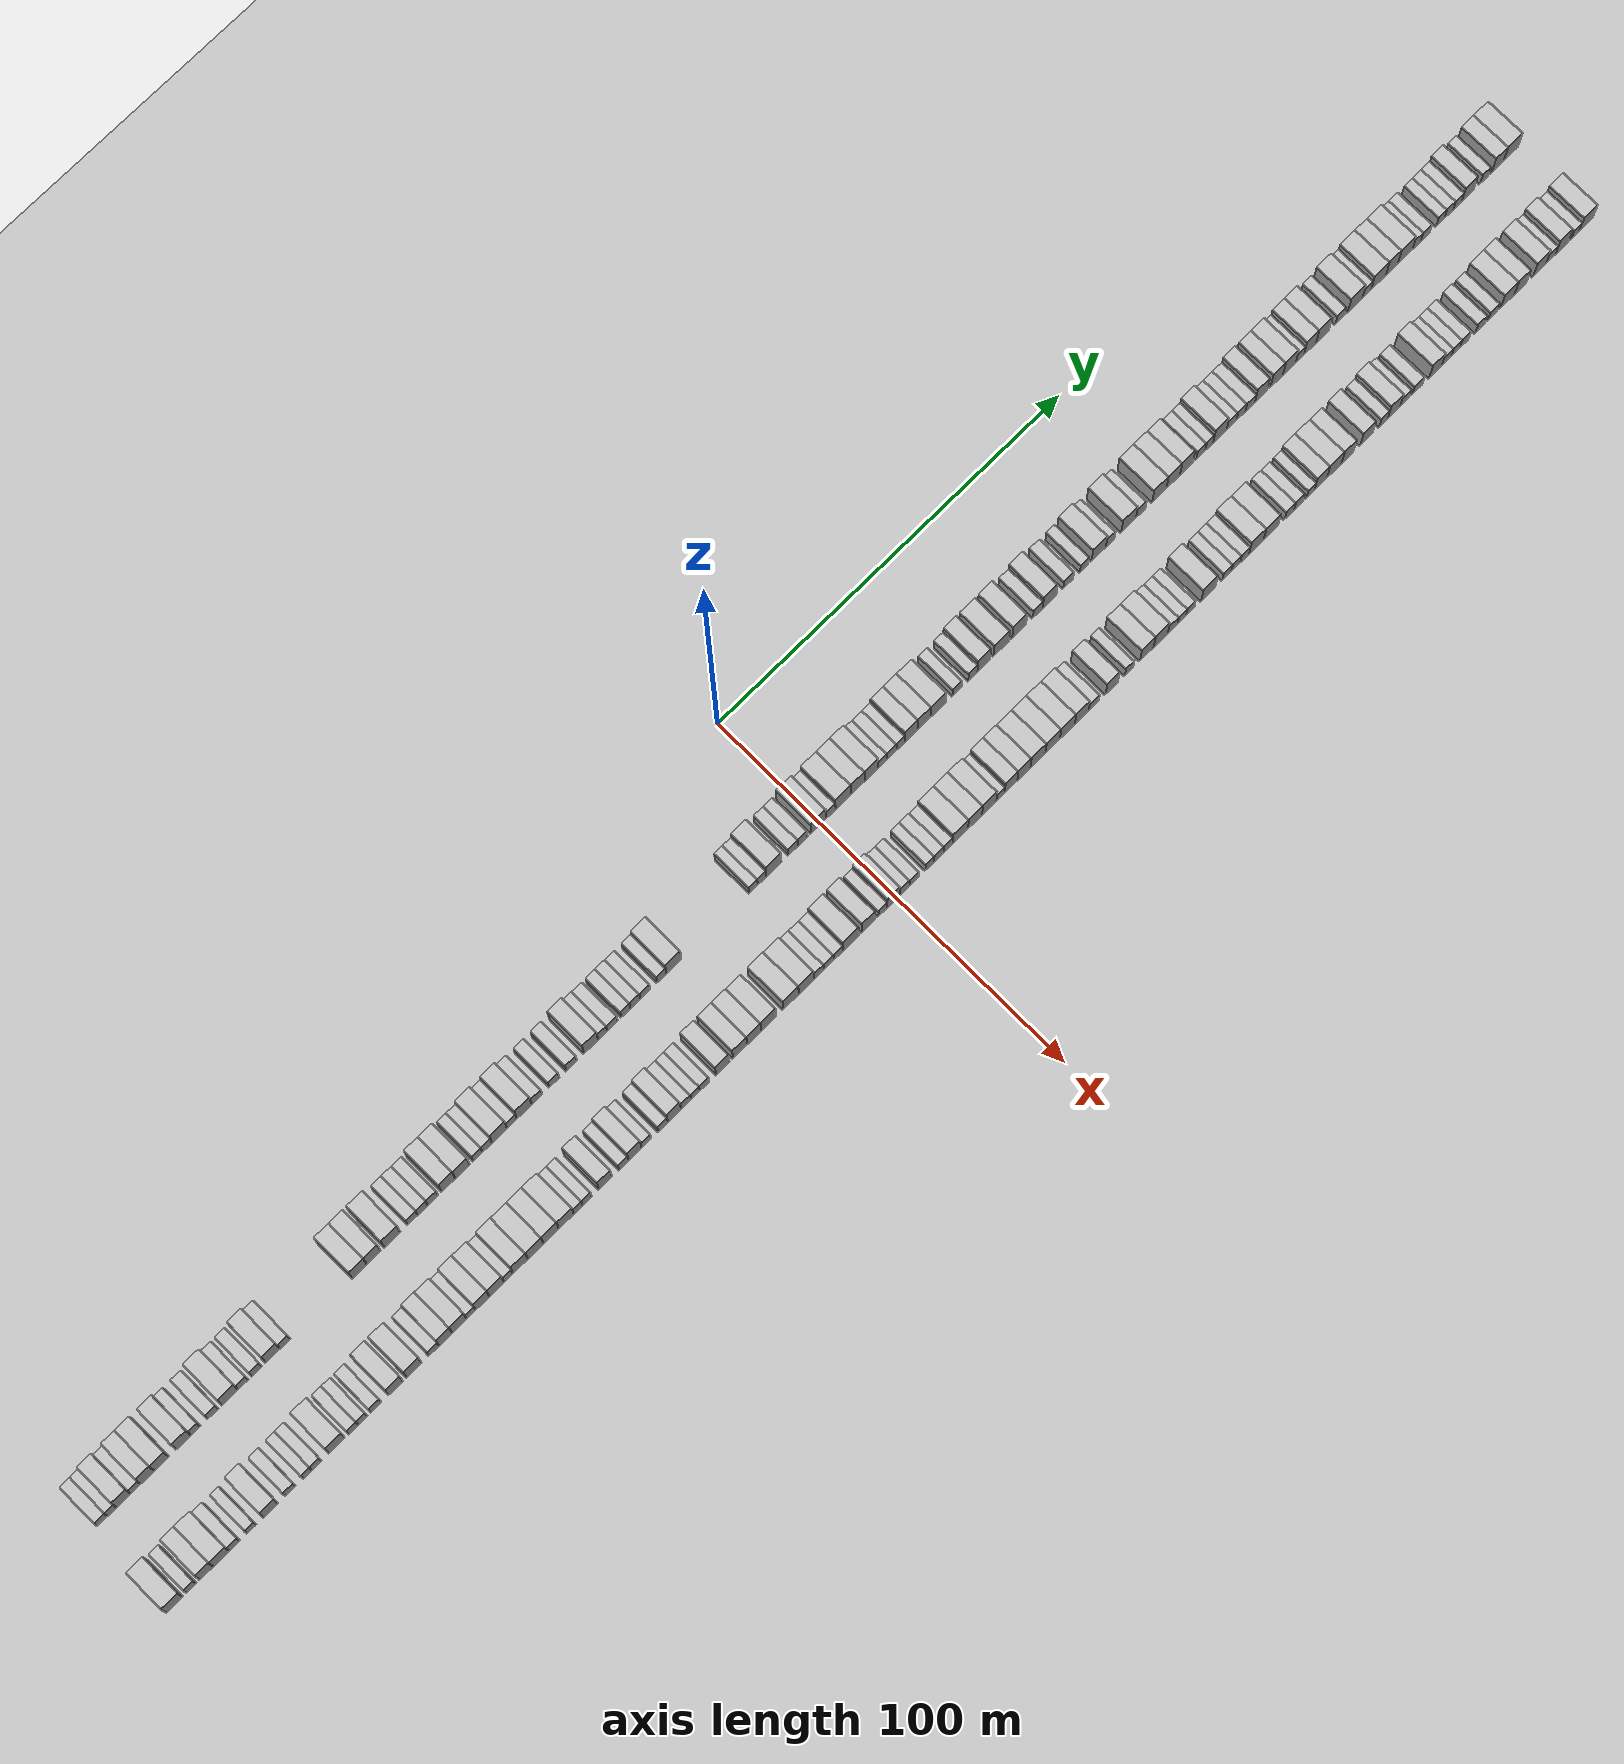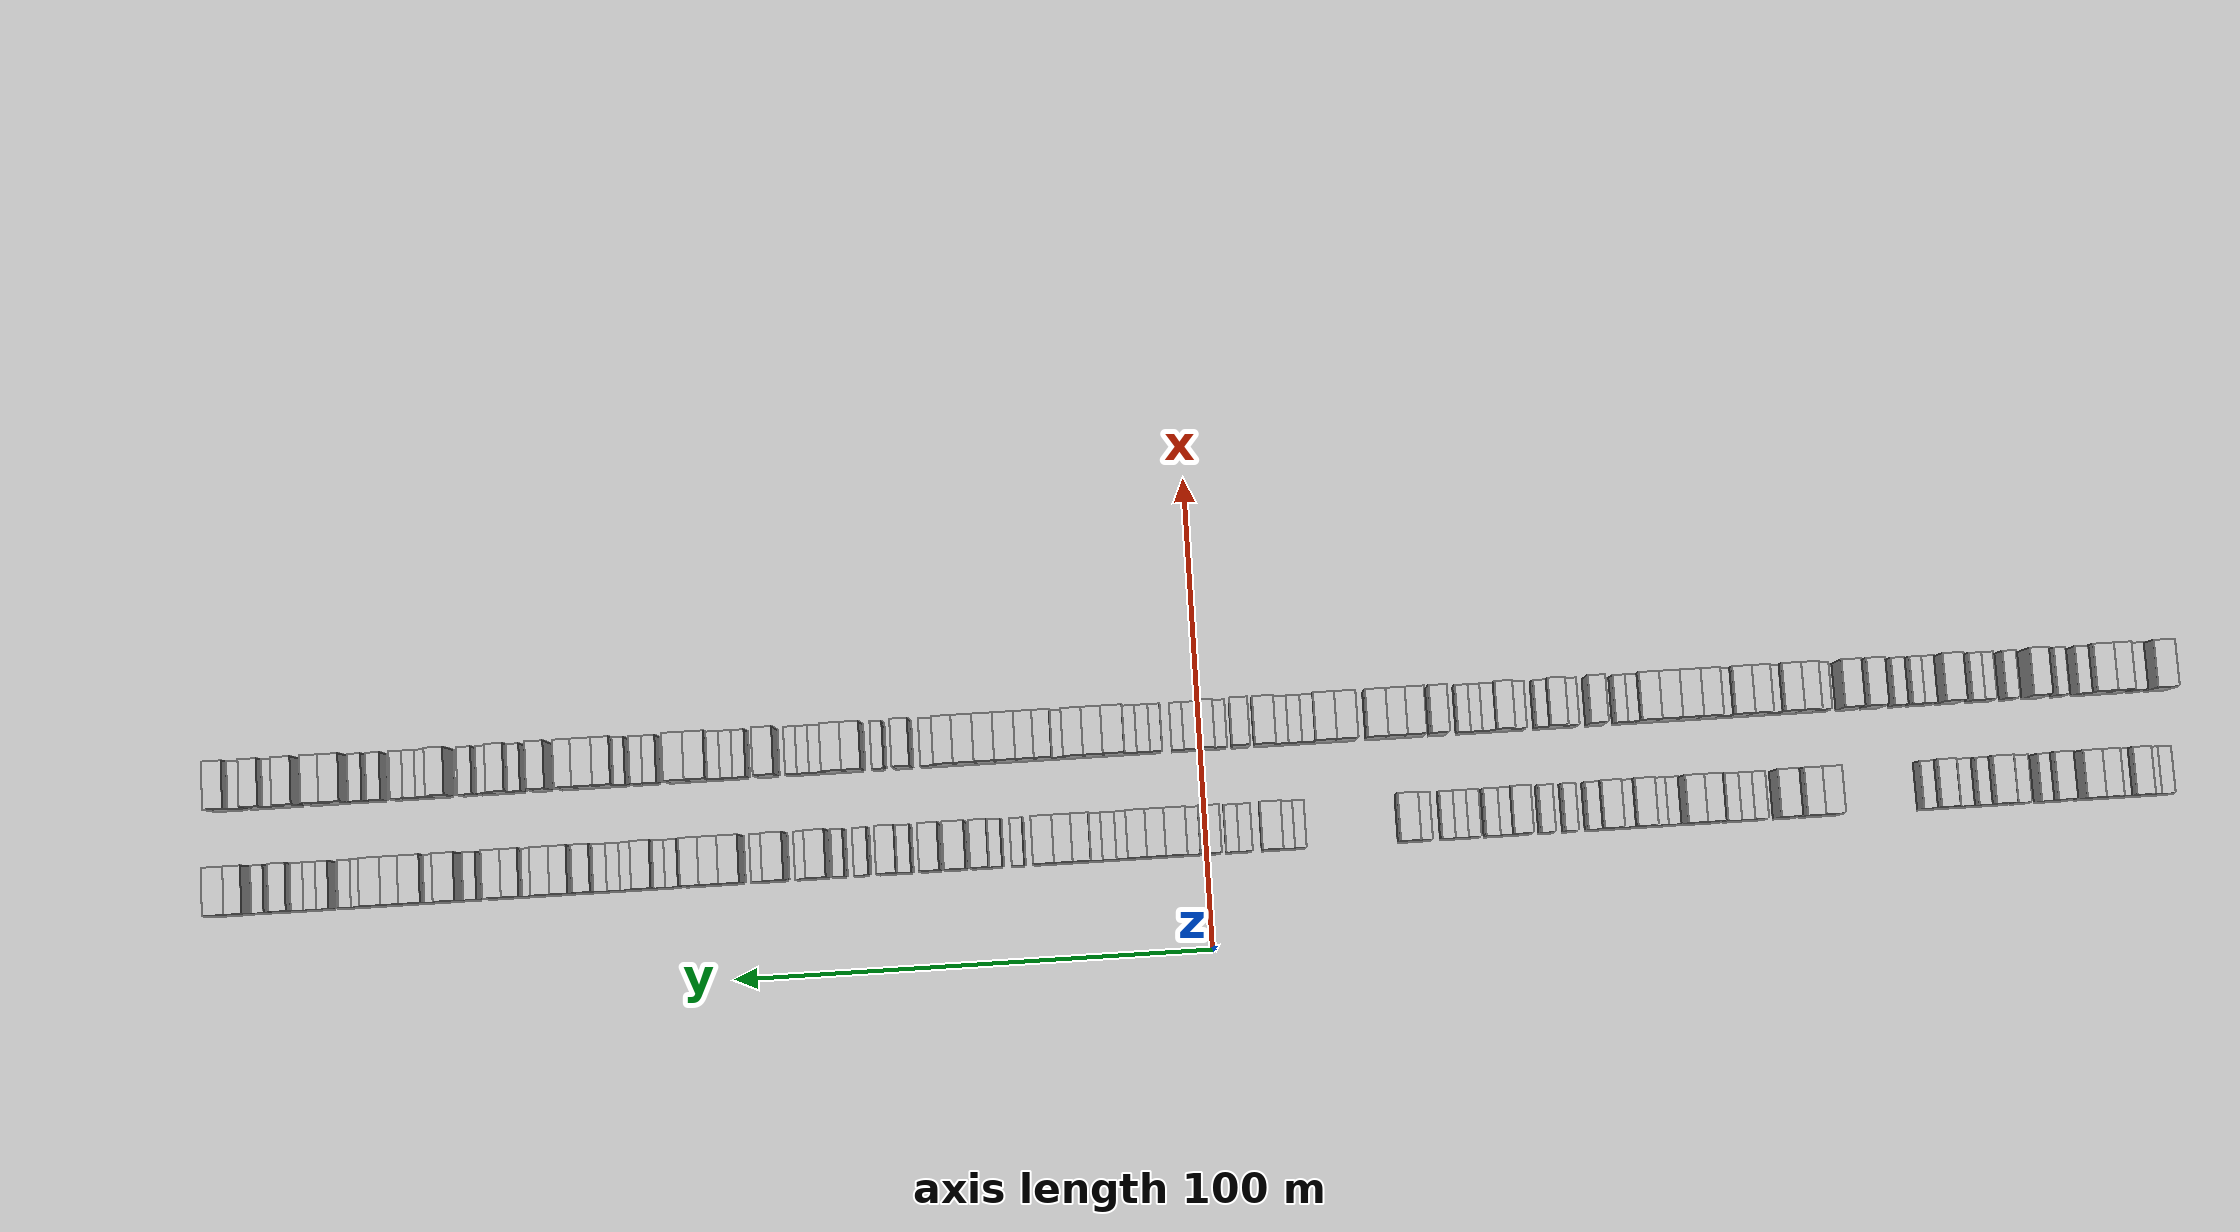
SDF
<?xml version="1.0" encoding="utf-8"?>

<sdf version="1.6">

   <world name="default">

      <gui fullscreen="0">

         <camera name="user_camera">

            <pose>-15 0 4.57585 0 0 0</pose>

            <view_controller>orbit</view_controller>

         </camera>

      </gui>

      <scene>

         <sky>

           <clouds>

             <speed>12</speed>

           </clouds>

         </sky>

         <ambient>0.4 0.4 0.4 1</ambient>

         <background>0.7 0.7 0.7 1</background>

         <shadows>1</shadows>

      </scene>

      <gravity>0 0 -9.8066</gravity>

      <magnetic_field>6e-06 2.3e-05 -4.2e-05</magnetic_field>

      <physics default="0" name="default_physics" type="ode">

         <ode>

            <solver>

               <type>quick</type>

               <iters>10</iters>

               <sor>1.0</sor>

               <use_dynamic_moi_rescaling>0</use_dynamic_moi_rescaling>

            </solver>

            <constraints>

               <cfm>0</cfm>

               <erp>0.2</erp>

               <contact_max_correcting_vel>100</contact_max_correcting_vel>

               <contact_surface_layer>0.001</contact_surface_layer>

            </constraints>

         </ode>

         <max_step_size>0.004</max_step_size>

         <real_time_factor>1</real_time_factor>

         <real_time_update_rate>250</real_time_update_rate>

      </physics>

      <light name="sun" type="directional">

         <cast_shadows>1</cast_shadows>

         <pose>0 0 10 0 0 0</pose>

         <diffuse>0.8 0.8 0.8 1</diffuse>

         <specular>0.2 0.2 0.2 1</specular>

         <attenuation>

            <range>1000</range>

            <constant>0.9</constant>

            <linear>0.01</linear>

            <quadratic>0.001</quadratic>

         </attenuation>

         <direction>-0.5 0.1 -0.9</direction>

      </light>

      <include>

         <name>ground_plane_1</name>

         <uri>model://HANNAS_ground_plane</uri>

         <pose>0 0 0  0 0 0</pose>

      </include>

      <include>

         <name>ground_plane_2</name>

         <uri>model://HANNAS_ground_plane</uri>

         <pose>100 0 0  0 0 0</pose>

      </include>

      <model name="building_1">

         <static>1</static>

         <pose frame="">25.0000 -200.5957 0 0.000000 0.000000 0.000000</pose>

         <link name="link">

            <pose frame="">0 0 3.00 0 0 0</pose>

            <collision name="collision">

               <geometry>

                  <box>

                     <size>10.0000 2.8085 6.0000</size>

                  </box>

               </geometry>

               <max_contacts>10</max_contacts>

               <surface>

                  <contact>

                     <ode/>

                  </contact>

                  <bounce/>

                  <friction>

                     <torsional>

                        <ode/>

                     </torsional>

                     <ode/>

                  </friction>

               </surface>

            </collision>

            <visual name="visual">

               <cast_shadows>0</cast_shadows>

               <geometry>

                  <box>

                     <size>10.0000 2.8085 6.0000</size>

                  </box>

               </geometry>

               <material>

                  <script>

                     <uri>model://HANNAS_wall/materials/scripts</uri>

                     <uri>model://HANNAS_wall/materials/textures</uri>

                     <name>vrc/HANNAS_wall</name>

                  </script>

               </material>

            </visual>

            <self_collide>0</self_collide>

            <enable_wind>0</enable_wind>

            <kinematic>0</kinematic>

         </link>

      </model>

      <model name="building_2">

         <static>1</static>

         <pose frame="">25.0000 -197.9848 0 0.000000 0.000000 0.000000</pose>

         <link name="link">

            <pose frame="">0 0 3.00 0 0 0</pose>

            <collision name="collision">

               <geometry>

                  <box>

                     <size>10.0000 2.4134 6.0000</size>

                  </box>

               </geometry>

               <max_contacts>10</max_contacts>

               <surface>

                  <contact>

                     <ode/>

                  </contact>

                  <bounce/>

                  <friction>

                     <torsional>

                        <ode/>

                     </torsional>

                     <ode/>

                  </friction>

               </surface>

            </collision>

            <visual name="visual">

               <cast_shadows>0</cast_shadows>

               <geometry>

                  <box>

                     <size>10.0000 2.4134 6.0000</size>

                  </box>

               </geometry>

               <material>

                  <script>

                     <uri>model://HANNAS_wall/materials/scripts</uri>

                     <uri>model://HANNAS_wall/materials/textures</uri>

                     <name>vrc/HANNAS_wall</name>

                  </script>

               </material>

            </visual>

            <self_collide>0</self_collide>

            <enable_wind>0</enable_wind>

            <kinematic>0</kinematic>

         </link>

      </model>

      <model name="building_3">

         <static>1</static>

         <pose frame="">25.0000 -194.8523 0 0.000000 0.000000 0.000000</pose>

         <link name="link">

            <pose frame="">0 0 4.50 0 0 0</pose>

            <collision name="collision">

               <geometry>

                  <box>

                     <size>10.0000 3.8517 9.0000</size>

                  </box>

               </geometry>

               <max_contacts>10</max_contacts>

               <surface>

                  <contact>

                     <ode/>

                  </contact>

                  <bounce/>

                  <friction>

                     <torsional>

                        <ode/>

                     </torsional>

                     <ode/>

                  </friction>

               </surface>

            </collision>

            <visual name="visual">

               <cast_shadows>0</cast_shadows>

               <geometry>

                  <box>

                     <size>10.0000 3.8517 9.0000</size>

                  </box>

               </geometry>

               <material>

                  <script>

                     <uri>model://HANNAS_wall/materials/scripts</uri>

                     <uri>model://HANNAS_wall/materials/textures</uri>

                     <name>vrc/HANNAS_wall</name>

                  </script>

               </material>

            </visual>

            <self_collide>0</self_collide>

            <enable_wind>0</enable_wind>

            <kinematic>0</kinematic>

         </link>

      </model>

      <model name="building_4">

         <static>1</static>

         <pose frame="">25.0000 -191.6137 0 0.000000 0.000000 0.000000</pose>

         <link name="link">

            <pose frame="">0 0 3.00 0 0 0</pose>

            <collision name="collision">

               <geometry>

                  <box>

                     <size>10.0000 2.6255 6.0000</size>

                  </box>

               </geometry>

               <max_contacts>10</max_contacts>

               <surface>

                  <contact>

                     <ode/>

                  </contact>

                  <bounce/>

                  <friction>

                     <torsional>

                        <ode/>

                     </torsional>

                     <ode/>

                  </friction>

               </surface>

            </collision>

            <visual name="visual">

               <cast_shadows>0</cast_shadows>

               <geometry>

                  <box>

                     <size>10.0000 2.6255 6.0000</size>

                  </box>

               </geometry>

               <material>

                  <script>

                     <uri>model://HANNAS_wall/materials/scripts</uri>

                     <uri>model://HANNAS_wall/materials/textures</uri>

                     <name>vrc/HANNAS_wall</name>

                  </script>

               </material>

            </visual>

            <self_collide>0</self_collide>

            <enable_wind>0</enable_wind>

            <kinematic>0</kinematic>

         </link>

      </model>

      <model name="building_5">

         <static>1</static>

         <pose frame="">25.0000 -188.4409 0 0.000000 0.000000 0.000000</pose>

         <link name="link">

            <pose frame="">0 0 4.50 0 0 0</pose>

            <collision name="collision">

               <geometry>

                  <box>

                     <size>10.0000 3.7200 9.0000</size>

                  </box>

               </geometry>

               <max_contacts>10</max_contacts>

               <surface>

                  <contact>

                     <ode/>

                  </contact>

                  <bounce/>

                  <friction>

                     <torsional>

                        <ode/>

                     </torsional>

                     <ode/>

                  </friction>

               </surface>

            </collision>

            <visual name="visual">

               <cast_shadows>0</cast_shadows>

               <geometry>

                  <box>

                     <size>10.0000 3.7200 9.0000</size>

                  </box>

               </geometry>

               <material>

                  <script>

                     <uri>model://HANNAS_wall/materials/scripts</uri>

                     <uri>model://HANNAS_wall/materials/textures</uri>

                     <name>vrc/HANNAS_wall</name>

                  </script>

               </material>

            </visual>

            <self_collide>0</self_collide>

            <enable_wind>0</enable_wind>

            <kinematic>0</kinematic>

         </link>

      </model>

      <model name="building_6">

         <static>1</static>

         <pose frame="">25.0000 -184.5921 0 0.000000 0.000000 0.000000</pose>

         <link name="link">

            <pose frame="">0 0 4.50 0 0 0</pose>

            <collision name="collision">

               <geometry>

                  <box>

                     <size>10.0000 3.9776 9.0000</size>

                  </box>

               </geometry>

               <max_contacts>10</max_contacts>

               <surface>

                  <contact>

                     <ode/>

                  </contact>

                  <bounce/>

                  <friction>

                     <torsional>

                        <ode/>

                     </torsional>

                     <ode/>

                  </friction>

               </surface>

            </collision>

            <visual name="visual">

               <cast_shadows>0</cast_shadows>

               <geometry>

                  <box>

                     <size>10.0000 3.9776 9.0000</size>

                  </box>

               </geometry>

               <material>

                  <script>

                     <uri>model://HANNAS_wall/materials/scripts</uri>

                     <uri>model://HANNAS_wall/materials/textures</uri>

                     <name>vrc/HANNAS_wall</name>

                  </script>

               </material>

            </visual>

            <self_collide>0</self_collide>

            <enable_wind>0</enable_wind>

            <kinematic>0</kinematic>

         </link>

      </model>

      <model name="building_7">

         <static>1</static>

         <pose frame="">25.0000 -178.6157 0 0.000000 0.000000 0.000000</pose>

         <link name="link">

            <pose frame="">0 0 4.50 0 0 0</pose>

            <collision name="collision">

               <geometry>

                  <box>

                     <size>10.0000 3.9752 9.0000</size>

                  </box>

               </geometry>

               <max_contacts>10</max_contacts>

               <surface>

                  <contact>

                     <ode/>

                  </contact>

                  <bounce/>

                  <friction>

                     <torsional>

                        <ode/>

                     </torsional>

                     <ode/>

                  </friction>

               </surface>

            </collision>

            <visual name="visual">

               <cast_shadows>0</cast_shadows>

               <geometry>

                  <box>

                     <size>10.0000 3.9752 9.0000</size>

                  </box>

               </geometry>

               <material>

                  <script>

                     <uri>model://HANNAS_wall/materials/scripts</uri>

                     <uri>model://HANNAS_wall/materials/textures</uri>

                     <name>vrc/HANNAS_wall</name>

                  </script>

               </material>

            </visual>

            <self_collide>0</self_collide>

            <enable_wind>0</enable_wind>

            <kinematic>0</kinematic>

         </link>

      </model>

      <model name="building_8">

         <static>1</static>

         <pose frame="">25.0000 -175.3538 0 0.000000 0.000000 0.000000</pose>

         <link name="link">

            <pose frame="">0 0 3.00 0 0 0</pose>

            <collision name="collision">

               <geometry>

                  <box>

                     <size>10.0000 2.5488 6.0000</size>

                  </box>

               </geometry>

               <max_contacts>10</max_contacts>

               <surface>

                  <contact>

                     <ode/>

                  </contact>

                  <bounce/>

                  <friction>

                     <torsional>

                        <ode/>

                     </torsional>

                     <ode/>

                  </friction>

               </surface>

            </collision>

            <visual name="visual">

               <cast_shadows>0</cast_shadows>

               <geometry>

                  <box>

                     <size>10.0000 2.5488 6.0000</size>

                  </box>

               </geometry>

               <material>

                  <script>

                     <uri>model://HANNAS_wall/materials/scripts</uri>

                     <uri>model://HANNAS_wall/materials/textures</uri>

                     <name>vrc/HANNAS_wall</name>

                  </script>

               </material>

            </visual>

            <self_collide>0</self_collide>

            <enable_wind>0</enable_wind>

            <kinematic>0</kinematic>

         </link>

      </model>

      <model name="building_9">

         <static>1</static>

         <pose frame="">25.0000 -170.6239 0 0.000000 0.000000 0.000000</pose>

         <link name="link">

            <pose frame="">0 0 3.00 0 0 0</pose>

            <collision name="collision">

               <geometry>

                  <box>

                     <size>10.0000 2.9109 6.0000</size>

                  </box>

               </geometry>

               <max_contacts>10</max_contacts>

               <surface>

                  <contact>

                     <ode/>

                  </contact>

                  <bounce/>

                  <friction>

                     <torsional>

                        <ode/>

                     </torsional>

                     <ode/>

                  </friction>

               </surface>

            </collision>

            <visual name="visual">

               <cast_shadows>0</cast_shadows>

               <geometry>

                  <box>

                     <size>10.0000 2.9109 6.0000</size>

                  </box>

               </geometry>

               <material>

                  <script>

                     <uri>model://HANNAS_wall/materials/scripts</uri>

                     <uri>model://HANNAS_wall/materials/textures</uri>

                     <name>vrc/HANNAS_wall</name>

                  </script>

               </material>

            </visual>

            <self_collide>0</self_collide>

            <enable_wind>0</enable_wind>

            <kinematic>0</kinematic>

         </link>

      </model>

      <model name="building_10">

         <static>1</static>

         <pose frame="">25.0000 -165.9567 0 0.000000 0.000000 0.000000</pose>

         <link name="link">

            <pose frame="">0 0 4.50 0 0 0</pose>

            <collision name="collision">

               <geometry>

                  <box>

                     <size>10.0000 4.4236 9.0000</size>

                  </box>

               </geometry>

               <max_contacts>10</max_contacts>

               <surface>

                  <contact>

                     <ode/>

                  </contact>

                  <bounce/>

                  <friction>

                     <torsional>

                        <ode/>

                     </torsional>

                     <ode/>

                  </friction>

               </surface>

            </collision>

            <visual name="visual">

               <cast_shadows>0</cast_shadows>

               <geometry>

                  <box>

                     <size>10.0000 4.4236 9.0000</size>

                  </box>

               </geometry>

               <material>

                  <script>

                     <uri>model://HANNAS_wall/materials/scripts</uri>

                     <uri>model://HANNAS_wall/materials/textures</uri>

                     <name>vrc/HANNAS_wall</name>

                  </script>

               </material>

            </visual>

            <self_collide>0</self_collide>

            <enable_wind>0</enable_wind>

            <kinematic>0</kinematic>

         </link>

      </model>

      <model name="building_11">

         <static>1</static>

         <pose frame="">25.0000 -162.3852 0 0.000000 0.000000 0.000000</pose>

         <link name="link">

            <pose frame="">0 0 3.00 0 0 0</pose>

            <collision name="collision">

               <geometry>

                  <box>

                     <size>10.0000 2.7193 6.0000</size>

                  </box>

               </geometry>

               <max_contacts>10</max_contacts>

               <surface>

                  <contact>

                     <ode/>

                  </contact>

                  <bounce/>

                  <friction>

                     <torsional>

                        <ode/>

                     </torsional>

                     <ode/>

                  </friction>

               </surface>

            </collision>

            <visual name="visual">

               <cast_shadows>0</cast_shadows>

               <geometry>

                  <box>

                     <size>10.0000 2.7193 6.0000</size>

                  </box>

               </geometry>

               <material>

                  <script>

                     <uri>model://HANNAS_wall/materials/scripts</uri>

                     <uri>model://HANNAS_wall/materials/textures</uri>

                     <name>vrc/HANNAS_wall</name>

                  </script>

               </material>

            </visual>

            <self_collide>0</self_collide>

            <enable_wind>0</enable_wind>

            <kinematic>0</kinematic>

         </link>

      </model>

      <model name="building_12">

         <static>1</static>

         <pose frame="">25.0000 -158.6169 0 0.000000 0.000000 0.000000</pose>

         <link name="link">

            <pose frame="">0 0 3.00 0 0 0</pose>

            <collision name="collision">

               <geometry>

                  <box>

                     <size>10.0000 2.8173 6.0000</size>

                  </box>

               </geometry>

               <max_contacts>10</max_contacts>

               <surface>

                  <contact>

                     <ode/>

                  </contact>

                  <bounce/>

                  <friction>

                     <torsional>

                        <ode/>

                     </torsional>

                     <ode/>

                  </friction>

               </surface>

            </collision>

            <visual name="visual">

               <cast_shadows>0</cast_shadows>

               <geometry>

                  <box>

                     <size>10.0000 2.8173 6.0000</size>

                  </box>

               </geometry>

               <material>

                  <script>

                     <uri>model://HANNAS_wall/materials/scripts</uri>

                     <uri>model://HANNAS_wall/materials/textures</uri>

                     <name>vrc/HANNAS_wall</name>

                  </script>

               </material>

            </visual>

            <self_collide>0</self_collide>

            <enable_wind>0</enable_wind>

            <kinematic>0</kinematic>

         </link>

      </model>

      <model name="building_13">

         <static>1</static>

         <pose frame="">25.0000 -154.2598 0 0.000000 0.000000 0.000000</pose>

         <link name="link">

            <pose frame="">0 0 4.50 0 0 0</pose>

            <collision name="collision">

               <geometry>

                  <box>

                     <size>10.0000 3.8968 9.0000</size>

                  </box>

               </geometry>

               <max_contacts>10</max_contacts>

               <surface>

                  <contact>

                     <ode/>

                  </contact>

                  <bounce/>

                  <friction>

                     <torsional>

                        <ode/>

                     </torsional>

                     <ode/>

                  </friction>

               </surface>

            </collision>

            <visual name="visual">

               <cast_shadows>0</cast_shadows>

               <geometry>

                  <box>

                     <size>10.0000 3.8968 9.0000</size>

                  </box>

               </geometry>

               <material>

                  <script>

                     <uri>model://HANNAS_wall/materials/scripts</uri>

                     <uri>model://HANNAS_wall/materials/textures</uri>

                     <name>vrc/HANNAS_wall</name>

                  </script>

               </material>

            </visual>

            <self_collide>0</self_collide>

            <enable_wind>0</enable_wind>

            <kinematic>0</kinematic>

         </link>

      </model>

      <model name="building_14">

         <static>1</static>

         <pose frame="">25.0000 -150.8935 0 0.000000 0.000000 0.000000</pose>

         <link name="link">

            <pose frame="">0 0 3.00 0 0 0</pose>

            <collision name="collision">

               <geometry>

                  <box>

                     <size>10.0000 2.8358 6.0000</size>

                  </box>

               </geometry>

               <max_contacts>10</max_contacts>

               <surface>

                  <contact>

                     <ode/>

                  </contact>

                  <bounce/>

                  <friction>

                     <torsional>

                        <ode/>

                     </torsional>

                     <ode/>

                  </friction>

               </surface>

            </collision>

            <visual name="visual">

               <cast_shadows>0</cast_shadows>

               <geometry>

                  <box>

                     <size>10.0000 2.8358 6.0000</size>

                  </box>

               </geometry>

               <material>

                  <script>

                     <uri>model://HANNAS_wall/materials/scripts</uri>

                     <uri>model://HANNAS_wall/materials/textures</uri>

                     <name>vrc/HANNAS_wall</name>

                  </script>

               </material>

            </visual>

            <self_collide>0</self_collide>

            <enable_wind>0</enable_wind>

            <kinematic>0</kinematic>

         </link>

      </model>

      <model name="building_15">

         <static>1</static>

         <pose frame="">25.0000 -130.3425 0 0.000000 0.000000 0.000000</pose>

         <link name="link">

            <pose frame="">0 0 4.50 0 0 0</pose>

            <collision name="collision">

               <geometry>

                  <box>

                     <size>10.0000 4.0888 9.0000</size>

                  </box>

               </geometry>

               <max_contacts>10</max_contacts>

               <surface>

                  <contact>

                     <ode/>

                  </contact>

                  <bounce/>

                  <friction>

                     <torsional>

                        <ode/>

                     </torsional>

                     <ode/>

                  </friction>

               </surface>

            </collision>

            <visual name="visual">

               <cast_shadows>0</cast_shadows>

               <geometry>

                  <box>

                     <size>10.0000 4.0888 9.0000</size>

                  </box>

               </geometry>

               <material>

                  <script>

                     <uri>model://HANNAS_wall/materials/scripts</uri>

                     <uri>model://HANNAS_wall/materials/textures</uri>

                     <name>vrc/HANNAS_wall</name>

                  </script>

               </material>

            </visual>

            <self_collide>0</self_collide>

            <enable_wind>0</enable_wind>

            <kinematic>0</kinematic>

         </link>

      </model>

      <model name="building_16">

         <static>1</static>

         <pose frame="">25.0000 -126.3942 0 0.000000 0.000000 0.000000</pose>

         <link name="link">

            <pose frame="">0 0 4.50 0 0 0</pose>

            <collision name="collision">

               <geometry>

                  <box>

                     <size>10.0000 3.8078 9.0000</size>

                  </box>

               </geometry>

               <max_contacts>10</max_contacts>

               <surface>

                  <contact>

                     <ode/>

                  </contact>

                  <bounce/>

                  <friction>

                     <torsional>

                        <ode/>

                     </torsional>

                     <ode/>

                  </friction>

               </surface>

            </collision>

            <visual name="visual">

               <cast_shadows>0</cast_shadows>

               <geometry>

                  <box>

                     <size>10.0000 3.8078 9.0000</size>

                  </box>

               </geometry>

               <material>

                  <script>

                     <uri>model://HANNAS_wall/materials/scripts</uri>

                     <uri>model://HANNAS_wall/materials/textures</uri>

                     <name>vrc/HANNAS_wall</name>

                  </script>

               </material>

            </visual>

            <self_collide>0</self_collide>

            <enable_wind>0</enable_wind>

            <kinematic>0</kinematic>

         </link>

      </model>

      <model name="building_17">

         <static>1</static>

         <pose frame="">25.0000 -121.2702 0 0.000000 0.000000 0.000000</pose>

         <link name="link">

            <pose frame="">0 0 4.50 0 0 0</pose>

            <collision name="collision">

               <geometry>

                  <box>

                     <size>10.0000 4.4401 9.0000</size>

                  </box>

               </geometry>

               <max_contacts>10</max_contacts>

               <surface>

                  <contact>

                     <ode/>

                  </contact>

                  <bounce/>

                  <friction>

                     <torsional>

                        <ode/>

                     </torsional>

                     <ode/>

                  </friction>

               </surface>

            </collision>

            <visual name="visual">

               <cast_shadows>0</cast_shadows>

               <geometry>

                  <box>

                     <size>10.0000 4.4401 9.0000</size>

                  </box>

               </geometry>

               <material>

                  <script>

                     <uri>model://HANNAS_wall/materials/scripts</uri>

                     <uri>model://HANNAS_wall/materials/textures</uri>

                     <name>vrc/HANNAS_wall</name>

                  </script>

               </material>

            </visual>

            <self_collide>0</self_collide>

            <enable_wind>0</enable_wind>

            <kinematic>0</kinematic>

         </link>

      </model>

      <model name="building_18">

         <static>1</static>

         <pose frame="">25.0000 -115.6292 0 0.000000 0.000000 0.000000</pose>

         <link name="link">

            <pose frame="">0 0 3.00 0 0 0</pose>

            <collision name="collision">

               <geometry>

                  <box>

                     <size>10.0000 2.8419 6.0000</size>

                  </box>

               </geometry>

               <max_contacts>10</max_contacts>

               <surface>

                  <contact>

                     <ode/>

                  </contact>

                  <bounce/>

                  <friction>

                     <torsional>

                        <ode/>

                     </torsional>

                     <ode/>

                  </friction>

               </surface>

            </collision>

            <visual name="visual">

               <cast_shadows>0</cast_shadows>

               <geometry>

                  <box>

                     <size>10.0000 2.8419 6.0000</size>

                  </box>

               </geometry>

               <material>

                  <script>

                     <uri>model://HANNAS_wall/materials/scripts</uri>

                     <uri>model://HANNAS_wall/materials/textures</uri>

                     <name>vrc/HANNAS_wall</name>

                  </script>

               </material>

            </visual>

            <self_collide>0</self_collide>

            <enable_wind>0</enable_wind>

            <kinematic>0</kinematic>

         </link>

      </model>

      <model name="building_19">

         <static>1</static>

         <pose frame="">25.0000 -112.8165 0 0.000000 0.000000 0.000000</pose>

         <link name="link">

            <pose frame="">0 0 3.00 0 0 0</pose>

            <collision name="collision">

               <geometry>

                  <box>

                     <size>10.0000 2.7835 6.0000</size>

                  </box>

               </geometry>

               <max_contacts>10</max_contacts>

               <surface>

                  <contact>

                     <ode/>

                  </contact>

                  <bounce/>

                  <friction>

                     <torsional>

                        <ode/>

                     </torsional>

                     <ode/>

                  </friction>

               </surface>

            </collision>

            <visual name="visual">

               <cast_shadows>0</cast_shadows>

               <geometry>

                  <box>

                     <size>10.0000 2.7835 6.0000</size>

                  </box>

               </geometry>

               <material>

                  <script>

                     <uri>model://HANNAS_wall/materials/scripts</uri>

                     <uri>model://HANNAS_wall/materials/textures</uri>

                     <name>vrc/HANNAS_wall</name>

                  </script>

               </material>

            </visual>

            <self_collide>0</self_collide>

            <enable_wind>0</enable_wind>

            <kinematic>0</kinematic>

         </link>

      </model>

      <model name="building_20">

         <static>1</static>

         <pose frame="">25.0000 -110.0008 0 0.000000 0.000000 0.000000</pose>

         <link name="link">

            <pose frame="">0 0 3.00 0 0 0</pose>

            <collision name="collision">

               <geometry>

                  <box>

                     <size>10.0000 2.8480 6.0000</size>

                  </box>

               </geometry>

               <max_contacts>10</max_contacts>

               <surface>

                  <contact>

                     <ode/>

                  </contact>

                  <bounce/>

                  <friction>

                     <torsional>

                        <ode/>

                     </torsional>

                     <ode/>

                  </friction>

               </surface>

            </collision>

            <visual name="visual">

               <cast_shadows>0</cast_shadows>

               <geometry>

                  <box>

                     <size>10.0000 2.8480 6.0000</size>

                  </box>

               </geometry>

               <material>

                  <script>

                     <uri>model://HANNAS_wall/materials/scripts</uri>

                     <uri>model://HANNAS_wall/materials/textures</uri>

                     <name>vrc/HANNAS_wall</name>

                  </script>

               </material>

            </visual>

            <self_collide>0</self_collide>

            <enable_wind>0</enable_wind>

            <kinematic>0</kinematic>

         </link>

      </model>

      <model name="building_21">

         <static>1</static>

         <pose frame="">25.0000 -105.6616 0 0.000000 0.000000 0.000000</pose>

         <link name="link">

            <pose frame="">0 0 4.50 0 0 0</pose>

            <collision name="collision">

               <geometry>

                  <box>

                     <size>10.0000 3.8304 9.0000</size>

                  </box>

               </geometry>

               <max_contacts>10</max_contacts>

               <surface>

                  <contact>

                     <ode/>

                  </contact>

                  <bounce/>

                  <friction>

                     <torsional>

                        <ode/>

                     </torsional>

                     <ode/>

                  </friction>

               </surface>

            </collision>

            <visual name="visual">

               <cast_shadows>0</cast_shadows>

               <geometry>

                  <box>

                     <size>10.0000 3.8304 9.0000</size>

                  </box>

               </geometry>

               <material>

                  <script>

                     <uri>model://HANNAS_wall/materials/scripts</uri>

                     <uri>model://HANNAS_wall/materials/textures</uri>

                     <name>vrc/HANNAS_wall</name>

                  </script>

               </material>

            </visual>

            <self_collide>0</self_collide>

            <enable_wind>0</enable_wind>

            <kinematic>0</kinematic>

         </link>

      </model>

      <model name="building_22">

         <static>1</static>

         <pose frame="">25.0000 -101.7530 0 0.000000 0.000000 0.000000</pose>

         <link name="link">

            <pose frame="">0 0 4.50 0 0 0</pose>

            <collision name="collision">

               <geometry>

                  <box>

                     <size>10.0000 3.9868 9.0000</size>

                  </box>

               </geometry>

               <max_contacts>10</max_contacts>

               <surface>

                  <contact>

                     <ode/>

                  </contact>

                  <bounce/>

                  <friction>

                     <torsional>

                        <ode/>

                     </torsional>

                     <ode/>

                  </friction>

               </surface>

            </collision>

            <visual name="visual">

               <cast_shadows>0</cast_shadows>

               <geometry>

                  <box>

                     <size>10.0000 3.9868 9.0000</size>

                  </box>

               </geometry>

               <material>

                  <script>

                     <uri>model://HANNAS_wall/materials/scripts</uri>

                     <uri>model://HANNAS_wall/materials/textures</uri>

                     <name>vrc/HANNAS_wall</name>

                  </script>

               </material>

            </visual>

            <self_collide>0</self_collide>

            <enable_wind>0</enable_wind>

            <kinematic>0</kinematic>

         </link>

      </model>

      <model name="building_23">

         <static>1</static>

         <pose frame="">25.0000 -97.4480 0 0.000000 0.000000 0.000000</pose>

         <link name="link">

            <pose frame="">0 0 3.00 0 0 0</pose>

            <collision name="collision">

               <geometry>

                  <box>

                     <size>10.0000 2.6234 6.0000</size>

                  </box>

               </geometry>

               <max_contacts>10</max_contacts>

               <surface>

                  <contact>

                     <ode/>

                  </contact>

                  <bounce/>

                  <friction>

                     <torsional>

                        <ode/>

                     </torsional>

                     <ode/>

                  </friction>

               </surface>

            </collision>

            <visual name="visual">

               <cast_shadows>0</cast_shadows>

               <geometry>

                  <box>

                     <size>10.0000 2.6234 6.0000</size>

                  </box>

               </geometry>

               <material>

                  <script>

                     <uri>model://HANNAS_wall/materials/scripts</uri>

                     <uri>model://HANNAS_wall/materials/textures</uri>

                     <name>vrc/HANNAS_wall</name>

                  </script>

               </material>

            </visual>

            <self_collide>0</self_collide>

            <enable_wind>0</enable_wind>

            <kinematic>0</kinematic>

         </link>

      </model>

      <model name="building_24">

         <static>1</static>

         <pose frame="">25.0000 -94.8192 0 0.000000 0.000000 0.000000</pose>

         <link name="link">

            <pose frame="">0 0 3.00 0 0 0</pose>

            <collision name="collision">

               <geometry>

                  <box>

                     <size>10.0000 2.6342 6.0000</size>

                  </box>

               </geometry>

               <max_contacts>10</max_contacts>

               <surface>

                  <contact>

                     <ode/>

                  </contact>

                  <bounce/>

                  <friction>

                     <torsional>

                        <ode/>

                     </torsional>

                     <ode/>

                  </friction>

               </surface>

            </collision>

            <visual name="visual">

               <cast_shadows>0</cast_shadows>

               <geometry>

                  <box>

                     <size>10.0000 2.6342 6.0000</size>

                  </box>

               </geometry>

               <material>

                  <script>

                     <uri>model://HANNAS_wall/materials/scripts</uri>

                     <uri>model://HANNAS_wall/materials/textures</uri>

                     <name>vrc/HANNAS_wall</name>

                  </script>

               </material>

            </visual>

            <self_collide>0</self_collide>

            <enable_wind>0</enable_wind>

            <kinematic>0</kinematic>

         </link>

      </model>

      <model name="building_25">

         <static>1</static>

         <pose frame="">25.0000 -91.3993 0 0.000000 0.000000 0.000000</pose>

         <link name="link">

            <pose frame="">0 0 4.50 0 0 0</pose>

            <collision name="collision">

               <geometry>

                  <box>

                     <size>10.0000 4.2055 9.0000</size>

                  </box>

               </geometry>

               <max_contacts>10</max_contacts>

               <surface>

                  <contact>

                     <ode/>

                  </contact>

                  <bounce/>

                  <friction>

                     <torsional>

                        <ode/>

                     </torsional>

                     <ode/>

                  </friction>

               </surface>

            </collision>

            <visual name="visual">

               <cast_shadows>0</cast_shadows>

               <geometry>

                  <box>

                     <size>10.0000 4.2055 9.0000</size>

                  </box>

               </geometry>

               <material>

                  <script>

                     <uri>model://HANNAS_wall/materials/scripts</uri>

                     <uri>model://HANNAS_wall/materials/textures</uri>

                     <name>vrc/HANNAS_wall</name>

                  </script>

               </material>

            </visual>

            <self_collide>0</self_collide>

            <enable_wind>0</enable_wind>

            <kinematic>0</kinematic>

         </link>

      </model>

      <model name="building_26">

         <static>1</static>

         <pose frame="">25.0000 -87.9068 0 0.000000 0.000000 0.000000</pose>

         <link name="link">

            <pose frame="">0 0 3.00 0 0 0</pose>

            <collision name="collision">

               <geometry>

                  <box>

                     <size>10.0000 2.7796 6.0000</size>

                  </box>

               </geometry>

               <max_contacts>10</max_contacts>

               <surface>

                  <contact>

                     <ode/>

                  </contact>

                  <bounce/>

                  <friction>

                     <torsional>

                        <ode/>

                     </torsional>

                     <ode/>

                  </friction>

               </surface>

            </collision>

            <visual name="visual">

               <cast_shadows>0</cast_shadows>

               <geometry>

                  <box>

                     <size>10.0000 2.7796 6.0000</size>

                  </box>

               </geometry>

               <material>

                  <script>

                     <uri>model://HANNAS_wall/materials/scripts</uri>

                     <uri>model://HANNAS_wall/materials/textures</uri>

                     <name>vrc/HANNAS_wall</name>

                  </script>

               </material>

            </visual>

            <self_collide>0</self_collide>

            <enable_wind>0</enable_wind>

            <kinematic>0</kinematic>

         </link>

      </model>

      <model name="building_27">

         <static>1</static>

         <pose frame="">25.0000 -84.4294 0 0.000000 0.000000 0.000000</pose>

         <link name="link">

            <pose frame="">0 0 4.50 0 0 0</pose>

            <collision name="collision">

               <geometry>

                  <box>

                     <size>10.0000 4.1752 9.0000</size>

                  </box>

               </geometry>

               <max_contacts>10</max_contacts>

               <surface>

                  <contact>

                     <ode/>

                  </contact>

                  <bounce/>

                  <friction>

                     <torsional>

                        <ode/>

                     </torsional>

                     <ode/>

                  </friction>

               </surface>

            </collision>

            <visual name="visual">

               <cast_shadows>0</cast_shadows>

               <geometry>

                  <box>

                     <size>10.0000 4.1752 9.0000</size>

                  </box>

               </geometry>

               <material>

                  <script>

                     <uri>model://HANNAS_wall/materials/scripts</uri>

                     <uri>model://HANNAS_wall/materials/textures</uri>

                     <name>vrc/HANNAS_wall</name>

                  </script>

               </material>

            </visual>

            <self_collide>0</self_collide>

            <enable_wind>0</enable_wind>

            <kinematic>0</kinematic>

         </link>

      </model>

      <model name="building_28">

         <static>1</static>

         <pose frame="">25.0000 -80.8772 0 0.000000 0.000000 0.000000</pose>

         <link name="link">

            <pose frame="">0 0 3.00 0 0 0</pose>

            <collision name="collision">

               <geometry>

                  <box>

                     <size>10.0000 2.9291 6.0000</size>

                  </box>

               </geometry>

               <max_contacts>10</max_contacts>

               <surface>

                  <contact>

                     <ode/>

                  </contact>

                  <bounce/>

                  <friction>

                     <torsional>

                        <ode/>

                     </torsional>

                     <ode/>

                  </friction>

               </surface>

            </collision>

            <visual name="visual">

               <cast_shadows>0</cast_shadows>

               <geometry>

                  <box>

                     <size>10.0000 2.9291 6.0000</size>

                  </box>

               </geometry>

               <material>

                  <script>

                     <uri>model://HANNAS_wall/materials/scripts</uri>

                     <uri>model://HANNAS_wall/materials/textures</uri>

                     <name>vrc/HANNAS_wall</name>

                  </script>

               </material>

            </visual>

            <self_collide>0</self_collide>

            <enable_wind>0</enable_wind>

            <kinematic>0</kinematic>

         </link>

      </model>

      <model name="building_29">

         <static>1</static>

         <pose frame="">25.0000 -76.0206 0 0.000000 0.000000 0.000000</pose>

         <link name="link">

            <pose frame="">0 0 3.00 0 0 0</pose>

            <collision name="collision">

               <geometry>

                  <box>

                     <size>10.0000 2.7842 6.0000</size>

                  </box>

               </geometry>

               <max_contacts>10</max_contacts>

               <surface>

                  <contact>

                     <ode/>

                  </contact>

                  <bounce/>

                  <friction>

                     <torsional>

                        <ode/>

                     </torsional>

                     <ode/>

                  </friction>

               </surface>

            </collision>

            <visual name="visual">

               <cast_shadows>0</cast_shadows>

               <geometry>

                  <box>

                     <size>10.0000 2.7842 6.0000</size>

                  </box>

               </geometry>

               <material>

                  <script>

                     <uri>model://HANNAS_wall/materials/scripts</uri>

                     <uri>model://HANNAS_wall/materials/textures</uri>

                     <name>vrc/HANNAS_wall</name>

                  </script>

               </material>

            </visual>

            <self_collide>0</self_collide>

            <enable_wind>0</enable_wind>

            <kinematic>0</kinematic>

         </link>

      </model>

      <model name="building_30">

         <static>1</static>

         <pose frame="">25.0000 -71.1401 0 0.000000 0.000000 0.000000</pose>

         <link name="link">

            <pose frame="">0 0 3.00 0 0 0</pose>

            <collision name="collision">

               <geometry>

                  <box>

                     <size>10.0000 2.9768 6.0000</size>

                  </box>

               </geometry>

               <max_contacts>10</max_contacts>

               <surface>

                  <contact>

                     <ode/>

                  </contact>

                  <bounce/>

                  <friction>

                     <torsional>

                        <ode/>

                     </torsional>

                     <ode/>

                  </friction>

               </surface>

            </collision>

            <visual name="visual">

               <cast_shadows>0</cast_shadows>

               <geometry>

                  <box>

                     <size>10.0000 2.9768 6.0000</size>

                  </box>

               </geometry>

               <material>

                  <script>

                     <uri>model://HANNAS_wall/materials/scripts</uri>

                     <uri>model://HANNAS_wall/materials/textures</uri>

                     <name>vrc/HANNAS_wall</name>

                  </script>

               </material>

            </visual>

            <self_collide>0</self_collide>

            <enable_wind>0</enable_wind>

            <kinematic>0</kinematic>

         </link>

      </model>

      <model name="building_31">

         <static>1</static>

         <pose frame="">25.0000 -65.6525 0 0.000000 0.000000 0.000000</pose>

         <link name="link">

            <pose frame="">0 0 4.50 0 0 0</pose>

            <collision name="collision">

               <geometry>

                  <box>

                     <size>10.0000 3.9983 9.0000</size>

                  </box>

               </geometry>

               <max_contacts>10</max_contacts>

               <surface>

                  <contact>

                     <ode/>

                  </contact>

                  <bounce/>

                  <friction>

                     <torsional>

                        <ode/>

                     </torsional>

                     <ode/>

                  </friction>

               </surface>

            </collision>

            <visual name="visual">

               <cast_shadows>0</cast_shadows>

               <geometry>

                  <box>

                     <size>10.0000 3.9983 9.0000</size>

                  </box>

               </geometry>

               <material>

                  <script>

                     <uri>model://HANNAS_wall/materials/scripts</uri>

                     <uri>model://HANNAS_wall/materials/textures</uri>

                     <name>vrc/HANNAS_wall</name>

                  </script>

               </material>

            </visual>

            <self_collide>0</self_collide>

            <enable_wind>0</enable_wind>

            <kinematic>0</kinematic>

         </link>

      </model>

      <model name="building_32">

         <static>1</static>

         <pose frame="">25.0000 -62.3743 0 0.000000 0.000000 0.000000</pose>

         <link name="link">

            <pose frame="">0 0 3.00 0 0 0</pose>

            <collision name="collision">

               <geometry>

                  <box>

                     <size>10.0000 2.5583 6.0000</size>

                  </box>

               </geometry>

               <max_contacts>10</max_contacts>

               <surface>

                  <contact>

                     <ode/>

                  </contact>

                  <bounce/>

                  <friction>

                     <torsional>

                        <ode/>

                     </torsional>

                     <ode/>

                  </friction>

               </surface>

            </collision>

            <visual name="visual">

               <cast_shadows>0</cast_shadows>

               <geometry>

                  <box>

                     <size>10.0000 2.5583 6.0000</size>

                  </box>

               </geometry>

               <material>

                  <script>

                     <uri>model://HANNAS_wall/materials/scripts</uri>

                     <uri>model://HANNAS_wall/materials/textures</uri>

                     <name>vrc/HANNAS_wall</name>

                  </script>

               </material>

            </visual>

            <self_collide>0</self_collide>

            <enable_wind>0</enable_wind>

            <kinematic>0</kinematic>

         </link>

      </model>

      <model name="building_33">

         <static>1</static>

         <pose frame="">25.0000 -59.6118 0 0.000000 0.000000 0.000000</pose>

         <link name="link">

            <pose frame="">0 0 3.00 0 0 0</pose>

            <collision name="collision">

               <geometry>

                  <box>

                     <size>10.0000 2.9667 6.0000</size>

                  </box>

               </geometry>

               <max_contacts>10</max_contacts>

               <surface>

                  <contact>

                     <ode/>

                  </contact>

                  <bounce/>

                  <friction>

                     <torsional>

                        <ode/>

                     </torsional>

                     <ode/>

                  </friction>

               </surface>

            </collision>

            <visual name="visual">

               <cast_shadows>0</cast_shadows>

               <geometry>

                  <box>

                     <size>10.0000 2.9667 6.0000</size>

                  </box>

               </geometry>

               <material>

                  <script>

                     <uri>model://HANNAS_wall/materials/scripts</uri>

                     <uri>model://HANNAS_wall/materials/textures</uri>

                     <name>vrc/HANNAS_wall</name>

                  </script>

               </material>

            </visual>

            <self_collide>0</self_collide>

            <enable_wind>0</enable_wind>

            <kinematic>0</kinematic>

         </link>

      </model>

      <model name="building_34">

         <static>1</static>

         <pose frame="">25.0000 -55.7953 0 0.000000 0.000000 0.000000</pose>

         <link name="link">

            <pose frame="">0 0 3.00 0 0 0</pose>

            <collision name="collision">

               <geometry>

                  <box>

                     <size>10.0000 2.6663 6.0000</size>

                  </box>

               </geometry>

               <max_contacts>10</max_contacts>

               <surface>

                  <contact>

                     <ode/>

                  </contact>

                  <bounce/>

                  <friction>

                     <torsional>

                        <ode/>

                     </torsional>

                     <ode/>

                  </friction>

               </surface>

            </collision>

            <visual name="visual">

               <cast_shadows>0</cast_shadows>

               <geometry>

                  <box>

                     <size>10.0000 2.6663 6.0000</size>

                  </box>

               </geometry>

               <material>

                  <script>

                     <uri>model://HANNAS_wall/materials/scripts</uri>

                     <uri>model://HANNAS_wall/materials/textures</uri>

                     <name>vrc/HANNAS_wall</name>

                  </script>

               </material>

            </visual>

            <self_collide>0</self_collide>

            <enable_wind>0</enable_wind>

            <kinematic>0</kinematic>

         </link>

      </model>

      <model name="building_35">

         <static>1</static>

         <pose frame="">25.0000 -53.0980 0 0.000000 0.000000 0.000000</pose>

         <link name="link">

            <pose frame="">0 0 3.00 0 0 0</pose>

            <collision name="collision">

               <geometry>

                  <box>

                     <size>10.0000 2.7282 6.0000</size>

                  </box>

               </geometry>

               <max_contacts>10</max_contacts>

               <surface>

                  <contact>

                     <ode/>

                  </contact>

                  <bounce/>

                  <friction>

                     <torsional>

                        <ode/>

                     </torsional>

                     <ode/>

                  </friction>

               </surface>

            </collision>

            <visual name="visual">

               <cast_shadows>0</cast_shadows>

               <geometry>

                  <box>

                     <size>10.0000 2.7282 6.0000</size>

                  </box>

               </geometry>

               <material>

                  <script>

                     <uri>model://HANNAS_wall/materials/scripts</uri>

                     <uri>model://HANNAS_wall/materials/textures</uri>

                     <name>vrc/HANNAS_wall</name>

                  </script>

               </material>

            </visual>

            <self_collide>0</self_collide>

            <enable_wind>0</enable_wind>

            <kinematic>0</kinematic>

         </link>

      </model>

      <model name="building_36">

         <static>1</static>

         <pose frame="">25.0000 -50.3425 0 0.000000 0.000000 0.000000</pose>

         <link name="link">

            <pose frame="">0 0 3.00 0 0 0</pose>

            <collision name="collision">

               <geometry>

                  <box>

                     <size>10.0000 2.7828 6.0000</size>

                  </box>

               </geometry>

               <max_contacts>10</max_contacts>

               <surface>

                  <contact>

                     <ode/>

                  </contact>

                  <bounce/>

                  <friction>

                     <torsional>

                        <ode/>

                     </torsional>

                     <ode/>

                  </friction>

               </surface>

            </collision>

            <visual name="visual">

               <cast_shadows>0</cast_shadows>

               <geometry>

                  <box>

                     <size>10.0000 2.7828 6.0000</size>

                  </box>

               </geometry>

               <material>

                  <script>

                     <uri>model://HANNAS_wall/materials/scripts</uri>

                     <uri>model://HANNAS_wall/materials/textures</uri>

                     <name>vrc/HANNAS_wall</name>

                  </script>

               </material>

            </visual>

            <self_collide>0</self_collide>

            <enable_wind>0</enable_wind>

            <kinematic>0</kinematic>

         </link>

      </model>

      <model name="building_37">

         <static>1</static>

         <pose frame="">25.0000 -45.6284 0 0.000000 0.000000 0.000000</pose>

         <link name="link">

            <pose frame="">0 0 3.00 0 0 0</pose>

            <collision name="collision">

               <geometry>

                  <box>

                     <size>10.0000 2.6455 6.0000</size>

                  </box>

               </geometry>

               <max_contacts>10</max_contacts>

               <surface>

                  <contact>

                     <ode/>

                  </contact>

                  <bounce/>

                  <friction>

                     <torsional>

                        <ode/>

                     </torsional>

                     <ode/>

                  </friction>

               </surface>

            </collision>

            <visual name="visual">

               <cast_shadows>0</cast_shadows>

               <geometry>

                  <box>

                     <size>10.0000 2.6455 6.0000</size>

                  </box>

               </geometry>

               <material>

                  <script>

                     <uri>model://HANNAS_wall/materials/scripts</uri>

                     <uri>model://HANNAS_wall/materials/textures</uri>

                     <name>vrc/HANNAS_wall</name>

                  </script>

               </material>

            </visual>

            <self_collide>0</self_collide>

            <enable_wind>0</enable_wind>

            <kinematic>0</kinematic>

         </link>

      </model>

      <model name="building_38">

         <static>1</static>

         <pose frame="">25.0000 -42.1798 0 0.000000 0.000000 0.000000</pose>

         <link name="link">

            <pose frame="">0 0 4.50 0 0 0</pose>

            <collision name="collision">

               <geometry>

                  <box>

                     <size>10.0000 4.2517 9.0000</size>

                  </box>

               </geometry>

               <max_contacts>10</max_contacts>

               <surface>

                  <contact>

                     <ode/>

                  </contact>

                  <bounce/>

                  <friction>

                     <torsional>

                        <ode/>

                     </torsional>

                     <ode/>

                  </friction>

               </surface>

            </collision>

            <visual name="visual">

               <cast_shadows>0</cast_shadows>

               <geometry>

                  <box>

                     <size>10.0000 4.2517 9.0000</size>

                  </box>

               </geometry>

               <material>

                  <script>

                     <uri>model://HANNAS_wall/materials/scripts</uri>

                     <uri>model://HANNAS_wall/materials/textures</uri>

                     <name>vrc/HANNAS_wall</name>

                  </script>

               </material>

            </visual>

            <self_collide>0</self_collide>

            <enable_wind>0</enable_wind>

            <kinematic>0</kinematic>

         </link>

      </model>

      <model name="building_39">

         <static>1</static>

         <pose frame="">25.0000 -19.4496 0 0.000000 0.000000 0.000000</pose>

         <link name="link">

            <pose frame="">0 0 3.00 0 0 0</pose>

            <collision name="collision">

               <geometry>

                  <box>

                     <size>10.0000 2.4029 6.0000</size>

                  </box>

               </geometry>

               <max_contacts>10</max_contacts>

               <surface>

                  <contact>

                     <ode/>

                  </contact>

                  <bounce/>

                  <friction>

                     <torsional>

                        <ode/>

                     </torsional>

                     <ode/>

                  </friction>

               </surface>

            </collision>

            <visual name="visual">

               <cast_shadows>0</cast_shadows>

               <geometry>

                  <box>

                     <size>10.0000 2.4029 6.0000</size>

                  </box>

               </geometry>

               <material>

                  <script>

                     <uri>model://HANNAS_wall/materials/scripts</uri>

                     <uri>model://HANNAS_wall/materials/textures</uri>

                     <name>vrc/HANNAS_wall</name>

                  </script>

               </material>

            </visual>

            <self_collide>0</self_collide>

            <enable_wind>0</enable_wind>

            <kinematic>0</kinematic>

         </link>

      </model>

      <model name="building_40">

         <static>1</static>

         <pose frame="">25.0000 -16.9956 0 0.000000 0.000000 0.000000</pose>

         <link name="link">

            <pose frame="">0 0 3.00 0 0 0</pose>

            <collision name="collision">

               <geometry>

                  <box>

                     <size>10.0000 2.5051 6.0000</size>

                  </box>

               </geometry>

               <max_contacts>10</max_contacts>

               <surface>

                  <contact>

                     <ode/>

                  </contact>

                  <bounce/>

                  <friction>

                     <torsional>

                        <ode/>

                     </torsional>

                     <ode/>

                  </friction>

               </surface>

            </collision>

            <visual name="visual">

               <cast_shadows>0</cast_shadows>

               <geometry>

                  <box>

                     <size>10.0000 2.5051 6.0000</size>

                  </box>

               </geometry>

               <material>

                  <script>

                     <uri>model://HANNAS_wall/materials/scripts</uri>

                     <uri>model://HANNAS_wall/materials/textures</uri>

                     <name>vrc/HANNAS_wall</name>

                  </script>

               </material>

            </visual>

            <self_collide>0</self_collide>

            <enable_wind>0</enable_wind>

            <kinematic>0</kinematic>

         </link>

      </model>

      <model name="building_41">

         <static>1</static>

         <pose frame="">25.0000 -13.5917 0 0.000000 0.000000 0.000000</pose>

         <link name="link">

            <pose frame="">0 0 4.50 0 0 0</pose>

            <collision name="collision">

               <geometry>

                  <box>

                     <size>10.0000 4.3028 9.0000</size>

                  </box>

               </geometry>

               <max_contacts>10</max_contacts>

               <surface>

                  <contact>

                     <ode/>

                  </contact>

                  <bounce/>

                  <friction>

                     <torsional>

                        <ode/>

                     </torsional>

                     <ode/>

                  </friction>

               </surface>

            </collision>

            <visual name="visual">

               <cast_shadows>0</cast_shadows>

               <geometry>

                  <box>

                     <size>10.0000 4.3028 9.0000</size>

                  </box>

               </geometry>

               <material>

                  <script>

                     <uri>model://HANNAS_wall/materials/scripts</uri>

                     <uri>model://HANNAS_wall/materials/textures</uri>

                     <name>vrc/HANNAS_wall</name>

                  </script>

               </material>

            </visual>

            <self_collide>0</self_collide>

            <enable_wind>0</enable_wind>

            <kinematic>0</kinematic>

         </link>

      </model>

      <model name="building_42">

         <static>1</static>

         <pose frame="">25.0000 -8.0424 0 0.000000 0.000000 0.000000</pose>

         <link name="link">

            <pose frame="">0 0 3.00 0 0 0</pose>

            <collision name="collision">

               <geometry>

                  <box>

                     <size>10.0000 2.7958 6.0000</size>

                  </box>

               </geometry>

               <max_contacts>10</max_contacts>

               <surface>

                  <contact>

                     <ode/>

                  </contact>

                  <bounce/>

                  <friction>

                     <torsional>

                        <ode/>

                     </torsional>

                     <ode/>

                  </friction>

               </surface>

            </collision>

            <visual name="visual">

               <cast_shadows>0</cast_shadows>

               <geometry>

                  <box>

                     <size>10.0000 2.7958 6.0000</size>

                  </box>

               </geometry>

               <material>

                  <script>

                     <uri>model://HANNAS_wall/materials/scripts</uri>

                     <uri>model://HANNAS_wall/materials/textures</uri>

                     <name>vrc/HANNAS_wall</name>

                  </script>

               </material>

            </visual>

            <self_collide>0</self_collide>

            <enable_wind>0</enable_wind>

            <kinematic>0</kinematic>

         </link>

      </model>

      <model name="building_43">

         <static>1</static>

         <pose frame="">25.0000 -5.2995 0 0.000000 0.000000 0.000000</pose>

         <link name="link">

            <pose frame="">0 0 3.00 0 0 0</pose>

            <collision name="collision">

               <geometry>

                  <box>

                     <size>10.0000 2.6900 6.0000</size>

                  </box>

               </geometry>

               <max_contacts>10</max_contacts>

               <surface>

                  <contact>

                     <ode/>

                  </contact>

                  <bounce/>

                  <friction>

                     <torsional>

                        <ode/>

                     </torsional>

                     <ode/>

                  </friction>

               </surface>

            </collision>

            <visual name="visual">

               <cast_shadows>0</cast_shadows>

               <geometry>

                  <box>

                     <size>10.0000 2.6900 6.0000</size>

                  </box>

               </geometry>

               <material>

                  <script>

                     <uri>model://HANNAS_wall/materials/scripts</uri>

                     <uri>model://HANNAS_wall/materials/textures</uri>

                     <name>vrc/HANNAS_wall</name>

                  </script>

               </material>

            </visual>

            <self_collide>0</self_collide>

            <enable_wind>0</enable_wind>

            <kinematic>0</kinematic>

         </link>

      </model>

      <model name="building_44">

         <static>1</static>

         <pose frame="">25.0000 -0.7623 0 0.000000 0.000000 0.000000</pose>

         <link name="link">

            <pose frame="">0 0 4.50 0 0 0</pose>

            <collision name="collision">

               <geometry>

                  <box>

                     <size>10.0000 4.3845 9.0000</size>

                  </box>

               </geometry>

               <max_contacts>10</max_contacts>

               <surface>

                  <contact>

                     <ode/>

                  </contact>

                  <bounce/>

                  <friction>

                     <torsional>

                        <ode/>

                     </torsional>

                     <ode/>

                  </friction>

               </surface>

            </collision>

            <visual name="visual">

               <cast_shadows>0</cast_shadows>

               <geometry>

                  <box>

                     <size>10.0000 4.3845 9.0000</size>

                  </box>

               </geometry>

               <material>

                  <script>

                     <uri>model://HANNAS_wall/materials/scripts</uri>

                     <uri>model://HANNAS_wall/materials/textures</uri>

                     <name>vrc/HANNAS_wall</name>

                  </script>

               </material>

            </visual>

            <self_collide>0</self_collide>

            <enable_wind>0</enable_wind>

            <kinematic>0</kinematic>

         </link>

      </model>

      <model name="building_45">

         <static>1</static>

         <pose frame="">25.0000 2.7781 0 0.000000 0.000000 0.000000</pose>

         <link name="link">

            <pose frame="">0 0 3.00 0 0 0</pose>

            <collision name="collision">

               <geometry>

                  <box>

                     <size>10.0000 2.6963 6.0000</size>

                  </box>

               </geometry>

               <max_contacts>10</max_contacts>

               <surface>

                  <contact>

                     <ode/>

                  </contact>

                  <bounce/>

                  <friction>

                     <torsional>

                        <ode/>

                     </torsional>

                     <ode/>

                  </friction>

               </surface>

            </collision>

            <visual name="visual">

               <cast_shadows>0</cast_shadows>

               <geometry>

                  <box>

                     <size>10.0000 2.6963 6.0000</size>

                  </box>

               </geometry>

               <material>

                  <script>

                     <uri>model://HANNAS_wall/materials/scripts</uri>

                     <uri>model://HANNAS_wall/materials/textures</uri>

                     <name>vrc/HANNAS_wall</name>

                  </script>

               </material>

            </visual>

            <self_collide>0</self_collide>

            <enable_wind>0</enable_wind>

            <kinematic>0</kinematic>

         </link>

      </model>

      <model name="building_46">

         <static>1</static>

         <pose frame="">25.0000 6.3581 0 0.000000 0.000000 0.000000</pose>

         <link name="link">

            <pose frame="">0 0 4.50 0 0 0</pose>

            <collision name="collision">

               <geometry>

                  <box>

                     <size>10.0000 4.4637 9.0000</size>

                  </box>

               </geometry>

               <max_contacts>10</max_contacts>

               <surface>

                  <contact>

                     <ode/>

                  </contact>

                  <bounce/>

                  <friction>

                     <torsional>

                        <ode/>

                     </torsional>

                     <ode/>

                  </friction>

               </surface>

            </collision>

            <visual name="visual">

               <cast_shadows>0</cast_shadows>

               <geometry>

                  <box>

                     <size>10.0000 4.4637 9.0000</size>

                  </box>

               </geometry>

               <material>

                  <script>

                     <uri>model://HANNAS_wall/materials/scripts</uri>

                     <uri>model://HANNAS_wall/materials/textures</uri>

                     <name>vrc/HANNAS_wall</name>

                  </script>

               </material>

            </visual>

            <self_collide>0</self_collide>

            <enable_wind>0</enable_wind>

            <kinematic>0</kinematic>

         </link>

      </model>

      <model name="building_47">

         <static>1</static>

         <pose frame="">25.0000 10.5509 0 0.000000 0.000000 0.000000</pose>

         <link name="link">

            <pose frame="">0 0 4.50 0 0 0</pose>

            <collision name="collision">

               <geometry>

                  <box>

                     <size>10.0000 3.9219 9.0000</size>

                  </box>

               </geometry>

               <max_contacts>10</max_contacts>

               <surface>

                  <contact>

                     <ode/>

                  </contact>

                  <bounce/>

                  <friction>

                     <torsional>

                        <ode/>

                     </torsional>

                     <ode/>

                  </friction>

               </surface>

            </collision>

            <visual name="visual">

               <cast_shadows>0</cast_shadows>

               <geometry>

                  <box>

                     <size>10.0000 3.9219 9.0000</size>

                  </box>

               </geometry>

               <material>

                  <script>

                     <uri>model://HANNAS_wall/materials/scripts</uri>

                     <uri>model://HANNAS_wall/materials/textures</uri>

                     <name>vrc/HANNAS_wall</name>

                  </script>

               </material>

            </visual>

            <self_collide>0</self_collide>

            <enable_wind>0</enable_wind>

            <kinematic>0</kinematic>

         </link>

      </model>

      <model name="building_48">

         <static>1</static>

         <pose frame="">25.0000 14.4988 0 0.000000 0.000000 0.000000</pose>

         <link name="link">

            <pose frame="">0 0 4.50 0 0 0</pose>

            <collision name="collision">

               <geometry>

                  <box>

                     <size>10.0000 3.9739 9.0000</size>

                  </box>

               </geometry>

               <max_contacts>10</max_contacts>

               <surface>

                  <contact>

                     <ode/>

                  </contact>

                  <bounce/>

                  <friction>

                     <torsional>

                        <ode/>

                     </torsional>

                     <ode/>

                  </friction>

               </surface>

            </collision>

            <visual name="visual">

               <cast_shadows>0</cast_shadows>

               <geometry>

                  <box>

                     <size>10.0000 3.9739 9.0000</size>

                  </box>

               </geometry>

               <material>

                  <script>

                     <uri>model://HANNAS_wall/materials/scripts</uri>

                     <uri>model://HANNAS_wall/materials/textures</uri>

                     <name>vrc/HANNAS_wall</name>

                  </script>

               </material>

            </visual>

            <self_collide>0</self_collide>

            <enable_wind>0</enable_wind>

            <kinematic>0</kinematic>

         </link>

      </model>

      <model name="building_49">

         <static>1</static>

         <pose frame="">25.0000 17.6950 0 0.000000 0.000000 0.000000</pose>

         <link name="link">

            <pose frame="">0 0 3.00 0 0 0</pose>

            <collision name="collision">

               <geometry>

                  <box>

                     <size>10.0000 2.4185 6.0000</size>

                  </box>

               </geometry>

               <max_contacts>10</max_contacts>

               <surface>

                  <contact>

                     <ode/>

                  </contact>

                  <bounce/>

                  <friction>

                     <torsional>

                        <ode/>

                     </torsional>

                     <ode/>

                  </friction>

               </surface>

            </collision>

            <visual name="visual">

               <cast_shadows>0</cast_shadows>

               <geometry>

                  <box>

                     <size>10.0000 2.4185 6.0000</size>

                  </box>

               </geometry>

               <material>

                  <script>

                     <uri>model://HANNAS_wall/materials/scripts</uri>

                     <uri>model://HANNAS_wall/materials/textures</uri>

                     <name>vrc/HANNAS_wall</name>

                  </script>

               </material>

            </visual>

            <self_collide>0</self_collide>

            <enable_wind>0</enable_wind>

            <kinematic>0</kinematic>

         </link>

      </model>

      <model name="building_50">

         <static>1</static>

         <pose frame="">25.0000 20.3509 0 0.000000 0.000000 0.000000</pose>

         <link name="link">

            <pose frame="">0 0 3.00 0 0 0</pose>

            <collision name="collision">

               <geometry>

                  <box>

                     <size>10.0000 2.8933 6.0000</size>

                  </box>

               </geometry>

               <max_contacts>10</max_contacts>

               <surface>

                  <contact>

                     <ode/>

                  </contact>

                  <bounce/>

                  <friction>

                     <torsional>

                        <ode/>

                     </torsional>

                     <ode/>

                  </friction>

               </surface>

            </collision>

            <visual name="visual">

               <cast_shadows>0</cast_shadows>

               <geometry>

                  <box>

                     <size>10.0000 2.8933 6.0000</size>

                  </box>

               </geometry>

               <material>

                  <script>

                     <uri>model://HANNAS_wall/materials/scripts</uri>

                     <uri>model://HANNAS_wall/materials/textures</uri>

                     <name>vrc/HANNAS_wall</name>

                  </script>

               </material>

            </visual>

            <self_collide>0</self_collide>

            <enable_wind>0</enable_wind>

            <kinematic>0</kinematic>

         </link>

      </model>

      <model name="building_51">

         <static>1</static>

         <pose frame="">25.0000 22.9984 0 0.000000 0.000000 0.000000</pose>

         <link name="link">

            <pose frame="">0 0 3.00 0 0 0</pose>

            <collision name="collision">

               <geometry>

                  <box>

                     <size>10.0000 2.4018 6.0000</size>

                  </box>

               </geometry>

               <max_contacts>10</max_contacts>

               <surface>

                  <contact>

                     <ode/>

                  </contact>

                  <bounce/>

                  <friction>

                     <torsional>

                        <ode/>

                     </torsional>

                     <ode/>

                  </friction>

               </surface>

            </collision>

            <visual name="visual">

               <cast_shadows>0</cast_shadows>

               <geometry>

                  <box>

                     <size>10.0000 2.4018 6.0000</size>

                  </box>

               </geometry>

               <material>

                  <script>

                     <uri>model://HANNAS_wall/materials/scripts</uri>

                     <uri>model://HANNAS_wall/materials/textures</uri>

                     <name>vrc/HANNAS_wall</name>

                  </script>

               </material>

            </visual>

            <self_collide>0</self_collide>

            <enable_wind>0</enable_wind>

            <kinematic>0</kinematic>

         </link>

      </model>

      <model name="building_52">

         <static>1</static>

         <pose frame="">25.0000 26.0617 0 0.000000 0.000000 0.000000</pose>

         <link name="link">

            <pose frame="">0 0 4.50 0 0 0</pose>

            <collision name="collision">

               <geometry>

                  <box>

                     <size>10.0000 3.7248 9.0000</size>

                  </box>

               </geometry>

               <max_contacts>10</max_contacts>

               <surface>

                  <contact>

                     <ode/>

                  </contact>

                  <bounce/>

                  <friction>

                     <torsional>

                        <ode/>

                     </torsional>

                     <ode/>

                  </friction>

               </surface>

            </collision>

            <visual name="visual">

               <cast_shadows>0</cast_shadows>

               <geometry>

                  <box>

                     <size>10.0000 3.7248 9.0000</size>

                  </box>

               </geometry>

               <material>

                  <script>

                     <uri>model://HANNAS_wall/materials/scripts</uri>

                     <uri>model://HANNAS_wall/materials/textures</uri>

                     <name>vrc/HANNAS_wall</name>

                  </script>

               </material>

            </visual>

            <self_collide>0</self_collide>

            <enable_wind>0</enable_wind>

            <kinematic>0</kinematic>

         </link>

      </model>

      <model name="building_53">

         <static>1</static>

         <pose frame="">25.0000 29.8570 0 0.000000 0.000000 0.000000</pose>

         <link name="link">

            <pose frame="">0 0 4.50 0 0 0</pose>

            <collision name="collision">

               <geometry>

                  <box>

                     <size>10.0000 3.8659 9.0000</size>

                  </box>

               </geometry>

               <max_contacts>10</max_contacts>

               <surface>

                  <contact>

                     <ode/>

                  </contact>

                  <bounce/>

                  <friction>

                     <torsional>

                        <ode/>

                     </torsional>

                     <ode/>

                  </friction>

               </surface>

            </collision>

            <visual name="visual">

               <cast_shadows>0</cast_shadows>

               <geometry>

                  <box>

                     <size>10.0000 3.8659 9.0000</size>

                  </box>

               </geometry>

               <material>

                  <script>

                     <uri>model://HANNAS_wall/materials/scripts</uri>

                     <uri>model://HANNAS_wall/materials/textures</uri>

                     <name>vrc/HANNAS_wall</name>

                  </script>

               </material>

            </visual>

            <self_collide>0</self_collide>

            <enable_wind>0</enable_wind>

            <kinematic>0</kinematic>

         </link>

      </model>

      <model name="building_54">

         <static>1</static>

         <pose frame="">25.0000 33.9565 0 0.000000 0.000000 0.000000</pose>

         <link name="link">

            <pose frame="">0 0 4.50 0 0 0</pose>

            <collision name="collision">

               <geometry>

                  <box>

                     <size>10.0000 4.3330 9.0000</size>

                  </box>

               </geometry>

               <max_contacts>10</max_contacts>

               <surface>

                  <contact>

                     <ode/>

                  </contact>

                  <bounce/>

                  <friction>

                     <torsional>

                        <ode/>

                     </torsional>

                     <ode/>

                  </friction>

               </surface>

            </collision>

            <visual name="visual">

               <cast_shadows>0</cast_shadows>

               <geometry>

                  <box>

                     <size>10.0000 4.3330 9.0000</size>

                  </box>

               </geometry>

               <material>

                  <script>

                     <uri>model://HANNAS_wall/materials/scripts</uri>

                     <uri>model://HANNAS_wall/materials/textures</uri>

                     <name>vrc/HANNAS_wall</name>

                  </script>

               </material>

            </visual>

            <self_collide>0</self_collide>

            <enable_wind>0</enable_wind>

            <kinematic>0</kinematic>

         </link>

      </model>

      <model name="building_55">

         <static>1</static>

         <pose frame="">25.0000 39.4166 0 0.000000 0.000000 0.000000</pose>

         <link name="link">

            <pose frame="">0 0 3.00 0 0 0</pose>

            <collision name="collision">

               <geometry>

                  <box>

                     <size>10.0000 2.5872 6.0000</size>

                  </box>

               </geometry>

               <max_contacts>10</max_contacts>

               <surface>

                  <contact>

                     <ode/>

                  </contact>

                  <bounce/>

                  <friction>

                     <torsional>

                        <ode/>

                     </torsional>

                     <ode/>

                  </friction>

               </surface>

            </collision>

            <visual name="visual">

               <cast_shadows>0</cast_shadows>

               <geometry>

                  <box>

                     <size>10.0000 2.5872 6.0000</size>

                  </box>

               </geometry>

               <material>

                  <script>

                     <uri>model://HANNAS_wall/materials/scripts</uri>

                     <uri>model://HANNAS_wall/materials/textures</uri>

                     <name>vrc/HANNAS_wall</name>

                  </script>

               </material>

            </visual>

            <self_collide>0</self_collide>

            <enable_wind>0</enable_wind>

            <kinematic>0</kinematic>

         </link>

      </model>

      <model name="building_56">

         <static>1</static>

         <pose frame="">25.0000 44.0428 0 0.000000 0.000000 0.000000</pose>

         <link name="link">

            <pose frame="">0 0 3.00 0 0 0</pose>

            <collision name="collision">

               <geometry>

                  <box>

                     <size>10.0000 2.6652 6.0000</size>

                  </box>

               </geometry>

               <max_contacts>10</max_contacts>

               <surface>

                  <contact>

                     <ode/>

                  </contact>

                  <bounce/>

                  <friction>

                     <torsional>

                        <ode/>

                     </torsional>

                     <ode/>

                  </friction>

               </surface>

            </collision>

            <visual name="visual">

               <cast_shadows>0</cast_shadows>

               <geometry>

                  <box>

                     <size>10.0000 2.6652 6.0000</size>

                  </box>

               </geometry>

               <material>

                  <script>

                     <uri>model://HANNAS_wall/materials/scripts</uri>

                     <uri>model://HANNAS_wall/materials/textures</uri>

                     <name>vrc/HANNAS_wall</name>

                  </script>

               </material>

            </visual>

            <self_collide>0</self_collide>

            <enable_wind>0</enable_wind>

            <kinematic>0</kinematic>

         </link>

      </model>

      <model name="building_57">

         <static>1</static>

         <pose frame="">25.0000 47.2270 0 0.000000 0.000000 0.000000</pose>

         <link name="link">

            <pose frame="">0 0 4.50 0 0 0</pose>

            <collision name="collision">

               <geometry>

                  <box>

                     <size>10.0000 3.7030 9.0000</size>

                  </box>

               </geometry>

               <max_contacts>10</max_contacts>

               <surface>

                  <contact>

                     <ode/>

                  </contact>

                  <bounce/>

                  <friction>

                     <torsional>

                        <ode/>

                     </torsional>

                     <ode/>

                  </friction>

               </surface>

            </collision>

            <visual name="visual">

               <cast_shadows>0</cast_shadows>

               <geometry>

                  <box>

                     <size>10.0000 3.7030 9.0000</size>

                  </box>

               </geometry>

               <material>

                  <script>

                     <uri>model://HANNAS_wall/materials/scripts</uri>

                     <uri>model://HANNAS_wall/materials/textures</uri>

                     <name>vrc/HANNAS_wall</name>

                  </script>

               </material>

            </visual>

            <self_collide>0</self_collide>

            <enable_wind>0</enable_wind>

            <kinematic>0</kinematic>

         </link>

      </model>

      <model name="building_58">

         <static>1</static>

         <pose frame="">25.0000 52.3160 0 0.000000 0.000000 0.000000</pose>

         <link name="link">

            <pose frame="">0 0 4.50 0 0 0</pose>

            <collision name="collision">

               <geometry>

                  <box>

                     <size>10.0000 4.4752 9.0000</size>

                  </box>

               </geometry>

               <max_contacts>10</max_contacts>

               <surface>

                  <contact>

                     <ode/>

                  </contact>

                  <bounce/>

                  <friction>

                     <torsional>

                        <ode/>

                     </torsional>

                     <ode/>

                  </friction>

               </surface>

            </collision>

            <visual name="visual">

               <cast_shadows>0</cast_shadows>

               <geometry>

                  <box>

                     <size>10.0000 4.4752 9.0000</size>

                  </box>

               </geometry>

               <material>

                  <script>

                     <uri>model://HANNAS_wall/materials/scripts</uri>

                     <uri>model://HANNAS_wall/materials/textures</uri>

                     <name>vrc/HANNAS_wall</name>

                  </script>

               </material>

            </visual>

            <self_collide>0</self_collide>

            <enable_wind>0</enable_wind>

            <kinematic>0</kinematic>

         </link>

      </model>

      <model name="building_59">

         <static>1</static>

         <pose frame="">25.0000 57.6080 0 0.000000 0.000000 0.000000</pose>

         <link name="link">

            <pose frame="">0 0 4.50 0 0 0</pose>

            <collision name="collision">

               <geometry>

                  <box>

                     <size>10.0000 4.1088 9.0000</size>

                  </box>

               </geometry>

               <max_contacts>10</max_contacts>

               <surface>

                  <contact>

                     <ode/>

                  </contact>

                  <bounce/>

                  <friction>

                     <torsional>

                        <ode/>

                     </torsional>

                     <ode/>

                  </friction>

               </surface>

            </collision>

            <visual name="visual">

               <cast_shadows>0</cast_shadows>

               <geometry>

                  <box>

                     <size>10.0000 4.1088 9.0000</size>

                  </box>

               </geometry>

               <material>

                  <script>

                     <uri>model://HANNAS_wall/materials/scripts</uri>

                     <uri>model://HANNAS_wall/materials/textures</uri>

                     <name>vrc/HANNAS_wall</name>

                  </script>

               </material>

            </visual>

            <self_collide>0</self_collide>

            <enable_wind>0</enable_wind>

            <kinematic>0</kinematic>

         </link>

      </model>

      <model name="building_60">

         <static>1</static>

         <pose frame="">25.0000 63.0838 0 0.000000 0.000000 0.000000</pose>

         <link name="link">

            <pose frame="">0 0 3.00 0 0 0</pose>

            <collision name="collision">

               <geometry>

                  <box>

                     <size>10.0000 2.8429 6.0000</size>

                  </box>

               </geometry>

               <max_contacts>10</max_contacts>

               <surface>

                  <contact>

                     <ode/>

                  </contact>

                  <bounce/>

                  <friction>

                     <torsional>

                        <ode/>

                     </torsional>

                     <ode/>

                  </friction>

               </surface>

            </collision>

            <visual name="visual">

               <cast_shadows>0</cast_shadows>

               <geometry>

                  <box>

                     <size>10.0000 2.8429 6.0000</size>

                  </box>

               </geometry>

               <material>

                  <script>

                     <uri>model://HANNAS_wall/materials/scripts</uri>

                     <uri>model://HANNAS_wall/materials/textures</uri>

                     <name>vrc/HANNAS_wall</name>

                  </script>

               </material>

            </visual>

            <self_collide>0</self_collide>

            <enable_wind>0</enable_wind>

            <kinematic>0</kinematic>

         </link>

      </model>

      <model name="building_61">

         <static>1</static>

         <pose frame="">25.0000 66.5258 0 0.000000 0.000000 0.000000</pose>

         <link name="link">

            <pose frame="">0 0 4.50 0 0 0</pose>

            <collision name="collision">

               <geometry>

                  <box>

                     <size>10.0000 4.0410 9.0000</size>

                  </box>

               </geometry>

               <max_contacts>10</max_contacts>

               <surface>

                  <contact>

                     <ode/>

                  </contact>

                  <bounce/>

                  <friction>

                     <torsional>

                        <ode/>

                     </torsional>

                     <ode/>

                  </friction>

               </surface>

            </collision>

            <visual name="visual">

               <cast_shadows>0</cast_shadows>

               <geometry>

                  <box>

                     <size>10.0000 4.0410 9.0000</size>

                  </box>

               </geometry>

               <material>

                  <script>

                     <uri>model://HANNAS_wall/materials/scripts</uri>

                     <uri>model://HANNAS_wall/materials/textures</uri>

                     <name>vrc/HANNAS_wall</name>

                  </script>

               </material>

            </visual>

            <self_collide>0</self_collide>

            <enable_wind>0</enable_wind>

            <kinematic>0</kinematic>

         </link>

      </model>

      <model name="building_62">

         <static>1</static>

         <pose frame="">25.0000 72.0242 0 0.000000 0.000000 0.000000</pose>

         <link name="link">

            <pose frame="">0 0 3.00 0 0 0</pose>

            <collision name="collision">

               <geometry>

                  <box>

                     <size>10.0000 2.9557 6.0000</size>

                  </box>

               </geometry>

               <max_contacts>10</max_contacts>

               <surface>

                  <contact>

                     <ode/>

                  </contact>

                  <bounce/>

                  <friction>

                     <torsional>

                        <ode/>

                     </torsional>

                     <ode/>

                  </friction>

               </surface>

            </collision>

            <visual name="visual">

               <cast_shadows>0</cast_shadows>

               <geometry>

                  <box>

                     <size>10.0000 2.9557 6.0000</size>

                  </box>

               </geometry>

               <material>

                  <script>

                     <uri>model://HANNAS_wall/materials/scripts</uri>

                     <uri>model://HANNAS_wall/materials/textures</uri>

                     <name>vrc/HANNAS_wall</name>

                  </script>

               </material>

            </visual>

            <self_collide>0</self_collide>

            <enable_wind>0</enable_wind>

            <kinematic>0</kinematic>

         </link>

      </model>

      <model name="building_63">

         <static>1</static>

         <pose frame="">25.0000 76.7353 0 0.000000 0.000000 0.000000</pose>

         <link name="link">

            <pose frame="">0 0 3.00 0 0 0</pose>

            <collision name="collision">

               <geometry>

                  <box>

                     <size>10.0000 2.4665 6.0000</size>

                  </box>

               </geometry>

               <max_contacts>10</max_contacts>

               <surface>

                  <contact>

                     <ode/>

                  </contact>

                  <bounce/>

                  <friction>

                     <torsional>

                        <ode/>

                     </torsional>

                     <ode/>

                  </friction>

               </surface>

            </collision>

            <visual name="visual">

               <cast_shadows>0</cast_shadows>

               <geometry>

                  <box>

                     <size>10.0000 2.4665 6.0000</size>

                  </box>

               </geometry>

               <material>

                  <script>

                     <uri>model://HANNAS_wall/materials/scripts</uri>

                     <uri>model://HANNAS_wall/materials/textures</uri>

                     <name>vrc/HANNAS_wall</name>

                  </script>

               </material>

            </visual>

            <self_collide>0</self_collide>

            <enable_wind>0</enable_wind>

            <kinematic>0</kinematic>

         </link>

      </model>

      <model name="building_64">

         <static>1</static>

         <pose frame="">25.0000 81.0686 0 0.000000 0.000000 0.000000</pose>

         <link name="link">

            <pose frame="">0 0 4.50 0 0 0</pose>

            <collision name="collision">

               <geometry>

                  <box>

                     <size>10.0000 4.2000 9.0000</size>

                  </box>

               </geometry>

               <max_contacts>10</max_contacts>

               <surface>

                  <contact>

                     <ode/>

                  </contact>

                  <bounce/>

                  <friction>

                     <torsional>

                        <ode/>

                     </torsional>

                     <ode/>

                  </friction>

               </surface>

            </collision>

            <visual name="visual">

               <cast_shadows>0</cast_shadows>

               <geometry>

                  <box>

                     <size>10.0000 4.2000 9.0000</size>

                  </box>

               </geometry>

               <material>

                  <script>

                     <uri>model://HANNAS_wall/materials/scripts</uri>

                     <uri>model://HANNAS_wall/materials/textures</uri>

                     <name>vrc/HANNAS_wall</name>

                  </script>

               </material>

            </visual>

            <self_collide>0</self_collide>

            <enable_wind>0</enable_wind>

            <kinematic>0</kinematic>

         </link>

      </model>

      <model name="building_65">

         <static>1</static>

         <pose frame="">25.0000 84.4475 0 0.000000 0.000000 0.000000</pose>

         <link name="link">

            <pose frame="">0 0 3.00 0 0 0</pose>

            <collision name="collision">

               <geometry>

                  <box>

                     <size>10.0000 2.5578 6.0000</size>

                  </box>

               </geometry>

               <max_contacts>10</max_contacts>

               <surface>

                  <contact>

                     <ode/>

                  </contact>

                  <bounce/>

                  <friction>

                     <torsional>

                        <ode/>

                     </torsional>

                     <ode/>

                  </friction>

               </surface>

            </collision>

            <visual name="visual">

               <cast_shadows>0</cast_shadows>

               <geometry>

                  <box>

                     <size>10.0000 2.5578 6.0000</size>

                  </box>

               </geometry>

               <material>

                  <script>

                     <uri>model://HANNAS_wall/materials/scripts</uri>

                     <uri>model://HANNAS_wall/materials/textures</uri>

                     <name>vrc/HANNAS_wall</name>

                  </script>

               </material>

            </visual>

            <self_collide>0</self_collide>

            <enable_wind>0</enable_wind>

            <kinematic>0</kinematic>

         </link>

      </model>

      <model name="building_66">

         <static>1</static>

         <pose frame="">25.0000 89.9106 0 0.000000 0.000000 0.000000</pose>

         <link name="link">

            <pose frame="">0 0 4.50 0 0 0</pose>

            <collision name="collision">

               <geometry>

                  <box>

                     <size>10.0000 4.3684 9.0000</size>

                  </box>

               </geometry>

               <max_contacts>10</max_contacts>

               <surface>

                  <contact>

                     <ode/>

                  </contact>

                  <bounce/>

                  <friction>

                     <torsional>

                        <ode/>

                     </torsional>

                     <ode/>

                  </friction>

               </surface>

            </collision>

            <visual name="visual">

               <cast_shadows>0</cast_shadows>

               <geometry>

                  <box>

                     <size>10.0000 4.3684 9.0000</size>

                  </box>

               </geometry>

               <material>

                  <script>

                     <uri>model://HANNAS_wall/materials/scripts</uri>

                     <uri>model://HANNAS_wall/materials/textures</uri>

                     <name>vrc/HANNAS_wall</name>

                  </script>

               </material>

            </visual>

            <self_collide>0</self_collide>

            <enable_wind>0</enable_wind>

            <kinematic>0</kinematic>

         </link>

      </model>

      <model name="building_67">

         <static>1</static>

         <pose frame="">25.0000 93.4917 0 0.000000 0.000000 0.000000</pose>

         <link name="link">

            <pose frame="">0 0 3.00 0 0 0</pose>

            <collision name="collision">

               <geometry>

                  <box>

                     <size>10.0000 2.7939 6.0000</size>

                  </box>

               </geometry>

               <max_contacts>10</max_contacts>

               <surface>

                  <contact>

                     <ode/>

                  </contact>

                  <bounce/>

                  <friction>

                     <torsional>

                        <ode/>

                     </torsional>

                     <ode/>

                  </friction>

               </surface>

            </collision>

            <visual name="visual">

               <cast_shadows>0</cast_shadows>

               <geometry>

                  <box>

                     <size>10.0000 2.7939 6.0000</size>

                  </box>

               </geometry>

               <material>

                  <script>

                     <uri>model://HANNAS_wall/materials/scripts</uri>

                     <uri>model://HANNAS_wall/materials/textures</uri>

                     <name>vrc/HANNAS_wall</name>

                  </script>

               </material>

            </visual>

            <self_collide>0</self_collide>

            <enable_wind>0</enable_wind>

            <kinematic>0</kinematic>

         </link>

      </model>

      <model name="building_68">

         <static>1</static>

         <pose frame="">25.0000 99.0275 0 0.000000 0.000000 0.000000</pose>

         <link name="link">

            <pose frame="">0 0 4.50 0 0 0</pose>

            <collision name="collision">

               <geometry>

                  <box>

                     <size>10.0000 4.2777 9.0000</size>

                  </box>

               </geometry>

               <max_contacts>10</max_contacts>

               <surface>

                  <contact>

                     <ode/>

                  </contact>

                  <bounce/>

                  <friction>

                     <torsional>

                        <ode/>

                     </torsional>

                     <ode/>

                  </friction>

               </surface>

            </collision>

            <visual name="visual">

               <cast_shadows>0</cast_shadows>

               <geometry>

                  <box>

                     <size>10.0000 4.2777 9.0000</size>

                  </box>

               </geometry>

               <material>

                  <script>

                     <uri>model://HANNAS_wall/materials/scripts</uri>

                     <uri>model://HANNAS_wall/materials/textures</uri>

                     <name>vrc/HANNAS_wall</name>

                  </script>

               </material>

            </visual>

            <self_collide>0</self_collide>

            <enable_wind>0</enable_wind>

            <kinematic>0</kinematic>

         </link>

      </model>

      <model name="building_69">

         <static>1</static>

         <pose frame="">25.0000 103.1807 0 0.000000 0.000000 0.000000</pose>

         <link name="link">

            <pose frame="">0 0 4.50 0 0 0</pose>

            <collision name="collision">

               <geometry>

                  <box>

                     <size>10.0000 4.0286 9.0000</size>

                  </box>

               </geometry>

               <max_contacts>10</max_contacts>

               <surface>

                  <contact>

                     <ode/>

                  </contact>

                  <bounce/>

                  <friction>

                     <torsional>

                        <ode/>

                     </torsional>

                     <ode/>

                  </friction>

               </surface>

            </collision>

            <visual name="visual">

               <cast_shadows>0</cast_shadows>

               <geometry>

                  <box>

                     <size>10.0000 4.0286 9.0000</size>

                  </box>

               </geometry>

               <material>

                  <script>

                     <uri>model://HANNAS_wall/materials/scripts</uri>

                     <uri>model://HANNAS_wall/materials/textures</uri>

                     <name>vrc/HANNAS_wall</name>

                  </script>

               </material>

            </visual>

            <self_collide>0</self_collide>

            <enable_wind>0</enable_wind>

            <kinematic>0</kinematic>

         </link>

      </model>

      <model name="building_70">

         <static>1</static>

         <pose frame="">25.0000 107.1229 0 0.000000 0.000000 0.000000</pose>

         <link name="link">

            <pose frame="">0 0 4.50 0 0 0</pose>

            <collision name="collision">

               <geometry>

                  <box>

                     <size>10.0000 3.8557 9.0000</size>

                  </box>

               </geometry>

               <max_contacts>10</max_contacts>

               <surface>

                  <contact>

                     <ode/>

                  </contact>

                  <bounce/>

                  <friction>

                     <torsional>

                        <ode/>

                     </torsional>

                     <ode/>

                  </friction>

               </surface>

            </collision>

            <visual name="visual">

               <cast_shadows>0</cast_shadows>

               <geometry>

                  <box>

                     <size>10.0000 3.8557 9.0000</size>

                  </box>

               </geometry>

               <material>

                  <script>

                     <uri>model://HANNAS_wall/materials/scripts</uri>

                     <uri>model://HANNAS_wall/materials/textures</uri>

                     <name>vrc/HANNAS_wall</name>

                  </script>

               </material>

            </visual>

            <self_collide>0</self_collide>

            <enable_wind>0</enable_wind>

            <kinematic>0</kinematic>

         </link>

      </model>

      <model name="building_71">

         <static>1</static>

         <pose frame="">25.0000 111.3822 0 0.000000 0.000000 0.000000</pose>

         <link name="link">

            <pose frame="">0 0 3.00 0 0 0</pose>

            <collision name="collision">

               <geometry>

                  <box>

                     <size>10.0000 2.6631 6.0000</size>

                  </box>

               </geometry>

               <max_contacts>10</max_contacts>

               <surface>

                  <contact>

                     <ode/>

                  </contact>

                  <bounce/>

                  <friction>

                     <torsional>

                        <ode/>

                     </torsional>

                     <ode/>

                  </friction>

               </surface>

            </collision>

            <visual name="visual">

               <cast_shadows>0</cast_shadows>

               <geometry>

                  <box>

                     <size>10.0000 2.6631 6.0000</size>

                  </box>

               </geometry>

               <material>

                  <script>

                     <uri>model://HANNAS_wall/materials/scripts</uri>

                     <uri>model://HANNAS_wall/materials/textures</uri>

                     <name>vrc/HANNAS_wall</name>

                  </script>

               </material>

            </visual>

            <self_collide>0</self_collide>

            <enable_wind>0</enable_wind>

            <kinematic>0</kinematic>

         </link>

      </model>

      <model name="building_72">

         <static>1</static>

         <pose frame="">25.0000 113.9192 0 0.000000 0.000000 0.000000</pose>

         <link name="link">

            <pose frame="">0 0 3.00 0 0 0</pose>

            <collision name="collision">

               <geometry>

                  <box>

                     <size>10.0000 2.4109 6.0000</size>

                  </box>

               </geometry>

               <max_contacts>10</max_contacts>

               <surface>

                  <contact>

                     <ode/>

                  </contact>

                  <bounce/>

                  <friction>

                     <torsional>

                        <ode/>

                     </torsional>

                     <ode/>

                  </friction>

               </surface>

            </collision>

            <visual name="visual">

               <cast_shadows>0</cast_shadows>

               <geometry>

                  <box>

                     <size>10.0000 2.4109 6.0000</size>

                  </box>

               </geometry>

               <material>

                  <script>

                     <uri>model://HANNAS_wall/materials/scripts</uri>

                     <uri>model://HANNAS_wall/materials/textures</uri>

                     <name>vrc/HANNAS_wall</name>

                  </script>

               </material>

            </visual>

            <self_collide>0</self_collide>

            <enable_wind>0</enable_wind>

            <kinematic>0</kinematic>

         </link>

      </model>

      <model name="building_73">

         <static>1</static>

         <pose frame="">25.0000 117.1263 0 0.000000 0.000000 0.000000</pose>

         <link name="link">

            <pose frame="">0 0 4.50 0 0 0</pose>

            <collision name="collision">

               <geometry>

                  <box>

                     <size>10.0000 4.0032 9.0000</size>

                  </box>

               </geometry>

               <max_contacts>10</max_contacts>

               <surface>

                  <contact>

                     <ode/>

                  </contact>

                  <bounce/>

                  <friction>

                     <torsional>

                        <ode/>

                     </torsional>

                     <ode/>

                  </friction>

               </surface>

            </collision>

            <visual name="visual">

               <cast_shadows>0</cast_shadows>

               <geometry>

                  <box>

                     <size>10.0000 4.0032 9.0000</size>

                  </box>

               </geometry>

               <material>

                  <script>

                     <uri>model://HANNAS_wall/materials/scripts</uri>

                     <uri>model://HANNAS_wall/materials/textures</uri>

                     <name>vrc/HANNAS_wall</name>

                  </script>

               </material>

            </visual>

            <self_collide>0</self_collide>

            <enable_wind>0</enable_wind>

            <kinematic>0</kinematic>

         </link>

      </model>

      <model name="building_74">

         <static>1</static>

         <pose frame="">25.0000 120.5967 0 0.000000 0.000000 0.000000</pose>

         <link name="link">

            <pose frame="">0 0 3.00 0 0 0</pose>

            <collision name="collision">

               <geometry>

                  <box>

                     <size>10.0000 2.9376 6.0000</size>

                  </box>

               </geometry>

               <max_contacts>10</max_contacts>

               <surface>

                  <contact>

                     <ode/>

                  </contact>

                  <bounce/>

                  <friction>

                     <torsional>

                        <ode/>

                     </torsional>

                     <ode/>

                  </friction>

               </surface>

            </collision>

            <visual name="visual">

               <cast_shadows>0</cast_shadows>

               <geometry>

                  <box>

                     <size>10.0000 2.9376 6.0000</size>

                  </box>

               </geometry>

               <material>

                  <script>

                     <uri>model://HANNAS_wall/materials/scripts</uri>

                     <uri>model://HANNAS_wall/materials/textures</uri>

                     <name>vrc/HANNAS_wall</name>

                  </script>

               </material>

            </visual>

            <self_collide>0</self_collide>

            <enable_wind>0</enable_wind>

            <kinematic>0</kinematic>

         </link>

      </model>

      <model name="building_75">

         <static>1</static>

         <pose frame="">25.0000 123.4349 0 0.000000 0.000000 0.000000</pose>

         <link name="link">

            <pose frame="">0 0 3.00 0 0 0</pose>

            <collision name="collision">

               <geometry>

                  <box>

                     <size>10.0000 2.7389 6.0000</size>

                  </box>

               </geometry>

               <max_contacts>10</max_contacts>

               <surface>

                  <contact>

                     <ode/>

                  </contact>

                  <bounce/>

                  <friction>

                     <torsional>

                        <ode/>

                     </torsional>

                     <ode/>

                  </friction>

               </surface>

            </collision>

            <visual name="visual">

               <cast_shadows>0</cast_shadows>

               <geometry>

                  <box>

                     <size>10.0000 2.7389 6.0000</size>

                  </box>

               </geometry>

               <material>

                  <script>

                     <uri>model://HANNAS_wall/materials/scripts</uri>

                     <uri>model://HANNAS_wall/materials/textures</uri>

                     <name>vrc/HANNAS_wall</name>

                  </script>

               </material>

            </visual>

            <self_collide>0</self_collide>

            <enable_wind>0</enable_wind>

            <kinematic>0</kinematic>

         </link>

      </model>

      <model name="building_76">

         <static>1</static>

         <pose frame="">25.0000 126.2245 0 0.000000 0.000000 0.000000</pose>

         <link name="link">

            <pose frame="">0 0 3.00 0 0 0</pose>

            <collision name="collision">

               <geometry>

                  <box>

                     <size>10.0000 2.8404 6.0000</size>

                  </box>

               </geometry>

               <max_contacts>10</max_contacts>

               <surface>

                  <contact>

                     <ode/>

                  </contact>

                  <bounce/>

                  <friction>

                     <torsional>

                        <ode/>

                     </torsional>

                     <ode/>

                  </friction>

               </surface>

            </collision>

            <visual name="visual">

               <cast_shadows>0</cast_shadows>

               <geometry>

                  <box>

                     <size>10.0000 2.8404 6.0000</size>

                  </box>

               </geometry>

               <material>

                  <script>

                     <uri>model://HANNAS_wall/materials/scripts</uri>

                     <uri>model://HANNAS_wall/materials/textures</uri>

                     <name>vrc/HANNAS_wall</name>

                  </script>

               </material>

            </visual>

            <self_collide>0</self_collide>

            <enable_wind>0</enable_wind>

            <kinematic>0</kinematic>

         </link>

      </model>

      <model name="building_77">

         <static>1</static>

         <pose frame="">25.0000 129.4767 0 0.000000 0.000000 0.000000</pose>

         <link name="link">

            <pose frame="">0 0 4.50 0 0 0</pose>

            <collision name="collision">

               <geometry>

                  <box>

                     <size>10.0000 3.6639 9.0000</size>

                  </box>

               </geometry>

               <max_contacts>10</max_contacts>

               <surface>

                  <contact>

                     <ode/>

                  </contact>

                  <bounce/>

                  <friction>

                     <torsional>

                        <ode/>

                     </torsional>

                     <ode/>

                  </friction>

               </surface>

            </collision>

            <visual name="visual">

               <cast_shadows>0</cast_shadows>

               <geometry>

                  <box>

                     <size>10.0000 3.6639 9.0000</size>

                  </box>

               </geometry>

               <material>

                  <script>

                     <uri>model://HANNAS_wall/materials/scripts</uri>

                     <uri>model://HANNAS_wall/materials/textures</uri>

                     <name>vrc/HANNAS_wall</name>

                  </script>

               </material>

            </visual>

            <self_collide>0</self_collide>

            <enable_wind>0</enable_wind>

            <kinematic>0</kinematic>

         </link>

      </model>

      <model name="building_78">

         <static>1</static>

         <pose frame="">25.0000 134.1608 0 0.000000 0.000000 0.000000</pose>

         <link name="link">

            <pose frame="">0 0 4.50 0 0 0</pose>

            <collision name="collision">

               <geometry>

                  <box>

                     <size>10.0000 3.7043 9.0000</size>

                  </box>

               </geometry>

               <max_contacts>10</max_contacts>

               <surface>

                  <contact>

                     <ode/>

                  </contact>

                  <bounce/>

                  <friction>

                     <torsional>

                        <ode/>

                     </torsional>

                     <ode/>

                  </friction>

               </surface>

            </collision>

            <visual name="visual">

               <cast_shadows>0</cast_shadows>

               <geometry>

                  <box>

                     <size>10.0000 3.7043 9.0000</size>

                  </box>

               </geometry>

               <material>

                  <script>

                     <uri>model://HANNAS_wall/materials/scripts</uri>

                     <uri>model://HANNAS_wall/materials/textures</uri>

                     <name>vrc/HANNAS_wall</name>

                  </script>

               </material>

            </visual>

            <self_collide>0</self_collide>

            <enable_wind>0</enable_wind>

            <kinematic>0</kinematic>

         </link>

      </model>

      <model name="building_79">

         <static>1</static>

         <pose frame="">25.0000 137.9631 0 0.000000 0.000000 0.000000</pose>

         <link name="link">

            <pose frame="">0 0 4.50 0 0 0</pose>

            <collision name="collision">

               <geometry>

                  <box>

                     <size>10.0000 3.9004 9.0000</size>

                  </box>

               </geometry>

               <max_contacts>10</max_contacts>

               <surface>

                  <contact>

                     <ode/>

                  </contact>

                  <bounce/>

                  <friction>

                     <torsional>

                        <ode/>

                     </torsional>

                     <ode/>

                  </friction>

               </surface>

            </collision>

            <visual name="visual">

               <cast_shadows>0</cast_shadows>

               <geometry>

                  <box>

                     <size>10.0000 3.9004 9.0000</size>

                  </box>

               </geometry>

               <material>

                  <script>

                     <uri>model://HANNAS_wall/materials/scripts</uri>

                     <uri>model://HANNAS_wall/materials/textures</uri>

                     <name>vrc/HANNAS_wall</name>

                  </script>

               </material>

            </visual>

            <self_collide>0</self_collide>

            <enable_wind>0</enable_wind>

            <kinematic>0</kinematic>

         </link>

      </model>

      <model name="building_80">

         <static>1</static>

         <pose frame="">25.0000 141.1476 0 0.000000 0.000000 0.000000</pose>

         <link name="link">

            <pose frame="">0 0 3.00 0 0 0</pose>

            <collision name="collision">

               <geometry>

                  <box>

                     <size>10.0000 2.4687 6.0000</size>

                  </box>

               </geometry>

               <max_contacts>10</max_contacts>

               <surface>

                  <contact>

                     <ode/>

                  </contact>

                  <bounce/>

                  <friction>

                     <torsional>

                        <ode/>

                     </torsional>

                     <ode/>

                  </friction>

               </surface>

            </collision>

            <visual name="visual">

               <cast_shadows>0</cast_shadows>

               <geometry>

                  <box>

                     <size>10.0000 2.4687 6.0000</size>

                  </box>

               </geometry>

               <material>

                  <script>

                     <uri>model://HANNAS_wall/materials/scripts</uri>

                     <uri>model://HANNAS_wall/materials/textures</uri>

                     <name>vrc/HANNAS_wall</name>

                  </script>

               </material>

            </visual>

            <self_collide>0</self_collide>

            <enable_wind>0</enable_wind>

            <kinematic>0</kinematic>

         </link>

      </model>

      <model name="building_81">

         <static>1</static>

         <pose frame="">25.0000 144.2015 0 0.000000 0.000000 0.000000</pose>

         <link name="link">

            <pose frame="">0 0 4.50 0 0 0</pose>

            <collision name="collision">

               <geometry>

                  <box>

                     <size>10.0000 3.6392 9.0000</size>

                  </box>

               </geometry>

               <max_contacts>10</max_contacts>

               <surface>

                  <contact>

                     <ode/>

                  </contact>

                  <bounce/>

                  <friction>

                     <torsional>

                        <ode/>

                     </torsional>

                     <ode/>

                  </friction>

               </surface>

            </collision>

            <visual name="visual">

               <cast_shadows>0</cast_shadows>

               <geometry>

                  <box>

                     <size>10.0000 3.6392 9.0000</size>

                  </box>

               </geometry>

               <material>

                  <script>

                     <uri>model://HANNAS_wall/materials/scripts</uri>

                     <uri>model://HANNAS_wall/materials/textures</uri>

                     <name>vrc/HANNAS_wall</name>

                  </script>

               </material>

            </visual>

            <self_collide>0</self_collide>

            <enable_wind>0</enable_wind>

            <kinematic>0</kinematic>

         </link>

      </model>

      <model name="building_82">

         <static>1</static>

         <pose frame="">25.0000 147.9535 0 0.000000 0.000000 0.000000</pose>

         <link name="link">

            <pose frame="">0 0 4.50 0 0 0</pose>

            <collision name="collision">

               <geometry>

                  <box>

                     <size>10.0000 3.8648 9.0000</size>

                  </box>

               </geometry>

               <max_contacts>10</max_contacts>

               <surface>

                  <contact>

                     <ode/>

                  </contact>

                  <bounce/>

                  <friction>

                     <torsional>

                        <ode/>

                     </torsional>

                     <ode/>

                  </friction>

               </surface>

            </collision>

            <visual name="visual">

               <cast_shadows>0</cast_shadows>

               <geometry>

                  <box>

                     <size>10.0000 3.8648 9.0000</size>

                  </box>

               </geometry>

               <material>

                  <script>

                     <uri>model://HANNAS_wall/materials/scripts</uri>

                     <uri>model://HANNAS_wall/materials/textures</uri>

                     <name>vrc/HANNAS_wall</name>

                  </script>

               </material>

            </visual>

            <self_collide>0</self_collide>

            <enable_wind>0</enable_wind>

            <kinematic>0</kinematic>

         </link>

      </model>

      <model name="building_83">

         <static>1</static>

         <pose frame="">25.0000 153.2481 0 0.000000 0.000000 0.000000</pose>

         <link name="link">

            <pose frame="">0 0 3.00 0 0 0</pose>

            <collision name="collision">

               <geometry>

                  <box>

                     <size>10.0000 2.7243 6.0000</size>

                  </box>

               </geometry>

               <max_contacts>10</max_contacts>

               <surface>

                  <contact>

                     <ode/>

                  </contact>

                  <bounce/>

                  <friction>

                     <torsional>

                        <ode/>

                     </torsional>

                     <ode/>

                  </friction>

               </surface>

            </collision>

            <visual name="visual">

               <cast_shadows>0</cast_shadows>

               <geometry>

                  <box>

                     <size>10.0000 2.7243 6.0000</size>

                  </box>

               </geometry>

               <material>

                  <script>

                     <uri>model://HANNAS_wall/materials/scripts</uri>

                     <uri>model://HANNAS_wall/materials/textures</uri>

                     <name>vrc/HANNAS_wall</name>

                  </script>

               </material>

            </visual>

            <self_collide>0</self_collide>

            <enable_wind>0</enable_wind>

            <kinematic>0</kinematic>

         </link>

      </model>

      <model name="building_84">

         <static>1</static>

         <pose frame="">25.0000 157.8373 0 0.000000 0.000000 0.000000</pose>

         <link name="link">

            <pose frame="">0 0 4.50 0 0 0</pose>

            <collision name="collision">

               <geometry>

                  <box>

                     <size>10.0000 4.4540 9.0000</size>

                  </box>

               </geometry>

               <max_contacts>10</max_contacts>

               <surface>

                  <contact>

                     <ode/>

                  </contact>

                  <bounce/>

                  <friction>

                     <torsional>

                        <ode/>

                     </torsional>

                     <ode/>

                  </friction>

               </surface>

            </collision>

            <visual name="visual">

               <cast_shadows>0</cast_shadows>

               <geometry>

                  <box>

                     <size>10.0000 4.4540 9.0000</size>

                  </box>

               </geometry>

               <material>

                  <script>

                     <uri>model://HANNAS_wall/materials/scripts</uri>

                     <uri>model://HANNAS_wall/materials/textures</uri>

                     <name>vrc/HANNAS_wall</name>

                  </script>

               </material>

            </visual>

            <self_collide>0</self_collide>

            <enable_wind>0</enable_wind>

            <kinematic>0</kinematic>

         </link>

      </model>

      <model name="building_85">

         <static>1</static>

         <pose frame="">25.0000 161.3797 0 0.000000 0.000000 0.000000</pose>

         <link name="link">

            <pose frame="">0 0 3.00 0 0 0</pose>

            <collision name="collision">

               <geometry>

                  <box>

                     <size>10.0000 2.6309 6.0000</size>

                  </box>

               </geometry>

               <max_contacts>10</max_contacts>

               <surface>

                  <contact>

                     <ode/>

                  </contact>

                  <bounce/>

                  <friction>

                     <torsional>

                        <ode/>

                     </torsional>

                     <ode/>

                  </friction>

               </surface>

            </collision>

            <visual name="visual">

               <cast_shadows>0</cast_shadows>

               <geometry>

                  <box>

                     <size>10.0000 2.6309 6.0000</size>

                  </box>

               </geometry>

               <material>

                  <script>

                     <uri>model://HANNAS_wall/materials/scripts</uri>

                     <uri>model://HANNAS_wall/materials/textures</uri>

                     <name>vrc/HANNAS_wall</name>

                  </script>

               </material>

            </visual>

            <self_collide>0</self_collide>

            <enable_wind>0</enable_wind>

            <kinematic>0</kinematic>

         </link>

      </model>

      <model name="building_86">

         <static>1</static>

         <pose frame="">25.0000 164.9365 0 0.000000 0.000000 0.000000</pose>

         <link name="link">

            <pose frame="">0 0 4.50 0 0 0</pose>

            <collision name="collision">

               <geometry>

                  <box>

                     <size>10.0000 4.4827 9.0000</size>

                  </box>

               </geometry>

               <max_contacts>10</max_contacts>

               <surface>

                  <contact>

                     <ode/>

                  </contact>

                  <bounce/>

                  <friction>

                     <torsional>

                        <ode/>

                     </torsional>

                     <ode/>

                  </friction>

               </surface>

            </collision>

            <visual name="visual">

               <cast_shadows>0</cast_shadows>

               <geometry>

                  <box>

                     <size>10.0000 4.4827 9.0000</size>

                  </box>

               </geometry>

               <material>

                  <script>

                     <uri>model://HANNAS_wall/materials/scripts</uri>

                     <uri>model://HANNAS_wall/materials/textures</uri>

                     <name>vrc/HANNAS_wall</name>

                  </script>

               </material>

            </visual>

            <self_collide>0</self_collide>

            <enable_wind>0</enable_wind>

            <kinematic>0</kinematic>

         </link>

      </model>

      <model name="building_87">

         <static>1</static>

         <pose frame="">25.0000 169.0080 0 0.000000 0.000000 0.000000</pose>

         <link name="link">

            <pose frame="">0 0 4.50 0 0 0</pose>

            <collision name="collision">

               <geometry>

                  <box>

                     <size>10.0000 3.6604 9.0000</size>

                  </box>

               </geometry>

               <max_contacts>10</max_contacts>

               <surface>

                  <contact>

                     <ode/>

                  </contact>

                  <bounce/>

                  <friction>

                     <torsional>

                        <ode/>

                     </torsional>

                     <ode/>

                  </friction>

               </surface>

            </collision>

            <visual name="visual">

               <cast_shadows>0</cast_shadows>

               <geometry>

                  <box>

                     <size>10.0000 3.6604 9.0000</size>

                  </box>

               </geometry>

               <material>

                  <script>

                     <uri>model://HANNAS_wall/materials/scripts</uri>

                     <uri>model://HANNAS_wall/materials/textures</uri>

                     <name>vrc/HANNAS_wall</name>

                  </script>

               </material>

            </visual>

            <self_collide>0</self_collide>

            <enable_wind>0</enable_wind>

            <kinematic>0</kinematic>

         </link>

      </model>

      <model name="building_88">

         <static>1</static>

         <pose frame="">25.0000 173.0416 0 0.000000 0.000000 0.000000</pose>

         <link name="link">

            <pose frame="">0 0 4.50 0 0 0</pose>

            <collision name="collision">

               <geometry>

                  <box>

                     <size>10.0000 4.4069 9.0000</size>

                  </box>

               </geometry>

               <max_contacts>10</max_contacts>

               <surface>

                  <contact>

                     <ode/>

                  </contact>

                  <bounce/>

                  <friction>

                     <torsional>

                        <ode/>

                     </torsional>

                     <ode/>

                  </friction>

               </surface>

            </collision>

            <visual name="visual">

               <cast_shadows>0</cast_shadows>

               <geometry>

                  <box>

                     <size>10.0000 4.4069 9.0000</size>

                  </box>

               </geometry>

               <material>

                  <script>

                     <uri>model://HANNAS_wall/materials/scripts</uri>

                     <uri>model://HANNAS_wall/materials/textures</uri>

                     <name>vrc/HANNAS_wall</name>

                  </script>

               </material>

            </visual>

            <self_collide>0</self_collide>

            <enable_wind>0</enable_wind>

            <kinematic>0</kinematic>

         </link>

      </model>

      <model name="building_89">

         <static>1</static>

         <pose frame="">25.0000 176.5670 0 0.000000 0.000000 0.000000</pose>

         <link name="link">

            <pose frame="">0 0 3.00 0 0 0</pose>

            <collision name="collision">

               <geometry>

                  <box>

                     <size>10.0000 2.6438 6.0000</size>

                  </box>

               </geometry>

               <max_contacts>10</max_contacts>

               <surface>

                  <contact>

                     <ode/>

                  </contact>

                  <bounce/>

                  <friction>

                     <torsional>

                        <ode/>

                     </torsional>

                     <ode/>

                  </friction>

               </surface>

            </collision>

            <visual name="visual">

               <cast_shadows>0</cast_shadows>

               <geometry>

                  <box>

                     <size>10.0000 2.6438 6.0000</size>

                  </box>

               </geometry>

               <material>

                  <script>

                     <uri>model://HANNAS_wall/materials/scripts</uri>

                     <uri>model://HANNAS_wall/materials/textures</uri>

                     <name>vrc/HANNAS_wall</name>

                  </script>

               </material>

            </visual>

            <self_collide>0</self_collide>

            <enable_wind>0</enable_wind>

            <kinematic>0</kinematic>

         </link>

      </model>

      <model name="building_90">

         <static>1</static>

         <pose frame="">25.0000 179.2157 0 0.000000 0.000000 0.000000</pose>

         <link name="link">

            <pose frame="">0 0 3.00 0 0 0</pose>

            <collision name="collision">

               <geometry>

                  <box>

                     <size>10.0000 2.6537 6.0000</size>

                  </box>

               </geometry>

               <max_contacts>10</max_contacts>

               <surface>

                  <contact>

                     <ode/>

                  </contact>

                  <bounce/>

                  <friction>

                     <torsional>

                        <ode/>

                     </torsional>

                     <ode/>

                  </friction>

               </surface>

            </collision>

            <visual name="visual">

               <cast_shadows>0</cast_shadows>

               <geometry>

                  <box>

                     <size>10.0000 2.6537 6.0000</size>

                  </box>

               </geometry>

               <material>

                  <script>

                     <uri>model://HANNAS_wall/materials/scripts</uri>

                     <uri>model://HANNAS_wall/materials/textures</uri>

                     <name>vrc/HANNAS_wall</name>

                  </script>

               </material>

            </visual>

            <self_collide>0</self_collide>

            <enable_wind>0</enable_wind>

            <kinematic>0</kinematic>

         </link>

      </model>

      <model name="building_91">

         <static>1</static>

         <pose frame="">25.0000 183.8110 0 0.000000 0.000000 0.000000</pose>

         <link name="link">

            <pose frame="">0 0 3.00 0 0 0</pose>

            <collision name="collision">

               <geometry>

                  <box>

                     <size>10.0000 2.5369 6.0000</size>

                  </box>

               </geometry>

               <max_contacts>10</max_contacts>

               <surface>

                  <contact>

                     <ode/>

                  </contact>

                  <bounce/>

                  <friction>

                     <torsional>

                        <ode/>

                     </torsional>

                     <ode/>

                  </friction>

               </surface>

            </collision>

            <visual name="visual">

               <cast_shadows>0</cast_shadows>

               <geometry>

                  <box>

                     <size>10.0000 2.5369 6.0000</size>

                  </box>

               </geometry>

               <material>

                  <script>

                     <uri>model://HANNAS_wall/materials/scripts</uri>

                     <uri>model://HANNAS_wall/materials/textures</uri>

                     <name>vrc/HANNAS_wall</name>

                  </script>

               </material>

            </visual>

            <self_collide>0</self_collide>

            <enable_wind>0</enable_wind>

            <kinematic>0</kinematic>

         </link>

      </model>

      <model name="building_92">

         <static>1</static>

         <pose frame="">25.0000 186.4007 0 0.000000 0.000000 0.000000</pose>

         <link name="link">

            <pose frame="">0 0 3.00 0 0 0</pose>

            <collision name="collision">

               <geometry>

                  <box>

                     <size>10.0000 2.6425 6.0000</size>

                  </box>

               </geometry>

               <max_contacts>10</max_contacts>

               <surface>

                  <contact>

                     <ode/>

                  </contact>

                  <bounce/>

                  <friction>

                     <torsional>

                        <ode/>

                     </torsional>

                     <ode/>

                  </friction>

               </surface>

            </collision>

            <visual name="visual">

               <cast_shadows>0</cast_shadows>

               <geometry>

                  <box>

                     <size>10.0000 2.6425 6.0000</size>

                  </box>

               </geometry>

               <material>

                  <script>

                     <uri>model://HANNAS_wall/materials/scripts</uri>

                     <uri>model://HANNAS_wall/materials/textures</uri>

                     <name>vrc/HANNAS_wall</name>

                  </script>

               </material>

            </visual>

            <self_collide>0</self_collide>

            <enable_wind>0</enable_wind>

            <kinematic>0</kinematic>

         </link>

      </model>

      <model name="building_93">

         <static>1</static>

         <pose frame="">25.0000 189.0300 0 0.000000 0.000000 0.000000</pose>

         <link name="link">

            <pose frame="">0 0 3.00 0 0 0</pose>

            <collision name="collision">

               <geometry>

                  <box>

                     <size>10.0000 2.6161 6.0000</size>

                  </box>

               </geometry>

               <max_contacts>10</max_contacts>

               <surface>

                  <contact>

                     <ode/>

                  </contact>

                  <bounce/>

                  <friction>

                     <torsional>

                        <ode/>

                     </torsional>

                     <ode/>

                  </friction>

               </surface>

            </collision>

            <visual name="visual">

               <cast_shadows>0</cast_shadows>

               <geometry>

                  <box>

                     <size>10.0000 2.6161 6.0000</size>

                  </box>

               </geometry>

               <material>

                  <script>

                     <uri>model://HANNAS_wall/materials/scripts</uri>

                     <uri>model://HANNAS_wall/materials/textures</uri>

                     <name>vrc/HANNAS_wall</name>

                  </script>

               </material>

            </visual>

            <self_collide>0</self_collide>

            <enable_wind>0</enable_wind>

            <kinematic>0</kinematic>

         </link>

      </model>

      <model name="building_94">

         <static>1</static>

         <pose frame="">25.0000 192.1440 0 0.000000 0.000000 0.000000</pose>

         <link name="link">

            <pose frame="">0 0 4.50 0 0 0</pose>

            <collision name="collision">

               <geometry>

                  <box>

                     <size>10.0000 3.6119 9.0000</size>

                  </box>

               </geometry>

               <max_contacts>10</max_contacts>

               <surface>

                  <contact>

                     <ode/>

                  </contact>

                  <bounce/>

                  <friction>

                     <torsional>

                        <ode/>

                     </torsional>

                     <ode/>

                  </friction>

               </surface>

            </collision>

            <visual name="visual">

               <cast_shadows>0</cast_shadows>

               <geometry>

                  <box>

                     <size>10.0000 3.6119 9.0000</size>

                  </box>

               </geometry>

               <material>

                  <script>

                     <uri>model://HANNAS_wall/materials/scripts</uri>

                     <uri>model://HANNAS_wall/materials/textures</uri>

                     <name>vrc/HANNAS_wall</name>

                  </script>

               </material>

            </visual>

            <self_collide>0</self_collide>

            <enable_wind>0</enable_wind>

            <kinematic>0</kinematic>

         </link>

      </model>

      <model name="building_95">

         <static>1</static>

         <pose frame="">25.0000 197.2304 0 0.000000 0.000000 0.000000</pose>

         <link name="link">

            <pose frame="">0 0 3.00 0 0 0</pose>

            <collision name="collision">

               <geometry>

                  <box>

                     <size>10.0000 2.5607 6.0000</size>

                  </box>

               </geometry>

               <max_contacts>10</max_contacts>

               <surface>

                  <contact>

                     <ode/>

                  </contact>

                  <bounce/>

                  <friction>

                     <torsional>

                        <ode/>

                     </torsional>

                     <ode/>

                  </friction>

               </surface>

            </collision>

            <visual name="visual">

               <cast_shadows>0</cast_shadows>

               <geometry>

                  <box>

                     <size>10.0000 2.5607 6.0000</size>

                  </box>

               </geometry>

               <material>

                  <script>

                     <uri>model://HANNAS_wall/materials/scripts</uri>

                     <uri>model://HANNAS_wall/materials/textures</uri>

                     <name>vrc/HANNAS_wall</name>

                  </script>

               </material>

            </visual>

            <self_collide>0</self_collide>

            <enable_wind>0</enable_wind>

            <kinematic>0</kinematic>

         </link>

      </model>

      <model name="building_96">

         <static>1</static>

         <pose frame="">25.0000 201.3448 0 0.000000 0.000000 0.000000</pose>

         <link name="link">

            <pose frame="">0 0 4.50 0 0 0</pose>

            <collision name="collision">

               <geometry>

                  <box>

                     <size>10.0000 3.6681 9.0000</size>

                  </box>

               </geometry>

               <max_contacts>10</max_contacts>

               <surface>

                  <contact>

                     <ode/>

                  </contact>

                  <bounce/>

                  <friction>

                     <torsional>

                        <ode/>

                     </torsional>

                     <ode/>

                  </friction>

               </surface>

            </collision>

            <visual name="visual">

               <cast_shadows>0</cast_shadows>

               <geometry>

                  <box>

                     <size>10.0000 3.6681 9.0000</size>

                  </box>

               </geometry>

               <material>

                  <script>

                     <uri>model://HANNAS_wall/materials/scripts</uri>

                     <uri>model://HANNAS_wall/materials/textures</uri>

                     <name>vrc/HANNAS_wall</name>

                  </script>

               </material>

            </visual>

            <self_collide>0</self_collide>

            <enable_wind>0</enable_wind>

            <kinematic>0</kinematic>

         </link>

      </model>

      <model name="building_97">

         <static>1</static>

         <pose frame="">25.0000 205.3936 0 0.000000 0.000000 0.000000</pose>

         <link name="link">

            <pose frame="">0 0 4.50 0 0 0</pose>

            <collision name="collision">

               <geometry>

                  <box>

                     <size>10.0000 4.4295 9.0000</size>

                  </box>

               </geometry>

               <max_contacts>10</max_contacts>

               <surface>

                  <contact>

                     <ode/>

                  </contact>

                  <bounce/>

                  <friction>

                     <torsional>

                        <ode/>

                     </torsional>

                     <ode/>

                  </friction>

               </surface>

            </collision>

            <visual name="visual">

               <cast_shadows>0</cast_shadows>

               <geometry>

                  <box>

                     <size>10.0000 4.4295 9.0000</size>

                  </box>

               </geometry>

               <material>

                  <script>

                     <uri>model://HANNAS_wall/materials/scripts</uri>

                     <uri>model://HANNAS_wall/materials/textures</uri>

                     <name>vrc/HANNAS_wall</name>

                  </script>

               </material>

            </visual>

            <self_collide>0</self_collide>

            <enable_wind>0</enable_wind>

            <kinematic>0</kinematic>

         </link>

      </model>

      <model name="building_98">

         <static>1</static>

         <pose frame="">47.0000 -201.7715 0 0.000000 0.000000 0.000000</pose>

         <link name="link">

            <pose frame="">0 0 4.50 0 0 0</pose>

            <collision name="collision">

               <geometry>

                  <box>

                     <size>10.0000 4.4571 9.0000</size>

                  </box>

               </geometry>

               <max_contacts>10</max_contacts>

               <surface>

                  <contact>

                     <ode/>

                  </contact>

                  <bounce/>

                  <friction>

                     <torsional>

                        <ode/>

                     </torsional>

                     <ode/>

                  </friction>

               </surface>

            </collision>

            <visual name="visual">

               <cast_shadows>0</cast_shadows>

               <geometry>

                  <box>

                     <size>10.0000 4.4571 9.0000</size>

                  </box>

               </geometry>

               <material>

                  <script>

                     <uri>model://HANNAS_wall/materials/scripts</uri>

                     <uri>model://HANNAS_wall/materials/textures</uri>

                     <name>vrc/HANNAS_wall</name>

                  </script>

               </material>

            </visual>

            <self_collide>0</self_collide>

            <enable_wind>0</enable_wind>

            <kinematic>0</kinematic>

         </link>

      </model>

      <model name="building_99">

         <static>1</static>

         <pose frame="">47.0000 -197.2151 0 0.000000 0.000000 0.000000</pose>

         <link name="link">

            <pose frame="">0 0 3.00 0 0 0</pose>

            <collision name="collision">

               <geometry>

                  <box>

                     <size>10.0000 2.6555 6.0000</size>

                  </box>

               </geometry>

               <max_contacts>10</max_contacts>

               <surface>

                  <contact>

                     <ode/>

                  </contact>

                  <bounce/>

                  <friction>

                     <torsional>

                        <ode/>

                     </torsional>

                     <ode/>

                  </friction>

               </surface>

            </collision>

            <visual name="visual">

               <cast_shadows>0</cast_shadows>

               <geometry>

                  <box>

                     <size>10.0000 2.6555 6.0000</size>

                  </box>

               </geometry>

               <material>

                  <script>

                     <uri>model://HANNAS_wall/materials/scripts</uri>

                     <uri>model://HANNAS_wall/materials/textures</uri>

                     <name>vrc/HANNAS_wall</name>

                  </script>

               </material>

            </visual>

            <self_collide>0</self_collide>

            <enable_wind>0</enable_wind>

            <kinematic>0</kinematic>

         </link>

      </model>

      <model name="building_100">

         <static>1</static>

         <pose frame="">47.0000 -193.0493 0 0.000000 0.000000 0.000000</pose>

         <link name="link">

            <pose frame="">0 0 4.50 0 0 0</pose>

            <collision name="collision">

               <geometry>

                  <box>

                     <size>10.0000 3.6762 9.0000</size>

                  </box>

               </geometry>

               <max_contacts>10</max_contacts>

               <surface>

                  <contact>

                     <ode/>

                  </contact>

                  <bounce/>

                  <friction>

                     <torsional>

                        <ode/>

                     </torsional>

                     <ode/>

                  </friction>

               </surface>

            </collision>

            <visual name="visual">

               <cast_shadows>0</cast_shadows>

               <geometry>

                  <box>

                     <size>10.0000 3.6762 9.0000</size>

                  </box>

               </geometry>

               <material>

                  <script>

                     <uri>model://HANNAS_wall/materials/scripts</uri>

                     <uri>model://HANNAS_wall/materials/textures</uri>

                     <name>vrc/HANNAS_wall</name>

                  </script>

               </material>

            </visual>

            <self_collide>0</self_collide>

            <enable_wind>0</enable_wind>

            <kinematic>0</kinematic>

         </link>

      </model>

      <model name="building_101">

         <static>1</static>

         <pose frame="">47.0000 -189.0503 0 0.000000 0.000000 0.000000</pose>

         <link name="link">

            <pose frame="">0 0 4.50 0 0 0</pose>

            <collision name="collision">

               <geometry>

                  <box>

                     <size>10.0000 4.3217 9.0000</size>

                  </box>

               </geometry>

               <max_contacts>10</max_contacts>

               <surface>

                  <contact>

                     <ode/>

                  </contact>

                  <bounce/>

                  <friction>

                     <torsional>

                        <ode/>

                     </torsional>

                     <ode/>

                  </friction>

               </surface>

            </collision>

            <visual name="visual">

               <cast_shadows>0</cast_shadows>

               <geometry>

                  <box>

                     <size>10.0000 4.3217 9.0000</size>

                  </box>

               </geometry>

               <material>

                  <script>

                     <uri>model://HANNAS_wall/materials/scripts</uri>

                     <uri>model://HANNAS_wall/materials/textures</uri>

                     <name>vrc/HANNAS_wall</name>

                  </script>

               </material>

            </visual>

            <self_collide>0</self_collide>

            <enable_wind>0</enable_wind>

            <kinematic>0</kinematic>

         </link>

      </model>

      <model name="building_102">

         <static>1</static>

         <pose frame="">47.0000 -185.4716 0 0.000000 0.000000 0.000000</pose>

         <link name="link">

            <pose frame="">0 0 3.00 0 0 0</pose>

            <collision name="collision">

               <geometry>

                  <box>

                     <size>10.0000 2.8357 6.0000</size>

                  </box>

               </geometry>

               <max_contacts>10</max_contacts>

               <surface>

                  <contact>

                     <ode/>

                  </contact>

                  <bounce/>

                  <friction>

                     <torsional>

                        <ode/>

                     </torsional>

                     <ode/>

                  </friction>

               </surface>

            </collision>

            <visual name="visual">

               <cast_shadows>0</cast_shadows>

               <geometry>

                  <box>

                     <size>10.0000 2.8357 6.0000</size>

                  </box>

               </geometry>

               <material>

                  <script>

                     <uri>model://HANNAS_wall/materials/scripts</uri>

                     <uri>model://HANNAS_wall/materials/textures</uri>

                     <name>vrc/HANNAS_wall</name>

                  </script>

               </material>

            </visual>

            <self_collide>0</self_collide>

            <enable_wind>0</enable_wind>

            <kinematic>0</kinematic>

         </link>

      </model>

      <model name="building_103">

         <static>1</static>

         <pose frame="">47.0000 -180.8310 0 0.000000 0.000000 0.000000</pose>

         <link name="link">

            <pose frame="">0 0 3.00 0 0 0</pose>

            <collision name="collision">

               <geometry>

                  <box>

                     <size>10.0000 2.4455 6.0000</size>

                  </box>

               </geometry>

               <max_contacts>10</max_contacts>

               <surface>

                  <contact>

                     <ode/>

                  </contact>

                  <bounce/>

                  <friction>

                     <torsional>

                        <ode/>

                     </torsional>

                     <ode/>

                  </friction>

               </surface>

            </collision>

            <visual name="visual">

               <cast_shadows>0</cast_shadows>

               <geometry>

                  <box>

                     <size>10.0000 2.4455 6.0000</size>

                  </box>

               </geometry>

               <material>

                  <script>

                     <uri>model://HANNAS_wall/materials/scripts</uri>

                     <uri>model://HANNAS_wall/materials/textures</uri>

                     <name>vrc/HANNAS_wall</name>

                  </script>

               </material>

            </visual>

            <self_collide>0</self_collide>

            <enable_wind>0</enable_wind>

            <kinematic>0</kinematic>

         </link>

      </model>

      <model name="building_104">

         <static>1</static>

         <pose frame="">47.0000 -175.6263 0 0.000000 0.000000 0.000000</pose>

         <link name="link">

            <pose frame="">0 0 4.50 0 0 0</pose>

            <collision name="collision">

               <geometry>

                  <box>

                     <size>10.0000 3.9639 9.0000</size>

                  </box>

               </geometry>

               <max_contacts>10</max_contacts>

               <surface>

                  <contact>

                     <ode/>

                  </contact>

                  <bounce/>

                  <friction>

                     <torsional>

                        <ode/>

                     </torsional>

                     <ode/>

                  </friction>

               </surface>

            </collision>

            <visual name="visual">

               <cast_shadows>0</cast_shadows>

               <geometry>

                  <box>

                     <size>10.0000 3.9639 9.0000</size>

                  </box>

               </geometry>

               <material>

                  <script>

                     <uri>model://HANNAS_wall/materials/scripts</uri>

                     <uri>model://HANNAS_wall/materials/textures</uri>

                     <name>vrc/HANNAS_wall</name>

                  </script>

               </material>

            </visual>

            <self_collide>0</self_collide>

            <enable_wind>0</enable_wind>

            <kinematic>0</kinematic>

         </link>

      </model>

      <model name="building_105">

         <static>1</static>

         <pose frame="">47.0000 -170.2367 0 0.000000 0.000000 0.000000</pose>

         <link name="link">

            <pose frame="">0 0 3.00 0 0 0</pose>

            <collision name="collision">

               <geometry>

                  <box>

                     <size>10.0000 2.8152 6.0000</size>

                  </box>

               </geometry>

               <max_contacts>10</max_contacts>

               <surface>

                  <contact>

                     <ode/>

                  </contact>

                  <bounce/>

                  <friction>

                     <torsional>

                        <ode/>

                     </torsional>

                     <ode/>

                  </friction>

               </surface>

            </collision>

            <visual name="visual">

               <cast_shadows>0</cast_shadows>

               <geometry>

                  <box>

                     <size>10.0000 2.8152 6.0000</size>

                  </box>

               </geometry>

               <material>

                  <script>

                     <uri>model://HANNAS_wall/materials/scripts</uri>

                     <uri>model://HANNAS_wall/materials/textures</uri>

                     <name>vrc/HANNAS_wall</name>

                  </script>

               </material>

            </visual>

            <self_collide>0</self_collide>

            <enable_wind>0</enable_wind>

            <kinematic>0</kinematic>

         </link>

      </model>

      <model name="building_106">

         <static>1</static>

         <pose frame="">47.0000 -165.6050 0 0.000000 0.000000 0.000000</pose>

         <link name="link">

            <pose frame="">0 0 3.00 0 0 0</pose>

            <collision name="collision">

               <geometry>

                  <box>

                     <size>10.0000 2.4483 6.0000</size>

                  </box>

               </geometry>

               <max_contacts>10</max_contacts>

               <surface>

                  <contact>

                     <ode/>

                  </contact>

                  <bounce/>

                  <friction>

                     <torsional>

                        <ode/>

                     </torsional>

                     <ode/>

                  </friction>

               </surface>

            </collision>

            <visual name="visual">

               <cast_shadows>0</cast_shadows>

               <geometry>

                  <box>

                     <size>10.0000 2.4483 6.0000</size>

                  </box>

               </geometry>

               <material>

                  <script>

                     <uri>model://HANNAS_wall/materials/scripts</uri>

                     <uri>model://HANNAS_wall/materials/textures</uri>

                     <name>vrc/HANNAS_wall</name>

                  </script>

               </material>

            </visual>

            <self_collide>0</self_collide>

            <enable_wind>0</enable_wind>

            <kinematic>0</kinematic>

         </link>

      </model>

      <model name="building_107">

         <static>1</static>

         <pose frame="">47.0000 -163.0624 0 0.000000 0.000000 0.000000</pose>

         <link name="link">

            <pose frame="">0 0 3.00 0 0 0</pose>

            <collision name="collision">

               <geometry>

                  <box>

                     <size>10.0000 2.6369 6.0000</size>

                  </box>

               </geometry>

               <max_contacts>10</max_contacts>

               <surface>

                  <contact>

                     <ode/>

                  </contact>

                  <bounce/>

                  <friction>

                     <torsional>

                        <ode/>

                     </torsional>

                     <ode/>

                  </friction>

               </surface>

            </collision>

            <visual name="visual">

               <cast_shadows>0</cast_shadows>

               <geometry>

                  <box>

                     <size>10.0000 2.6369 6.0000</size>

                  </box>

               </geometry>

               <material>

                  <script>

                     <uri>model://HANNAS_wall/materials/scripts</uri>

                     <uri>model://HANNAS_wall/materials/textures</uri>

                     <name>vrc/HANNAS_wall</name>

                  </script>

               </material>

            </visual>

            <self_collide>0</self_collide>

            <enable_wind>0</enable_wind>

            <kinematic>0</kinematic>

         </link>

      </model>

      <model name="building_108">

         <static>1</static>

         <pose frame="">47.0000 -157.5596 0 0.000000 0.000000 0.000000</pose>

         <link name="link">

            <pose frame="">0 0 4.50 0 0 0</pose>

            <collision name="collision">

               <geometry>

                  <box>

                     <size>10.0000 4.3688 9.0000</size>

                  </box>

               </geometry>

               <max_contacts>10</max_contacts>

               <surface>

                  <contact>

                     <ode/>

                  </contact>

                  <bounce/>

                  <friction>

                     <torsional>

                        <ode/>

                     </torsional>

                     <ode/>

                  </friction>

               </surface>

            </collision>

            <visual name="visual">

               <cast_shadows>0</cast_shadows>

               <geometry>

                  <box>

                     <size>10.0000 4.3688 9.0000</size>

                  </box>

               </geometry>

               <material>

                  <script>

                     <uri>model://HANNAS_wall/materials/scripts</uri>

                     <uri>model://HANNAS_wall/materials/textures</uri>

                     <name>vrc/HANNAS_wall</name>

                  </script>

               </material>

            </visual>

            <self_collide>0</self_collide>

            <enable_wind>0</enable_wind>

            <kinematic>0</kinematic>

         </link>

      </model>

      <model name="building_109">

         <static>1</static>

         <pose frame="">47.0000 -153.0575 0 0.000000 0.000000 0.000000</pose>

         <link name="link">

            <pose frame="">0 0 3.00 0 0 0</pose>

            <collision name="collision">

               <geometry>

                  <box>

                     <size>10.0000 2.6354 6.0000</size>

                  </box>

               </geometry>

               <max_contacts>10</max_contacts>

               <surface>

                  <contact>

                     <ode/>

                  </contact>

                  <bounce/>

                  <friction>

                     <torsional>

                        <ode/>

                     </torsional>

                     <ode/>

                  </friction>

               </surface>

            </collision>

            <visual name="visual">

               <cast_shadows>0</cast_shadows>

               <geometry>

                  <box>

                     <size>10.0000 2.6354 6.0000</size>

                  </box>

               </geometry>

               <material>

                  <script>

                     <uri>model://HANNAS_wall/materials/scripts</uri>

                     <uri>model://HANNAS_wall/materials/textures</uri>

                     <name>vrc/HANNAS_wall</name>

                  </script>

               </material>

            </visual>

            <self_collide>0</self_collide>

            <enable_wind>0</enable_wind>

            <kinematic>0</kinematic>

         </link>

      </model>

      <model name="building_110">

         <static>1</static>

         <pose frame="">47.0000 -150.4863 0 0.000000 0.000000 0.000000</pose>

         <link name="link">

            <pose frame="">0 0 3.00 0 0 0</pose>

            <collision name="collision">

               <geometry>

                  <box>

                     <size>10.0000 2.5068 6.0000</size>

                  </box>

               </geometry>

               <max_contacts>10</max_contacts>

               <surface>

                  <contact>

                     <ode/>

                  </contact>

                  <bounce/>

                  <friction>

                     <torsional>

                        <ode/>

                     </torsional>

                     <ode/>

                  </friction>

               </surface>

            </collision>

            <visual name="visual">

               <cast_shadows>0</cast_shadows>

               <geometry>

                  <box>

                     <size>10.0000 2.5068 6.0000</size>

                  </box>

               </geometry>

               <material>

                  <script>

                     <uri>model://HANNAS_wall/materials/scripts</uri>

                     <uri>model://HANNAS_wall/materials/textures</uri>

                     <name>vrc/HANNAS_wall</name>

                  </script>

               </material>

            </visual>

            <self_collide>0</self_collide>

            <enable_wind>0</enable_wind>

            <kinematic>0</kinematic>

         </link>

      </model>

      <model name="building_111">

         <static>1</static>

         <pose frame="">47.0000 -146.8004 0 0.000000 0.000000 0.000000</pose>

         <link name="link">

            <pose frame="">0 0 3.00 0 0 0</pose>

            <collision name="collision">

               <geometry>

                  <box>

                     <size>10.0000 2.8651 6.0000</size>

                  </box>

               </geometry>

               <max_contacts>10</max_contacts>

               <surface>

                  <contact>

                     <ode/>

                  </contact>

                  <bounce/>

                  <friction>

                     <torsional>

                        <ode/>

                     </torsional>

                     <ode/>

                  </friction>

               </surface>

            </collision>

            <visual name="visual">

               <cast_shadows>0</cast_shadows>

               <geometry>

                  <box>

                     <size>10.0000 2.8651 6.0000</size>

                  </box>

               </geometry>

               <material>

                  <script>

                     <uri>model://HANNAS_wall/materials/scripts</uri>

                     <uri>model://HANNAS_wall/materials/textures</uri>

                     <name>vrc/HANNAS_wall</name>

                  </script>

               </material>

            </visual>

            <self_collide>0</self_collide>

            <enable_wind>0</enable_wind>

            <kinematic>0</kinematic>

         </link>

      </model>

      <model name="building_112">

         <static>1</static>

         <pose frame="">47.0000 -141.3856 0 0.000000 0.000000 0.000000</pose>

         <link name="link">

            <pose frame="">0 0 4.50 0 0 0</pose>

            <collision name="collision">

               <geometry>

                  <box>

                     <size>10.0000 3.9644 9.0000</size>

                  </box>

               </geometry>

               <max_contacts>10</max_contacts>

               <surface>

                  <contact>

                     <ode/>

                  </contact>

                  <bounce/>

                  <friction>

                     <torsional>

                        <ode/>

                     </torsional>

                     <ode/>

                  </friction>

               </surface>

            </collision>

            <visual name="visual">

               <cast_shadows>0</cast_shadows>

               <geometry>

                  <box>

                     <size>10.0000 3.9644 9.0000</size>

                  </box>

               </geometry>

               <material>

                  <script>

                     <uri>model://HANNAS_wall/materials/scripts</uri>

                     <uri>model://HANNAS_wall/materials/textures</uri>

                     <name>vrc/HANNAS_wall</name>

                  </script>

               </material>

            </visual>

            <self_collide>0</self_collide>

            <enable_wind>0</enable_wind>

            <kinematic>0</kinematic>

         </link>

      </model>

      <model name="building_113">

         <static>1</static>

         <pose frame="">47.0000 -136.3182 0 0.000000 0.000000 0.000000</pose>

         <link name="link">

            <pose frame="">0 0 4.50 0 0 0</pose>

            <collision name="collision">

               <geometry>

                  <box>

                     <size>10.0000 4.1704 9.0000</size>

                  </box>

               </geometry>

               <max_contacts>10</max_contacts>

               <surface>

                  <contact>

                     <ode/>

                  </contact>

                  <bounce/>

                  <friction>

                     <torsional>

                        <ode/>

                     </torsional>

                     <ode/>

                  </friction>

               </surface>

            </collision>

            <visual name="visual">

               <cast_shadows>0</cast_shadows>

               <geometry>

                  <box>

                     <size>10.0000 4.1704 9.0000</size>

                  </box>

               </geometry>

               <material>

                  <script>

                     <uri>model://HANNAS_wall/materials/scripts</uri>

                     <uri>model://HANNAS_wall/materials/textures</uri>

                     <name>vrc/HANNAS_wall</name>

                  </script>

               </material>

            </visual>

            <self_collide>0</self_collide>

            <enable_wind>0</enable_wind>

            <kinematic>0</kinematic>

         </link>

      </model>

      <model name="building_114">

         <static>1</static>

         <pose frame="">47.0000 -130.8496 0 0.000000 0.000000 0.000000</pose>

         <link name="link">

            <pose frame="">0 0 3.00 0 0 0</pose>

            <collision name="collision">

               <geometry>

                  <box>

                     <size>10.0000 2.7667 6.0000</size>

                  </box>

               </geometry>

               <max_contacts>10</max_contacts>

               <surface>

                  <contact>

                     <ode/>

                  </contact>

                  <bounce/>

                  <friction>

                     <torsional>

                        <ode/>

                     </torsional>

                     <ode/>

                  </friction>

               </surface>

            </collision>

            <visual name="visual">

               <cast_shadows>0</cast_shadows>

               <geometry>

                  <box>

                     <size>10.0000 2.7667 6.0000</size>

                  </box>

               </geometry>

               <material>

                  <script>

                     <uri>model://HANNAS_wall/materials/scripts</uri>

                     <uri>model://HANNAS_wall/materials/textures</uri>

                     <name>vrc/HANNAS_wall</name>

                  </script>

               </material>

            </visual>

            <self_collide>0</self_collide>

            <enable_wind>0</enable_wind>

            <kinematic>0</kinematic>

         </link>

      </model>

      <model name="building_115">

         <static>1</static>

         <pose frame="">47.0000 -127.6435 0 0.000000 0.000000 0.000000</pose>

         <link name="link">

            <pose frame="">0 0 4.50 0 0 0</pose>

            <collision name="collision">

               <geometry>

                  <box>

                     <size>10.0000 3.6454 9.0000</size>

                  </box>

               </geometry>

               <max_contacts>10</max_contacts>

               <surface>

                  <contact>

                     <ode/>

                  </contact>

                  <bounce/>

                  <friction>

                     <torsional>

                        <ode/>

                     </torsional>

                     <ode/>

                  </friction>

               </surface>

            </collision>

            <visual name="visual">

               <cast_shadows>0</cast_shadows>

               <geometry>

                  <box>

                     <size>10.0000 3.6454 9.0000</size>

                  </box>

               </geometry>

               <material>

                  <script>

                     <uri>model://HANNAS_wall/materials/scripts</uri>

                     <uri>model://HANNAS_wall/materials/textures</uri>

                     <name>vrc/HANNAS_wall</name>

                  </script>

               </material>

            </visual>

            <self_collide>0</self_collide>

            <enable_wind>0</enable_wind>

            <kinematic>0</kinematic>

         </link>

      </model>

      <model name="building_116">

         <static>1</static>

         <pose frame="">47.0000 -123.8031 0 0.000000 0.000000 0.000000</pose>

         <link name="link">

            <pose frame="">0 0 4.50 0 0 0</pose>

            <collision name="collision">

               <geometry>

                  <box>

                     <size>10.0000 4.0355 9.0000</size>

                  </box>

               </geometry>

               <max_contacts>10</max_contacts>

               <surface>

                  <contact>

                     <ode/>

                  </contact>

                  <bounce/>

                  <friction>

                     <torsional>

                        <ode/>

                     </torsional>

                     <ode/>

                  </friction>

               </surface>

            </collision>

            <visual name="visual">

               <cast_shadows>0</cast_shadows>

               <geometry>

                  <box>

                     <size>10.0000 4.0355 9.0000</size>

                  </box>

               </geometry>

               <material>

                  <script>

                     <uri>model://HANNAS_wall/materials/scripts</uri>

                     <uri>model://HANNAS_wall/materials/textures</uri>

                     <name>vrc/HANNAS_wall</name>

                  </script>

               </material>

            </visual>

            <self_collide>0</self_collide>

            <enable_wind>0</enable_wind>

            <kinematic>0</kinematic>

         </link>

      </model>

      <model name="building_117">

         <static>1</static>

         <pose frame="">47.0000 -120.5614 0 0.000000 0.000000 0.000000</pose>

         <link name="link">

            <pose frame="">0 0 3.00 0 0 0</pose>

            <collision name="collision">

               <geometry>

                  <box>

                     <size>10.0000 2.4478 6.0000</size>

                  </box>

               </geometry>

               <max_contacts>10</max_contacts>

               <surface>

                  <contact>

                     <ode/>

                  </contact>

                  <bounce/>

                  <friction>

                     <torsional>

                        <ode/>

                     </torsional>

                     <ode/>

                  </friction>

               </surface>

            </collision>

            <visual name="visual">

               <cast_shadows>0</cast_shadows>

               <geometry>

                  <box>

                     <size>10.0000 2.4478 6.0000</size>

                  </box>

               </geometry>

               <material>

                  <script>

                     <uri>model://HANNAS_wall/materials/scripts</uri>

                     <uri>model://HANNAS_wall/materials/textures</uri>

                     <name>vrc/HANNAS_wall</name>

                  </script>

               </material>

            </visual>

            <self_collide>0</self_collide>

            <enable_wind>0</enable_wind>

            <kinematic>0</kinematic>

         </link>

      </model>

      <model name="building_118">

         <static>1</static>

         <pose frame="">47.0000 -117.4169 0 0.000000 0.000000 0.000000</pose>

         <link name="link">

            <pose frame="">0 0 4.50 0 0 0</pose>

            <collision name="collision">

               <geometry>

                  <box>

                     <size>10.0000 3.8413 9.0000</size>

                  </box>

               </geometry>

               <max_contacts>10</max_contacts>

               <surface>

                  <contact>

                     <ode/>

                  </contact>

                  <bounce/>

                  <friction>

                     <torsional>

                        <ode/>

                     </torsional>

                     <ode/>

                  </friction>

               </surface>

            </collision>

            <visual name="visual">

               <cast_shadows>0</cast_shadows>

               <geometry>

                  <box>

                     <size>10.0000 3.8413 9.0000</size>

                  </box>

               </geometry>

               <material>

                  <script>

                     <uri>model://HANNAS_wall/materials/scripts</uri>

                     <uri>model://HANNAS_wall/materials/textures</uri>

                     <name>vrc/HANNAS_wall</name>

                  </script>

               </material>

            </visual>

            <self_collide>0</self_collide>

            <enable_wind>0</enable_wind>

            <kinematic>0</kinematic>

         </link>

      </model>

      <model name="building_119">

         <static>1</static>

         <pose frame="">47.0000 -113.4544 0 0.000000 0.000000 0.000000</pose>

         <link name="link">

            <pose frame="">0 0 4.50 0 0 0</pose>

            <collision name="collision">

               <geometry>

                  <box>

                     <size>10.0000 4.0835 9.0000</size>

                  </box>

               </geometry>

               <max_contacts>10</max_contacts>

               <surface>

                  <contact>

                     <ode/>

                  </contact>

                  <bounce/>

                  <friction>

                     <torsional>

                        <ode/>

                     </torsional>

                     <ode/>

                  </friction>

               </surface>

            </collision>

            <visual name="visual">

               <cast_shadows>0</cast_shadows>

               <geometry>

                  <box>

                     <size>10.0000 4.0835 9.0000</size>

                  </box>

               </geometry>

               <material>

                  <script>

                     <uri>model://HANNAS_wall/materials/scripts</uri>

                     <uri>model://HANNAS_wall/materials/textures</uri>

                     <name>vrc/HANNAS_wall</name>

                  </script>

               </material>

            </visual>

            <self_collide>0</self_collide>

            <enable_wind>0</enable_wind>

            <kinematic>0</kinematic>

         </link>

      </model>

      <model name="building_120">

         <static>1</static>

         <pose frame="">47.0000 -110.1676 0 0.000000 0.000000 0.000000</pose>

         <link name="link">

            <pose frame="">0 0 3.00 0 0 0</pose>

            <collision name="collision">

               <geometry>

                  <box>

                     <size>10.0000 2.4901 6.0000</size>

                  </box>

               </geometry>

               <max_contacts>10</max_contacts>

               <surface>

                  <contact>

                     <ode/>

                  </contact>

                  <bounce/>

                  <friction>

                     <torsional>

                        <ode/>

                     </torsional>

                     <ode/>

                  </friction>

               </surface>

            </collision>

            <visual name="visual">

               <cast_shadows>0</cast_shadows>

               <geometry>

                  <box>

                     <size>10.0000 2.4901 6.0000</size>

                  </box>

               </geometry>

               <material>

                  <script>

                     <uri>model://HANNAS_wall/materials/scripts</uri>

                     <uri>model://HANNAS_wall/materials/textures</uri>

                     <name>vrc/HANNAS_wall</name>

                  </script>

               </material>

            </visual>

            <self_collide>0</self_collide>

            <enable_wind>0</enable_wind>

            <kinematic>0</kinematic>

         </link>

      </model>

      <model name="building_121">

         <static>1</static>

         <pose frame="">47.0000 -106.8577 0 0.000000 0.000000 0.000000</pose>

         <link name="link">

            <pose frame="">0 0 4.50 0 0 0</pose>

            <collision name="collision">

               <geometry>

                  <box>

                     <size>10.0000 4.1296 9.0000</size>

                  </box>

               </geometry>

               <max_contacts>10</max_contacts>

               <surface>

                  <contact>

                     <ode/>

                  </contact>

                  <bounce/>

                  <friction>

                     <torsional>

                        <ode/>

                     </torsional>

                     <ode/>

                  </friction>

               </surface>

            </collision>

            <visual name="visual">

               <cast_shadows>0</cast_shadows>

               <geometry>

                  <box>

                     <size>10.0000 4.1296 9.0000</size>

                  </box>

               </geometry>

               <material>

                  <script>

                     <uri>model://HANNAS_wall/materials/scripts</uri>

                     <uri>model://HANNAS_wall/materials/textures</uri>

                     <name>vrc/HANNAS_wall</name>

                  </script>

               </material>

            </visual>

            <self_collide>0</self_collide>

            <enable_wind>0</enable_wind>

            <kinematic>0</kinematic>

         </link>

      </model>

      <model name="building_122">

         <static>1</static>

         <pose frame="">47.0000 -102.6061 0 0.000000 0.000000 0.000000</pose>

         <link name="link">

            <pose frame="">0 0 4.50 0 0 0</pose>

            <collision name="collision">

               <geometry>

                  <box>

                     <size>10.0000 4.3737 9.0000</size>

                  </box>

               </geometry>

               <max_contacts>10</max_contacts>

               <surface>

                  <contact>

                     <ode/>

                  </contact>

                  <bounce/>

                  <friction>

                     <torsional>

                        <ode/>

                     </torsional>

                     <ode/>

                  </friction>

               </surface>

            </collision>

            <visual name="visual">

               <cast_shadows>0</cast_shadows>

               <geometry>

                  <box>

                     <size>10.0000 4.3737 9.0000</size>

                  </box>

               </geometry>

               <material>

                  <script>

                     <uri>model://HANNAS_wall/materials/scripts</uri>

                     <uri>model://HANNAS_wall/materials/textures</uri>

                     <name>vrc/HANNAS_wall</name>

                  </script>

               </material>

            </visual>

            <self_collide>0</self_collide>

            <enable_wind>0</enable_wind>

            <kinematic>0</kinematic>

         </link>

      </model>

      <model name="building_123">

         <static>1</static>

         <pose frame="">47.0000 -98.2691 0 0.000000 0.000000 0.000000</pose>

         <link name="link">

            <pose frame="">0 0 4.50 0 0 0</pose>

            <collision name="collision">

               <geometry>

                  <box>

                     <size>10.0000 4.3003 9.0000</size>

                  </box>

               </geometry>

               <max_contacts>10</max_contacts>

               <surface>

                  <contact>

                     <ode/>

                  </contact>

                  <bounce/>

                  <friction>

                     <torsional>

                        <ode/>

                     </torsional>

                     <ode/>

                  </friction>

               </surface>

            </collision>

            <visual name="visual">

               <cast_shadows>0</cast_shadows>

               <geometry>

                  <box>

                     <size>10.0000 4.3003 9.0000</size>

                  </box>

               </geometry>

               <material>

                  <script>

                     <uri>model://HANNAS_wall/materials/scripts</uri>

                     <uri>model://HANNAS_wall/materials/textures</uri>

                     <name>vrc/HANNAS_wall</name>

                  </script>

               </material>

            </visual>

            <self_collide>0</self_collide>

            <enable_wind>0</enable_wind>

            <kinematic>0</kinematic>

         </link>

      </model>

      <model name="building_124">

         <static>1</static>

         <pose frame="">47.0000 -94.0230 0 0.000000 0.000000 0.000000</pose>

         <link name="link">

            <pose frame="">0 0 4.50 0 0 0</pose>

            <collision name="collision">

               <geometry>

                  <box>

                     <size>10.0000 4.1918 9.0000</size>

                  </box>

               </geometry>

               <max_contacts>10</max_contacts>

               <surface>

                  <contact>

                     <ode/>

                  </contact>

                  <bounce/>

                  <friction>

                     <torsional>

                        <ode/>

                     </torsional>

                     <ode/>

                  </friction>

               </surface>

            </collision>

            <visual name="visual">

               <cast_shadows>0</cast_shadows>

               <geometry>

                  <box>

                     <size>10.0000 4.1918 9.0000</size>

                  </box>

               </geometry>

               <material>

                  <script>

                     <uri>model://HANNAS_wall/materials/scripts</uri>

                     <uri>model://HANNAS_wall/materials/textures</uri>

                     <name>vrc/HANNAS_wall</name>

                  </script>

               </material>

            </visual>

            <self_collide>0</self_collide>

            <enable_wind>0</enable_wind>

            <kinematic>0</kinematic>

         </link>

      </model>

      <model name="building_125">

         <static>1</static>

         <pose frame="">47.0000 -90.7101 0 0.000000 0.000000 0.000000</pose>

         <link name="link">

            <pose frame="">0 0 3.00 0 0 0</pose>

            <collision name="collision">

               <geometry>

                  <box>

                     <size>10.0000 2.4340 6.0000</size>

                  </box>

               </geometry>

               <max_contacts>10</max_contacts>

               <surface>

                  <contact>

                     <ode/>

                  </contact>

                  <bounce/>

                  <friction>

                     <torsional>

                        <ode/>

                     </torsional>

                     <ode/>

                  </friction>

               </surface>

            </collision>

            <visual name="visual">

               <cast_shadows>0</cast_shadows>

               <geometry>

                  <box>

                     <size>10.0000 2.4340 6.0000</size>

                  </box>

               </geometry>

               <material>

                  <script>

                     <uri>model://HANNAS_wall/materials/scripts</uri>

                     <uri>model://HANNAS_wall/materials/textures</uri>

                     <name>vrc/HANNAS_wall</name>

                  </script>

               </material>

            </visual>

            <self_collide>0</self_collide>

            <enable_wind>0</enable_wind>

            <kinematic>0</kinematic>

         </link>

      </model>

      <model name="building_126">

         <static>1</static>

         <pose frame="">47.0000 -88.2042 0 0.000000 0.000000 0.000000</pose>

         <link name="link">

            <pose frame="">0 0 3.00 0 0 0</pose>

            <collision name="collision">

               <geometry>

                  <box>

                     <size>10.0000 2.5779 6.0000</size>

                  </box>

               </geometry>

               <max_contacts>10</max_contacts>

               <surface>

                  <contact>

                     <ode/>

                  </contact>

                  <bounce/>

                  <friction>

                     <torsional>

                        <ode/>

                     </torsional>

                     <ode/>

                  </friction>

               </surface>

            </collision>

            <visual name="visual">

               <cast_shadows>0</cast_shadows>

               <geometry>

                  <box>

                     <size>10.0000 2.5779 6.0000</size>

                  </box>

               </geometry>

               <material>

                  <script>

                     <uri>model://HANNAS_wall/materials/scripts</uri>

                     <uri>model://HANNAS_wall/materials/textures</uri>

                     <name>vrc/HANNAS_wall</name>

                  </script>

               </material>

            </visual>

            <self_collide>0</self_collide>

            <enable_wind>0</enable_wind>

            <kinematic>0</kinematic>

         </link>

      </model>

      <model name="building_127">

         <static>1</static>

         <pose frame="">47.0000 -83.0903 0 0.000000 0.000000 0.000000</pose>

         <link name="link">

            <pose frame="">0 0 4.50 0 0 0</pose>

            <collision name="collision">

               <geometry>

                  <box>

                     <size>10.0000 3.6500 9.0000</size>

                  </box>

               </geometry>

               <max_contacts>10</max_contacts>

               <surface>

                  <contact>

                     <ode/>

                  </contact>

                  <bounce/>

                  <friction>

                     <torsional>

                        <ode/>

                     </torsional>

                     <ode/>

                  </friction>

               </surface>

            </collision>

            <visual name="visual">

               <cast_shadows>0</cast_shadows>

               <geometry>

                  <box>

                     <size>10.0000 3.6500 9.0000</size>

                  </box>

               </geometry>

               <material>

                  <script>

                     <uri>model://HANNAS_wall/materials/scripts</uri>

                     <uri>model://HANNAS_wall/materials/textures</uri>

                     <name>vrc/HANNAS_wall</name>

                  </script>

               </material>

            </visual>

            <self_collide>0</self_collide>

            <enable_wind>0</enable_wind>

            <kinematic>0</kinematic>

         </link>

      </model>

      <model name="building_128">

         <static>1</static>

         <pose frame="">47.0000 -77.8969 0 0.000000 0.000000 0.000000</pose>

         <link name="link">

            <pose frame="">0 0 3.00 0 0 0</pose>

            <collision name="collision">

               <geometry>

                  <box>

                     <size>10.0000 2.7368 6.0000</size>

                  </box>

               </geometry>

               <max_contacts>10</max_contacts>

               <surface>

                  <contact>

                     <ode/>

                  </contact>

                  <bounce/>

                  <friction>

                     <torsional>

                        <ode/>

                     </torsional>

                     <ode/>

                  </friction>

               </surface>

            </collision>

            <visual name="visual">

               <cast_shadows>0</cast_shadows>

               <geometry>

                  <box>

                     <size>10.0000 2.7368 6.0000</size>

                  </box>

               </geometry>

               <material>

                  <script>

                     <uri>model://HANNAS_wall/materials/scripts</uri>

                     <uri>model://HANNAS_wall/materials/textures</uri>

                     <name>vrc/HANNAS_wall</name>

                  </script>

               </material>

            </visual>

            <self_collide>0</self_collide>

            <enable_wind>0</enable_wind>

            <kinematic>0</kinematic>

         </link>

      </model>

      <model name="building_129">

         <static>1</static>

         <pose frame="">47.0000 -74.7090 0 0.000000 0.000000 0.000000</pose>

         <link name="link">

            <pose frame="">0 0 4.50 0 0 0</pose>

            <collision name="collision">

               <geometry>

                  <box>

                     <size>10.0000 3.6389 9.0000</size>

                  </box>

               </geometry>

               <max_contacts>10</max_contacts>

               <surface>

                  <contact>

                     <ode/>

                  </contact>

                  <bounce/>

                  <friction>

                     <torsional>

                        <ode/>

                     </torsional>

                     <ode/>

                  </friction>

               </surface>

            </collision>

            <visual name="visual">

               <cast_shadows>0</cast_shadows>

               <geometry>

                  <box>

                     <size>10.0000 3.6389 9.0000</size>

                  </box>

               </geometry>

               <material>

                  <script>

                     <uri>model://HANNAS_wall/materials/scripts</uri>

                     <uri>model://HANNAS_wall/materials/textures</uri>

                     <name>vrc/HANNAS_wall</name>

                  </script>

               </material>

            </visual>

            <self_collide>0</self_collide>

            <enable_wind>0</enable_wind>

            <kinematic>0</kinematic>

         </link>

      </model>

      <model name="building_130">

         <static>1</static>

         <pose frame="">47.0000 -71.5662 0 0.000000 0.000000 0.000000</pose>

         <link name="link">

            <pose frame="">0 0 3.00 0 0 0</pose>

            <collision name="collision">

               <geometry>

                  <box>

                     <size>10.0000 2.6467 6.0000</size>

                  </box>

               </geometry>

               <max_contacts>10</max_contacts>

               <surface>

                  <contact>

                     <ode/>

                  </contact>

                  <bounce/>

                  <friction>

                     <torsional>

                        <ode/>

                     </torsional>

                     <ode/>

                  </friction>

               </surface>

            </collision>

            <visual name="visual">

               <cast_shadows>0</cast_shadows>

               <geometry>

                  <box>

                     <size>10.0000 2.6467 6.0000</size>

                  </box>

               </geometry>

               <material>

                  <script>

                     <uri>model://HANNAS_wall/materials/scripts</uri>

                     <uri>model://HANNAS_wall/materials/textures</uri>

                     <name>vrc/HANNAS_wall</name>

                  </script>

               </material>

            </visual>

            <self_collide>0</self_collide>

            <enable_wind>0</enable_wind>

            <kinematic>0</kinematic>

         </link>

      </model>

      <model name="building_131">

         <static>1</static>

         <pose frame="">47.0000 -66.8589 0 0.000000 0.000000 0.000000</pose>

         <link name="link">

            <pose frame="">0 0 3.00 0 0 0</pose>

            <collision name="collision">

               <geometry>

                  <box>

                     <size>10.0000 2.7679 6.0000</size>

                  </box>

               </geometry>

               <max_contacts>10</max_contacts>

               <surface>

                  <contact>

                     <ode/>

                  </contact>

                  <bounce/>

                  <friction>

                     <torsional>

                        <ode/>

                     </torsional>

                     <ode/>

                  </friction>

               </surface>

            </collision>

            <visual name="visual">

               <cast_shadows>0</cast_shadows>

               <geometry>

                  <box>

                     <size>10.0000 2.7679 6.0000</size>

                  </box>

               </geometry>

               <material>

                  <script>

                     <uri>model://HANNAS_wall/materials/scripts</uri>

                     <uri>model://HANNAS_wall/materials/textures</uri>

                     <name>vrc/HANNAS_wall</name>

                  </script>

               </material>

            </visual>

            <self_collide>0</self_collide>

            <enable_wind>0</enable_wind>

            <kinematic>0</kinematic>

         </link>

      </model>

      <model name="building_132">

         <static>1</static>

         <pose frame="">47.0000 -63.6281 0 0.000000 0.000000 0.000000</pose>

         <link name="link">

            <pose frame="">0 0 4.50 0 0 0</pose>

            <collision name="collision">

               <geometry>

                  <box>

                     <size>10.0000 3.6937 9.0000</size>

                  </box>

               </geometry>

               <max_contacts>10</max_contacts>

               <surface>

                  <contact>

                     <ode/>

                  </contact>

                  <bounce/>

                  <friction>

                     <torsional>

                        <ode/>

                     </torsional>

                     <ode/>

                  </friction>

               </surface>

            </collision>

            <visual name="visual">

               <cast_shadows>0</cast_shadows>

               <geometry>

                  <box>

                     <size>10.0000 3.6937 9.0000</size>

                  </box>

               </geometry>

               <material>

                  <script>

                     <uri>model://HANNAS_wall/materials/scripts</uri>

                     <uri>model://HANNAS_wall/materials/textures</uri>

                     <name>vrc/HANNAS_wall</name>

                  </script>

               </material>

            </visual>

            <self_collide>0</self_collide>

            <enable_wind>0</enable_wind>

            <kinematic>0</kinematic>

         </link>

      </model>

      <model name="building_133">

         <static>1</static>

         <pose frame="">47.0000 -60.3634 0 0.000000 0.000000 0.000000</pose>

         <link name="link">

            <pose frame="">0 0 3.00 0 0 0</pose>

            <collision name="collision">

               <geometry>

                  <box>

                     <size>10.0000 2.8357 6.0000</size>

                  </box>

               </geometry>

               <max_contacts>10</max_contacts>

               <surface>

                  <contact>

                     <ode/>

                  </contact>

                  <bounce/>

                  <friction>

                     <torsional>

                        <ode/>

                     </torsional>

                     <ode/>

                  </friction>

               </surface>

            </collision>

            <visual name="visual">

               <cast_shadows>0</cast_shadows>

               <geometry>

                  <box>

                     <size>10.0000 2.8357 6.0000</size>

                  </box>

               </geometry>

               <material>

                  <script>

                     <uri>model://HANNAS_wall/materials/scripts</uri>

                     <uri>model://HANNAS_wall/materials/textures</uri>

                     <name>vrc/HANNAS_wall</name>

                  </script>

               </material>

            </visual>

            <self_collide>0</self_collide>

            <enable_wind>0</enable_wind>

            <kinematic>0</kinematic>

         </link>

      </model>

      <model name="building_134">

         <static>1</static>

         <pose frame="">47.0000 -57.7162 0 0.000000 0.000000 0.000000</pose>

         <link name="link">

            <pose frame="">0 0 3.00 0 0 0</pose>

            <collision name="collision">

               <geometry>

                  <box>

                     <size>10.0000 2.4586 6.0000</size>

                  </box>

               </geometry>

               <max_contacts>10</max_contacts>

               <surface>

                  <contact>

                     <ode/>

                  </contact>

                  <bounce/>

                  <friction>

                     <torsional>

                        <ode/>

                     </torsional>

                     <ode/>

                  </friction>

               </surface>

            </collision>

            <visual name="visual">

               <cast_shadows>0</cast_shadows>

               <geometry>

                  <box>

                     <size>10.0000 2.4586 6.0000</size>

                  </box>

               </geometry>

               <material>

                  <script>

                     <uri>model://HANNAS_wall/materials/scripts</uri>

                     <uri>model://HANNAS_wall/materials/textures</uri>

                     <name>vrc/HANNAS_wall</name>

                  </script>

               </material>

            </visual>

            <self_collide>0</self_collide>

            <enable_wind>0</enable_wind>

            <kinematic>0</kinematic>

         </link>

      </model>

      <model name="building_135">

         <static>1</static>

         <pose frame="">47.0000 -55.1694 0 0.000000 0.000000 0.000000</pose>

         <link name="link">

            <pose frame="">0 0 3.00 0 0 0</pose>

            <collision name="collision">

               <geometry>

                  <box>

                     <size>10.0000 2.6351 6.0000</size>

                  </box>

               </geometry>

               <max_contacts>10</max_contacts>

               <surface>

                  <contact>

                     <ode/>

                  </contact>

                  <bounce/>

                  <friction>

                     <torsional>

                        <ode/>

                     </torsional>

                     <ode/>

                  </friction>

               </surface>

            </collision>

            <visual name="visual">

               <cast_shadows>0</cast_shadows>

               <geometry>

                  <box>

                     <size>10.0000 2.6351 6.0000</size>

                  </box>

               </geometry>

               <material>

                  <script>

                     <uri>model://HANNAS_wall/materials/scripts</uri>

                     <uri>model://HANNAS_wall/materials/textures</uri>

                     <name>vrc/HANNAS_wall</name>

                  </script>

               </material>

            </visual>

            <self_collide>0</self_collide>

            <enable_wind>0</enable_wind>

            <kinematic>0</kinematic>

         </link>

      </model>

      <model name="building_136">

         <static>1</static>

         <pose frame="">47.0000 -49.9567 0 0.000000 0.000000 0.000000</pose>

         <link name="link">

            <pose frame="">0 0 4.50 0 0 0</pose>

            <collision name="collision">

               <geometry>

                  <box>

                     <size>10.0000 3.7903 9.0000</size>

                  </box>

               </geometry>

               <max_contacts>10</max_contacts>

               <surface>

                  <contact>

                     <ode/>

                  </contact>

                  <bounce/>

                  <friction>

                     <torsional>

                        <ode/>

                     </torsional>

                     <ode/>

                  </friction>

               </surface>

            </collision>

            <visual name="visual">

               <cast_shadows>0</cast_shadows>

               <geometry>

                  <box>

                     <size>10.0000 3.7903 9.0000</size>

                  </box>

               </geometry>

               <material>

                  <script>

                     <uri>model://HANNAS_wall/materials/scripts</uri>

                     <uri>model://HANNAS_wall/materials/textures</uri>

                     <name>vrc/HANNAS_wall</name>

                  </script>

               </material>

            </visual>

            <self_collide>0</self_collide>

            <enable_wind>0</enable_wind>

            <kinematic>0</kinematic>

         </link>

      </model>

      <model name="building_137">

         <static>1</static>

         <pose frame="">47.0000 -45.0564 0 0.000000 0.000000 0.000000</pose>

         <link name="link">

            <pose frame="">0 0 4.50 0 0 0</pose>

            <collision name="collision">

               <geometry>

                  <box>

                     <size>10.0000 4.0104 9.0000</size>

                  </box>

               </geometry>

               <max_contacts>10</max_contacts>

               <surface>

                  <contact>

                     <ode/>

                  </contact>

                  <bounce/>

                  <friction>

                     <torsional>

                        <ode/>

                     </torsional>

                     <ode/>

                  </friction>

               </surface>

            </collision>

            <visual name="visual">

               <cast_shadows>0</cast_shadows>

               <geometry>

                  <box>

                     <size>10.0000 4.0104 9.0000</size>

                  </box>

               </geometry>

               <material>

                  <script>

                     <uri>model://HANNAS_wall/materials/scripts</uri>

                     <uri>model://HANNAS_wall/materials/textures</uri>

                     <name>vrc/HANNAS_wall</name>

                  </script>

               </material>

            </visual>

            <self_collide>0</self_collide>

            <enable_wind>0</enable_wind>

            <kinematic>0</kinematic>

         </link>

      </model>

      <model name="building_138">

         <static>1</static>

         <pose frame="">47.0000 -41.0551 0 0.000000 0.000000 0.000000</pose>

         <link name="link">

            <pose frame="">0 0 4.50 0 0 0</pose>

            <collision name="collision">

               <geometry>

                  <box>

                     <size>10.0000 3.9922 9.0000</size>

                  </box>

               </geometry>

               <max_contacts>10</max_contacts>

               <surface>

                  <contact>

                     <ode/>

                  </contact>

                  <bounce/>

                  <friction>

                     <torsional>

                        <ode/>

                     </torsional>

                     <ode/>

                  </friction>

               </surface>

            </collision>

            <visual name="visual">

               <cast_shadows>0</cast_shadows>

               <geometry>

                  <box>

                     <size>10.0000 3.9922 9.0000</size>

                  </box>

               </geometry>

               <material>

                  <script>

                     <uri>model://HANNAS_wall/materials/scripts</uri>

                     <uri>model://HANNAS_wall/materials/textures</uri>

                     <name>vrc/HANNAS_wall</name>

                  </script>

               </material>

            </visual>

            <self_collide>0</self_collide>

            <enable_wind>0</enable_wind>

            <kinematic>0</kinematic>

         </link>

      </model>

      <model name="building_139">

         <static>1</static>

         <pose frame="">47.0000 -36.9221 0 0.000000 0.000000 0.000000</pose>

         <link name="link">

            <pose frame="">0 0 4.50 0 0 0</pose>

            <collision name="collision">

               <geometry>

                  <box>

                     <size>10.0000 4.2738 9.0000</size>

                  </box>

               </geometry>

               <max_contacts>10</max_contacts>

               <surface>

                  <contact>

                     <ode/>

                  </contact>

                  <bounce/>

                  <friction>

                     <torsional>

                        <ode/>

                     </torsional>

                     <ode/>

                  </friction>

               </surface>

            </collision>

            <visual name="visual">

               <cast_shadows>0</cast_shadows>

               <geometry>

                  <box>

                     <size>10.0000 4.2738 9.0000</size>

                  </box>

               </geometry>

               <material>

                  <script>

                     <uri>model://HANNAS_wall/materials/scripts</uri>

                     <uri>model://HANNAS_wall/materials/textures</uri>

                     <name>vrc/HANNAS_wall</name>

                  </script>

               </material>

            </visual>

            <self_collide>0</self_collide>

            <enable_wind>0</enable_wind>

            <kinematic>0</kinematic>

         </link>

      </model>

      <model name="building_140">

         <static>1</static>

         <pose frame="">47.0000 -30.5642 0 0.000000 0.000000 0.000000</pose>

         <link name="link">

            <pose frame="">0 0 4.50 0 0 0</pose>

            <collision name="collision">

               <geometry>

                  <box>

                     <size>10.0000 4.4421 9.0000</size>

                  </box>

               </geometry>

               <max_contacts>10</max_contacts>

               <surface>

                  <contact>

                     <ode/>

                  </contact>

                  <bounce/>

                  <friction>

                     <torsional>

                        <ode/>

                     </torsional>

                     <ode/>

                  </friction>

               </surface>

            </collision>

            <visual name="visual">

               <cast_shadows>0</cast_shadows>

               <geometry>

                  <box>

                     <size>10.0000 4.4421 9.0000</size>

                  </box>

               </geometry>

               <material>

                  <script>

                     <uri>model://HANNAS_wall/materials/scripts</uri>

                     <uri>model://HANNAS_wall/materials/textures</uri>

                     <name>vrc/HANNAS_wall</name>

                  </script>

               </material>

            </visual>

            <self_collide>0</self_collide>

            <enable_wind>0</enable_wind>

            <kinematic>0</kinematic>

         </link>

      </model>

      <model name="building_141">

         <static>1</static>

         <pose frame="">47.0000 -26.1441 0 0.000000 0.000000 0.000000</pose>

         <link name="link">

            <pose frame="">0 0 4.50 0 0 0</pose>

            <collision name="collision">

               <geometry>

                  <box>

                     <size>10.0000 4.3980 9.0000</size>

                  </box>

               </geometry>

               <max_contacts>10</max_contacts>

               <surface>

                  <contact>

                     <ode/>

                  </contact>

                  <bounce/>

                  <friction>

                     <torsional>

                        <ode/>

                     </torsional>

                     <ode/>

                  </friction>

               </surface>

            </collision>

            <visual name="visual">

               <cast_shadows>0</cast_shadows>

               <geometry>

                  <box>

                     <size>10.0000 4.3980 9.0000</size>

                  </box>

               </geometry>

               <material>

                  <script>

                     <uri>model://HANNAS_wall/materials/scripts</uri>

                     <uri>model://HANNAS_wall/materials/textures</uri>

                     <name>vrc/HANNAS_wall</name>

                  </script>

               </material>

            </visual>

            <self_collide>0</self_collide>

            <enable_wind>0</enable_wind>

            <kinematic>0</kinematic>

         </link>

      </model>

      <model name="building_142">

         <static>1</static>

         <pose frame="">47.0000 -22.5758 0 0.000000 0.000000 0.000000</pose>

         <link name="link">

            <pose frame="">0 0 3.00 0 0 0</pose>

            <collision name="collision">

               <geometry>

                  <box>

                     <size>10.0000 2.7385 6.0000</size>

                  </box>

               </geometry>

               <max_contacts>10</max_contacts>

               <surface>

                  <contact>

                     <ode/>

                  </contact>

                  <bounce/>

                  <friction>

                     <torsional>

                        <ode/>

                     </torsional>

                     <ode/>

                  </friction>

               </surface>

            </collision>

            <visual name="visual">

               <cast_shadows>0</cast_shadows>

               <geometry>

                  <box>

                     <size>10.0000 2.7385 6.0000</size>

                  </box>

               </geometry>

               <material>

                  <script>

                     <uri>model://HANNAS_wall/materials/scripts</uri>

                     <uri>model://HANNAS_wall/materials/textures</uri>

                     <name>vrc/HANNAS_wall</name>

                  </script>

               </material>

            </visual>

            <self_collide>0</self_collide>

            <enable_wind>0</enable_wind>

            <kinematic>0</kinematic>

         </link>

      </model>

      <model name="building_143">

         <static>1</static>

         <pose frame="">47.0000 -19.7795 0 0.000000 0.000000 0.000000</pose>

         <link name="link">

            <pose frame="">0 0 3.00 0 0 0</pose>

            <collision name="collision">

               <geometry>

                  <box>

                     <size>10.0000 2.8541 6.0000</size>

                  </box>

               </geometry>

               <max_contacts>10</max_contacts>

               <surface>

                  <contact>

                     <ode/>

                  </contact>

                  <bounce/>

                  <friction>

                     <torsional>

                        <ode/>

                     </torsional>

                     <ode/>

                  </friction>

               </surface>

            </collision>

            <visual name="visual">

               <cast_shadows>0</cast_shadows>

               <geometry>

                  <box>

                     <size>10.0000 2.8541 6.0000</size>

                  </box>

               </geometry>

               <material>

                  <script>

                     <uri>model://HANNAS_wall/materials/scripts</uri>

                     <uri>model://HANNAS_wall/materials/textures</uri>

                     <name>vrc/HANNAS_wall</name>

                  </script>

               </material>

            </visual>

            <self_collide>0</self_collide>

            <enable_wind>0</enable_wind>

            <kinematic>0</kinematic>

         </link>

      </model>

      <model name="building_144">

         <static>1</static>

         <pose frame="">47.0000 -16.9959 0 0.000000 0.000000 0.000000</pose>

         <link name="link">

            <pose frame="">0 0 3.00 0 0 0</pose>

            <collision name="collision">

               <geometry>

                  <box>

                     <size>10.0000 2.7132 6.0000</size>

                  </box>

               </geometry>

               <max_contacts>10</max_contacts>

               <surface>

                  <contact>

                     <ode/>

                  </contact>

                  <bounce/>

                  <friction>

                     <torsional>

                        <ode/>

                     </torsional>

                     <ode/>

                  </friction>

               </surface>

            </collision>

            <visual name="visual">

               <cast_shadows>0</cast_shadows>

               <geometry>

                  <box>

                     <size>10.0000 2.7132 6.0000</size>

                  </box>

               </geometry>

               <material>

                  <script>

                     <uri>model://HANNAS_wall/materials/scripts</uri>

                     <uri>model://HANNAS_wall/materials/textures</uri>

                     <name>vrc/HANNAS_wall</name>

                  </script>

               </material>

            </visual>

            <self_collide>0</self_collide>

            <enable_wind>0</enable_wind>

            <kinematic>0</kinematic>

         </link>

      </model>

      <model name="building_145">

         <static>1</static>

         <pose frame="">47.0000 -13.4322 0 0.000000 0.000000 0.000000</pose>

         <link name="link">

            <pose frame="">0 0 4.50 0 0 0</pose>

            <collision name="collision">

               <geometry>

                  <box>

                     <size>10.0000 4.4141 9.0000</size>

                  </box>

               </geometry>

               <max_contacts>10</max_contacts>

               <surface>

                  <contact>

                     <ode/>

                  </contact>

                  <bounce/>

                  <friction>

                     <torsional>

                        <ode/>

                     </torsional>

                     <ode/>

                  </friction>

               </surface>

            </collision>

            <visual name="visual">

               <cast_shadows>0</cast_shadows>

               <geometry>

                  <box>

                     <size>10.0000 4.4141 9.0000</size>

                  </box>

               </geometry>

               <material>

                  <script>

                     <uri>model://HANNAS_wall/materials/scripts</uri>

                     <uri>model://HANNAS_wall/materials/textures</uri>

                     <name>vrc/HANNAS_wall</name>

                  </script>

               </material>

            </visual>

            <self_collide>0</self_collide>

            <enable_wind>0</enable_wind>

            <kinematic>0</kinematic>

         </link>

      </model>

      <model name="building_146">

         <static>1</static>

         <pose frame="">47.0000 -8.3587 0 0.000000 0.000000 0.000000</pose>

         <link name="link">

            <pose frame="">0 0 4.50 0 0 0</pose>

            <collision name="collision">

               <geometry>

                  <box>

                     <size>10.0000 3.7330 9.0000</size>

                  </box>

               </geometry>

               <max_contacts>10</max_contacts>

               <surface>

                  <contact>

                     <ode/>

                  </contact>

                  <bounce/>

                  <friction>

                     <torsional>

                        <ode/>

                     </torsional>

                     <ode/>

                  </friction>

               </surface>

            </collision>

            <visual name="visual">

               <cast_shadows>0</cast_shadows>

               <geometry>

                  <box>

                     <size>10.0000 3.7330 9.0000</size>

                  </box>

               </geometry>

               <material>

                  <script>

                     <uri>model://HANNAS_wall/materials/scripts</uri>

                     <uri>model://HANNAS_wall/materials/textures</uri>

                     <name>vrc/HANNAS_wall</name>

                  </script>

               </material>

            </visual>

            <self_collide>0</self_collide>

            <enable_wind>0</enable_wind>

            <kinematic>0</kinematic>

         </link>

      </model>

      <model name="building_147">

         <static>1</static>

         <pose frame="">47.0000 -4.2167 0 0.000000 0.000000 0.000000</pose>

         <link name="link">

            <pose frame="">0 0 3.00 0 0 0</pose>

            <collision name="collision">

               <geometry>

                  <box>

                     <size>10.0000 2.5510 6.0000</size>

                  </box>

               </geometry>

               <max_contacts>10</max_contacts>

               <surface>

                  <contact>

                     <ode/>

                  </contact>

                  <bounce/>

                  <friction>

                     <torsional>

                        <ode/>

                     </torsional>

                     <ode/>

                  </friction>

               </surface>

            </collision>

            <visual name="visual">

               <cast_shadows>0</cast_shadows>

               <geometry>

                  <box>

                     <size>10.0000 2.5510 6.0000</size>

                  </box>

               </geometry>

               <material>

                  <script>

                     <uri>model://HANNAS_wall/materials/scripts</uri>

                     <uri>model://HANNAS_wall/materials/textures</uri>

                     <name>vrc/HANNAS_wall</name>

                  </script>

               </material>

            </visual>

            <self_collide>0</self_collide>

            <enable_wind>0</enable_wind>

            <kinematic>0</kinematic>

         </link>

      </model>

      <model name="building_148">

         <static>1</static>

         <pose frame="">47.0000 -1.1264 0 0.000000 0.000000 0.000000</pose>

         <link name="link">

            <pose frame="">0 0 4.50 0 0 0</pose>

            <collision name="collision">

               <geometry>

                  <box>

                     <size>10.0000 3.6296 9.0000</size>

                  </box>

               </geometry>

               <max_contacts>10</max_contacts>

               <surface>

                  <contact>

                     <ode/>

                  </contact>

                  <bounce/>

                  <friction>

                     <torsional>

                        <ode/>

                     </torsional>

                     <ode/>

                  </friction>

               </surface>

            </collision>

            <visual name="visual">

               <cast_shadows>0</cast_shadows>

               <geometry>

                  <box>

                     <size>10.0000 3.6296 9.0000</size>

                  </box>

               </geometry>

               <material>

                  <script>

                     <uri>model://HANNAS_wall/materials/scripts</uri>

                     <uri>model://HANNAS_wall/materials/textures</uri>

                     <name>vrc/HANNAS_wall</name>

                  </script>

               </material>

            </visual>

            <self_collide>0</self_collide>

            <enable_wind>0</enable_wind>

            <kinematic>0</kinematic>

         </link>

      </model>

      <model name="building_149">

         <static>1</static>

         <pose frame="">47.0000 2.1041 0 0.000000 0.000000 0.000000</pose>

         <link name="link">

            <pose frame="">0 0 3.00 0 0 0</pose>

            <collision name="collision">

               <geometry>

                  <box>

                     <size>10.0000 2.8314 6.0000</size>

                  </box>

               </geometry>

               <max_contacts>10</max_contacts>

               <surface>

                  <contact>

                     <ode/>

                  </contact>

                  <bounce/>

                  <friction>

                     <torsional>

                        <ode/>

                     </torsional>

                     <ode/>

                  </friction>

               </surface>

            </collision>

            <visual name="visual">

               <cast_shadows>0</cast_shadows>

               <geometry>

                  <box>

                     <size>10.0000 2.8314 6.0000</size>

                  </box>

               </geometry>

               <material>

                  <script>

                     <uri>model://HANNAS_wall/materials/scripts</uri>

                     <uri>model://HANNAS_wall/materials/textures</uri>

                     <name>vrc/HANNAS_wall</name>

                  </script>

               </material>

            </visual>

            <self_collide>0</self_collide>

            <enable_wind>0</enable_wind>

            <kinematic>0</kinematic>

         </link>

      </model>

      <model name="building_150">

         <static>1</static>

         <pose frame="">47.0000 4.8058 0 0.000000 0.000000 0.000000</pose>

         <link name="link">

            <pose frame="">0 0 3.00 0 0 0</pose>

            <collision name="collision">

               <geometry>

                  <box>

                     <size>10.0000 2.5720 6.0000</size>

                  </box>

               </geometry>

               <max_contacts>10</max_contacts>

               <surface>

                  <contact>

                     <ode/>

                  </contact>

                  <bounce/>

                  <friction>

                     <torsional>

                        <ode/>

                     </torsional>

                     <ode/>

                  </friction>

               </surface>

            </collision>

            <visual name="visual">

               <cast_shadows>0</cast_shadows>

               <geometry>

                  <box>

                     <size>10.0000 2.5720 6.0000</size>

                  </box>

               </geometry>

               <material>

                  <script>

                     <uri>model://HANNAS_wall/materials/scripts</uri>

                     <uri>model://HANNAS_wall/materials/textures</uri>

                     <name>vrc/HANNAS_wall</name>

                  </script>

               </material>

            </visual>

            <self_collide>0</self_collide>

            <enable_wind>0</enable_wind>

            <kinematic>0</kinematic>

         </link>

      </model>

      <model name="building_151">

         <static>1</static>

         <pose frame="">47.0000 9.3434 0 0.000000 0.000000 0.000000</pose>

         <link name="link">

            <pose frame="">0 0 3.00 0 0 0</pose>

            <collision name="collision">

               <geometry>

                  <box>

                     <size>10.0000 2.5032 6.0000</size>

                  </box>

               </geometry>

               <max_contacts>10</max_contacts>

               <surface>

                  <contact>

                     <ode/>

                  </contact>

                  <bounce/>

                  <friction>

                     <torsional>

                        <ode/>

                     </torsional>

                     <ode/>

                  </friction>

               </surface>

            </collision>

            <visual name="visual">

               <cast_shadows>0</cast_shadows>

               <geometry>

                  <box>

                     <size>10.0000 2.5032 6.0000</size>

                  </box>

               </geometry>

               <material>

                  <script>

                     <uri>model://HANNAS_wall/materials/scripts</uri>

                     <uri>model://HANNAS_wall/materials/textures</uri>

                     <name>vrc/HANNAS_wall</name>

                  </script>

               </material>

            </visual>

            <self_collide>0</self_collide>

            <enable_wind>0</enable_wind>

            <kinematic>0</kinematic>

         </link>

      </model>

      <model name="building_152">

         <static>1</static>

         <pose frame="">47.0000 11.9845 0 0.000000 0.000000 0.000000</pose>

         <link name="link">

            <pose frame="">0 0 3.00 0 0 0</pose>

            <collision name="collision">

               <geometry>

                  <box>

                     <size>10.0000 2.7790 6.0000</size>

                  </box>

               </geometry>

               <max_contacts>10</max_contacts>

               <surface>

                  <contact>

                     <ode/>

                  </contact>

                  <bounce/>

                  <friction>

                     <torsional>

                        <ode/>

                     </torsional>

                     <ode/>

                  </friction>

               </surface>

            </collision>

            <visual name="visual">

               <cast_shadows>0</cast_shadows>

               <geometry>

                  <box>

                     <size>10.0000 2.7790 6.0000</size>

                  </box>

               </geometry>

               <material>

                  <script>

                     <uri>model://HANNAS_wall/materials/scripts</uri>

                     <uri>model://HANNAS_wall/materials/textures</uri>

                     <name>vrc/HANNAS_wall</name>

                  </script>

               </material>

            </visual>

            <self_collide>0</self_collide>

            <enable_wind>0</enable_wind>

            <kinematic>0</kinematic>

         </link>

      </model>

      <model name="building_153">

         <static>1</static>

         <pose frame="">47.0000 14.6560 0 0.000000 0.000000 0.000000</pose>

         <link name="link">

            <pose frame="">0 0 3.00 0 0 0</pose>

            <collision name="collision">

               <geometry>

                  <box>

                     <size>10.0000 2.5641 6.0000</size>

                  </box>

               </geometry>

               <max_contacts>10</max_contacts>

               <surface>

                  <contact>

                     <ode/>

                  </contact>

                  <bounce/>

                  <friction>

                     <torsional>

                        <ode/>

                     </torsional>

                     <ode/>

                  </friction>

               </surface>

            </collision>

            <visual name="visual">

               <cast_shadows>0</cast_shadows>

               <geometry>

                  <box>

                     <size>10.0000 2.5641 6.0000</size>

                  </box>

               </geometry>

               <material>

                  <script>

                     <uri>model://HANNAS_wall/materials/scripts</uri>

                     <uri>model://HANNAS_wall/materials/textures</uri>

                     <name>vrc/HANNAS_wall</name>

                  </script>

               </material>

            </visual>

            <self_collide>0</self_collide>

            <enable_wind>0</enable_wind>

            <kinematic>0</kinematic>

         </link>

      </model>

      <model name="building_154">

         <static>1</static>

         <pose frame="">47.0000 18.1766 0 0.000000 0.000000 0.000000</pose>

         <link name="link">

            <pose frame="">0 0 4.50 0 0 0</pose>

            <collision name="collision">

               <geometry>

                  <box>

                     <size>10.0000 4.4769 9.0000</size>

                  </box>

               </geometry>

               <max_contacts>10</max_contacts>

               <surface>

                  <contact>

                     <ode/>

                  </contact>

                  <bounce/>

                  <friction>

                     <torsional>

                        <ode/>

                     </torsional>

                     <ode/>

                  </friction>

               </surface>

            </collision>

            <visual name="visual">

               <cast_shadows>0</cast_shadows>

               <geometry>

                  <box>

                     <size>10.0000 4.4769 9.0000</size>

                  </box>

               </geometry>

               <material>

                  <script>

                     <uri>model://HANNAS_wall/materials/scripts</uri>

                     <uri>model://HANNAS_wall/materials/textures</uri>

                     <name>vrc/HANNAS_wall</name>

                  </script>

               </material>

            </visual>

            <self_collide>0</self_collide>

            <enable_wind>0</enable_wind>

            <kinematic>0</kinematic>

         </link>

      </model>

      <model name="building_155">

         <static>1</static>

         <pose frame="">47.0000 22.4522 0 0.000000 0.000000 0.000000</pose>

         <link name="link">

            <pose frame="">0 0 4.50 0 0 0</pose>

            <collision name="collision">

               <geometry>

                  <box>

                     <size>10.0000 4.0743 9.0000</size>

                  </box>

               </geometry>

               <max_contacts>10</max_contacts>

               <surface>

                  <contact>

                     <ode/>

                  </contact>

                  <bounce/>

                  <friction>

                     <torsional>

                        <ode/>

                     </torsional>

                     <ode/>

                  </friction>

               </surface>

            </collision>

            <visual name="visual">

               <cast_shadows>0</cast_shadows>

               <geometry>

                  <box>

                     <size>10.0000 4.0743 9.0000</size>

                  </box>

               </geometry>

               <material>

                  <script>

                     <uri>model://HANNAS_wall/materials/scripts</uri>

                     <uri>model://HANNAS_wall/materials/textures</uri>

                     <name>vrc/HANNAS_wall</name>

                  </script>

               </material>

            </visual>

            <self_collide>0</self_collide>

            <enable_wind>0</enable_wind>

            <kinematic>0</kinematic>

         </link>

      </model>

      <model name="building_156">

         <static>1</static>

         <pose frame="">47.0000 26.5751 0 0.000000 0.000000 0.000000</pose>

         <link name="link">

            <pose frame="">0 0 4.50 0 0 0</pose>

            <collision name="collision">

               <geometry>

                  <box>

                     <size>10.0000 4.1716 9.0000</size>

                  </box>

               </geometry>

               <max_contacts>10</max_contacts>

               <surface>

                  <contact>

                     <ode/>

                  </contact>

                  <bounce/>

                  <friction>

                     <torsional>

                        <ode/>

                     </torsional>

                     <ode/>

                  </friction>

               </surface>

            </collision>

            <visual name="visual">

               <cast_shadows>0</cast_shadows>

               <geometry>

                  <box>

                     <size>10.0000 4.1716 9.0000</size>

                  </box>

               </geometry>

               <material>

                  <script>

                     <uri>model://HANNAS_wall/materials/scripts</uri>

                     <uri>model://HANNAS_wall/materials/textures</uri>

                     <name>vrc/HANNAS_wall</name>

                  </script>

               </material>

            </visual>

            <self_collide>0</self_collide>

            <enable_wind>0</enable_wind>

            <kinematic>0</kinematic>

         </link>

      </model>

      <model name="building_157">

         <static>1</static>

         <pose frame="">47.0000 29.8698 0 0.000000 0.000000 0.000000</pose>

         <link name="link">

            <pose frame="">0 0 3.00 0 0 0</pose>

            <collision name="collision">

               <geometry>

                  <box>

                     <size>10.0000 2.4178 6.0000</size>

                  </box>

               </geometry>

               <max_contacts>10</max_contacts>

               <surface>

                  <contact>

                     <ode/>

                  </contact>

                  <bounce/>

                  <friction>

                     <torsional>

                        <ode/>

                     </torsional>

                     <ode/>

                  </friction>

               </surface>

            </collision>

            <visual name="visual">

               <cast_shadows>0</cast_shadows>

               <geometry>

                  <box>

                     <size>10.0000 2.4178 6.0000</size>

                  </box>

               </geometry>

               <material>

                  <script>

                     <uri>model://HANNAS_wall/materials/scripts</uri>

                     <uri>model://HANNAS_wall/materials/textures</uri>

                     <name>vrc/HANNAS_wall</name>

                  </script>

               </material>

            </visual>

            <self_collide>0</self_collide>

            <enable_wind>0</enable_wind>

            <kinematic>0</kinematic>

         </link>

      </model>

      <model name="building_158">

         <static>1</static>

         <pose frame="">47.0000 32.9076 0 0.000000 0.000000 0.000000</pose>

         <link name="link">

            <pose frame="">0 0 4.50 0 0 0</pose>

            <collision name="collision">

               <geometry>

                  <box>

                     <size>10.0000 3.6577 9.0000</size>

                  </box>

               </geometry>

               <max_contacts>10</max_contacts>

               <surface>

                  <contact>

                     <ode/>

                  </contact>

                  <bounce/>

                  <friction>

                     <torsional>

                        <ode/>

                     </torsional>

                     <ode/>

                  </friction>

               </surface>

            </collision>

            <visual name="visual">

               <cast_shadows>0</cast_shadows>

               <geometry>

                  <box>

                     <size>10.0000 3.6577 9.0000</size>

                  </box>

               </geometry>

               <material>

                  <script>

                     <uri>model://HANNAS_wall/materials/scripts</uri>

                     <uri>model://HANNAS_wall/materials/textures</uri>

                     <name>vrc/HANNAS_wall</name>

                  </script>

               </material>

            </visual>

            <self_collide>0</self_collide>

            <enable_wind>0</enable_wind>

            <kinematic>0</kinematic>

         </link>

      </model>

      <model name="building_159">

         <static>1</static>

         <pose frame="">47.0000 36.6564 0 0.000000 0.000000 0.000000</pose>

         <link name="link">

            <pose frame="">0 0 4.50 0 0 0</pose>

            <collision name="collision">

               <geometry>

                  <box>

                     <size>10.0000 3.8399 9.0000</size>

                  </box>

               </geometry>

               <max_contacts>10</max_contacts>

               <surface>

                  <contact>

                     <ode/>

                  </contact>

                  <bounce/>

                  <friction>

                     <torsional>

                        <ode/>

                     </torsional>

                     <ode/>

                  </friction>

               </surface>

            </collision>

            <visual name="visual">

               <cast_shadows>0</cast_shadows>

               <geometry>

                  <box>

                     <size>10.0000 3.8399 9.0000</size>

                  </box>

               </geometry>

               <material>

                  <script>

                     <uri>model://HANNAS_wall/materials/scripts</uri>

                     <uri>model://HANNAS_wall/materials/textures</uri>

                     <name>vrc/HANNAS_wall</name>

                  </script>

               </material>

            </visual>

            <self_collide>0</self_collide>

            <enable_wind>0</enable_wind>

            <kinematic>0</kinematic>

         </link>

      </model>

      <model name="building_160">

         <static>1</static>

         <pose frame="">47.0000 40.7709 0 0.000000 0.000000 0.000000</pose>

         <link name="link">

            <pose frame="">0 0 4.50 0 0 0</pose>

            <collision name="collision">

               <geometry>

                  <box>

                     <size>10.0000 4.3893 9.0000</size>

                  </box>

               </geometry>

               <max_contacts>10</max_contacts>

               <surface>

                  <contact>

                     <ode/>

                  </contact>

                  <bounce/>

                  <friction>

                     <torsional>

                        <ode/>

                     </torsional>

                     <ode/>

                  </friction>

               </surface>

            </collision>

            <visual name="visual">

               <cast_shadows>0</cast_shadows>

               <geometry>

                  <box>

                     <size>10.0000 4.3893 9.0000</size>

                  </box>

               </geometry>

               <material>

                  <script>

                     <uri>model://HANNAS_wall/materials/scripts</uri>

                     <uri>model://HANNAS_wall/materials/textures</uri>

                     <name>vrc/HANNAS_wall</name>

                  </script>

               </material>

            </visual>

            <self_collide>0</self_collide>

            <enable_wind>0</enable_wind>

            <kinematic>0</kinematic>

         </link>

      </model>

      <model name="building_161">

         <static>1</static>

         <pose frame="">47.0000 45.0931 0 0.000000 0.000000 0.000000</pose>

         <link name="link">

            <pose frame="">0 0 4.50 0 0 0</pose>

            <collision name="collision">

               <geometry>

                  <box>

                     <size>10.0000 4.2550 9.0000</size>

                  </box>

               </geometry>

               <max_contacts>10</max_contacts>

               <surface>

                  <contact>

                     <ode/>

                  </contact>

                  <bounce/>

                  <friction>

                     <torsional>

                        <ode/>

                     </torsional>

                     <ode/>

                  </friction>

               </surface>

            </collision>

            <visual name="visual">

               <cast_shadows>0</cast_shadows>

               <geometry>

                  <box>

                     <size>10.0000 4.2550 9.0000</size>

                  </box>

               </geometry>

               <material>

                  <script>

                     <uri>model://HANNAS_wall/materials/scripts</uri>

                     <uri>model://HANNAS_wall/materials/textures</uri>

                     <name>vrc/HANNAS_wall</name>

                  </script>

               </material>

            </visual>

            <self_collide>0</self_collide>

            <enable_wind>0</enable_wind>

            <kinematic>0</kinematic>

         </link>

      </model>

      <model name="building_162">

         <static>1</static>

         <pose frame="">47.0000 49.3869 0 0.000000 0.000000 0.000000</pose>

         <link name="link">

            <pose frame="">0 0 4.50 0 0 0</pose>

            <collision name="collision">

               <geometry>

                  <box>

                     <size>10.0000 4.3328 9.0000</size>

                  </box>

               </geometry>

               <max_contacts>10</max_contacts>

               <surface>

                  <contact>

                     <ode/>

                  </contact>

                  <bounce/>

                  <friction>

                     <torsional>

                        <ode/>

                     </torsional>

                     <ode/>

                  </friction>

               </surface>

            </collision>

            <visual name="visual">

               <cast_shadows>0</cast_shadows>

               <geometry>

                  <box>

                     <size>10.0000 4.3328 9.0000</size>

                  </box>

               </geometry>

               <material>

                  <script>

                     <uri>model://HANNAS_wall/materials/scripts</uri>

                     <uri>model://HANNAS_wall/materials/textures</uri>

                     <name>vrc/HANNAS_wall</name>

                  </script>

               </material>

            </visual>

            <self_collide>0</self_collide>

            <enable_wind>0</enable_wind>

            <kinematic>0</kinematic>

         </link>

      </model>

      <model name="building_163">

         <static>1</static>

         <pose frame="">47.0000 53.5898 0 0.000000 0.000000 0.000000</pose>

         <link name="link">

            <pose frame="">0 0 4.50 0 0 0</pose>

            <collision name="collision">

               <geometry>

                  <box>

                     <size>10.0000 4.0729 9.0000</size>

                  </box>

               </geometry>

               <max_contacts>10</max_contacts>

               <surface>

                  <contact>

                     <ode/>

                  </contact>

                  <bounce/>

                  <friction>

                     <torsional>

                        <ode/>

                     </torsional>

                     <ode/>

                  </friction>

               </surface>

            </collision>

            <visual name="visual">

               <cast_shadows>0</cast_shadows>

               <geometry>

                  <box>

                     <size>10.0000 4.0729 9.0000</size>

                  </box>

               </geometry>

               <material>

                  <script>

                     <uri>model://HANNAS_wall/materials/scripts</uri>

                     <uri>model://HANNAS_wall/materials/textures</uri>

                     <name>vrc/HANNAS_wall</name>

                  </script>

               </material>

            </visual>

            <self_collide>0</self_collide>

            <enable_wind>0</enable_wind>

            <kinematic>0</kinematic>

         </link>

      </model>

      <model name="building_164">

         <static>1</static>

         <pose frame="">47.0000 57.1146 0 0.000000 0.000000 0.000000</pose>

         <link name="link">

            <pose frame="">0 0 3.00 0 0 0</pose>

            <collision name="collision">

               <geometry>

                  <box>

                     <size>10.0000 2.9767 6.0000</size>

                  </box>

               </geometry>

               <max_contacts>10</max_contacts>

               <surface>

                  <contact>

                     <ode/>

                  </contact>

                  <bounce/>

                  <friction>

                     <torsional>

                        <ode/>

                     </torsional>

                     <ode/>

                  </friction>

               </surface>

            </collision>

            <visual name="visual">

               <cast_shadows>0</cast_shadows>

               <geometry>

                  <box>

                     <size>10.0000 2.9767 6.0000</size>

                  </box>

               </geometry>

               <material>

                  <script>

                     <uri>model://HANNAS_wall/materials/scripts</uri>

                     <uri>model://HANNAS_wall/materials/textures</uri>

                     <name>vrc/HANNAS_wall</name>

                  </script>

               </material>

            </visual>

            <self_collide>0</self_collide>

            <enable_wind>0</enable_wind>

            <kinematic>0</kinematic>

         </link>

      </model>

      <model name="building_165">

         <static>1</static>

         <pose frame="">47.0000 62.4306 0 0.000000 0.000000 0.000000</pose>

         <link name="link">

            <pose frame="">0 0 4.50 0 0 0</pose>

            <collision name="collision">

               <geometry>

                  <box>

                     <size>10.0000 3.6553 9.0000</size>

                  </box>

               </geometry>

               <max_contacts>10</max_contacts>

               <surface>

                  <contact>

                     <ode/>

                  </contact>

                  <bounce/>

                  <friction>

                     <torsional>

                        <ode/>

                     </torsional>

                     <ode/>

                  </friction>

               </surface>

            </collision>

            <visual name="visual">

               <cast_shadows>0</cast_shadows>

               <geometry>

                  <box>

                     <size>10.0000 3.6553 9.0000</size>

                  </box>

               </geometry>

               <material>

                  <script>

                     <uri>model://HANNAS_wall/materials/scripts</uri>

                     <uri>model://HANNAS_wall/materials/textures</uri>

                     <name>vrc/HANNAS_wall</name>

                  </script>

               </material>

            </visual>

            <self_collide>0</self_collide>

            <enable_wind>0</enable_wind>

            <kinematic>0</kinematic>

         </link>

      </model>

      <model name="building_166">

         <static>1</static>

         <pose frame="">47.0000 67.4947 0 0.000000 0.000000 0.000000</pose>

         <link name="link">

            <pose frame="">0 0 3.00 0 0 0</pose>

            <collision name="collision">

               <geometry>

                  <box>

                     <size>10.0000 2.4727 6.0000</size>

                  </box>

               </geometry>

               <max_contacts>10</max_contacts>

               <surface>

                  <contact>

                     <ode/>

                  </contact>

                  <bounce/>

                  <friction>

                     <torsional>

                        <ode/>

                     </torsional>

                     <ode/>

                  </friction>

               </surface>

            </collision>

            <visual name="visual">

               <cast_shadows>0</cast_shadows>

               <geometry>

                  <box>

                     <size>10.0000 2.4727 6.0000</size>

                  </box>

               </geometry>

               <material>

                  <script>

                     <uri>model://HANNAS_wall/materials/scripts</uri>

                     <uri>model://HANNAS_wall/materials/textures</uri>

                     <name>vrc/HANNAS_wall</name>

                  </script>

               </material>

            </visual>

            <self_collide>0</self_collide>

            <enable_wind>0</enable_wind>

            <kinematic>0</kinematic>

         </link>

      </model>

      <model name="building_167">

         <static>1</static>

         <pose frame="">47.0000 72.7388 0 0.000000 0.000000 0.000000</pose>

         <link name="link">

            <pose frame="">0 0 4.50 0 0 0</pose>

            <collision name="collision">

               <geometry>

                  <box>

                     <size>10.0000 4.0156 9.0000</size>

                  </box>

               </geometry>

               <max_contacts>10</max_contacts>

               <surface>

                  <contact>

                     <ode/>

                  </contact>

                  <bounce/>

                  <friction>

                     <torsional>

                        <ode/>

                     </torsional>

                     <ode/>

                  </friction>

               </surface>

            </collision>

            <visual name="visual">

               <cast_shadows>0</cast_shadows>

               <geometry>

                  <box>

                     <size>10.0000 4.0156 9.0000</size>

                  </box>

               </geometry>

               <material>

                  <script>

                     <uri>model://HANNAS_wall/materials/scripts</uri>

                     <uri>model://HANNAS_wall/materials/textures</uri>

                     <name>vrc/HANNAS_wall</name>

                  </script>

               </material>

            </visual>

            <self_collide>0</self_collide>

            <enable_wind>0</enable_wind>

            <kinematic>0</kinematic>

         </link>

      </model>

      <model name="building_168">

         <static>1</static>

         <pose frame="">47.0000 76.8348 0 0.000000 0.000000 0.000000</pose>

         <link name="link">

            <pose frame="">0 0 4.50 0 0 0</pose>

            <collision name="collision">

               <geometry>

                  <box>

                     <size>10.0000 4.1764 9.0000</size>

                  </box>

               </geometry>

               <max_contacts>10</max_contacts>

               <surface>

                  <contact>

                     <ode/>

                  </contact>

                  <bounce/>

                  <friction>

                     <torsional>

                        <ode/>

                     </torsional>

                     <ode/>

                  </friction>

               </surface>

            </collision>

            <visual name="visual">

               <cast_shadows>0</cast_shadows>

               <geometry>

                  <box>

                     <size>10.0000 4.1764 9.0000</size>

                  </box>

               </geometry>

               <material>

                  <script>

                     <uri>model://HANNAS_wall/materials/scripts</uri>

                     <uri>model://HANNAS_wall/materials/textures</uri>

                     <name>vrc/HANNAS_wall</name>

                  </script>

               </material>

            </visual>

            <self_collide>0</self_collide>

            <enable_wind>0</enable_wind>

            <kinematic>0</kinematic>

         </link>

      </model>

      <model name="building_169">

         <static>1</static>

         <pose frame="">47.0000 80.3723 0 0.000000 0.000000 0.000000</pose>

         <link name="link">

            <pose frame="">0 0 3.00 0 0 0</pose>

            <collision name="collision">

               <geometry>

                  <box>

                     <size>10.0000 2.8986 6.0000</size>

                  </box>

               </geometry>

               <max_contacts>10</max_contacts>

               <surface>

                  <contact>

                     <ode/>

                  </contact>

                  <bounce/>

                  <friction>

                     <torsional>

                        <ode/>

                     </torsional>

                     <ode/>

                  </friction>

               </surface>

            </collision>

            <visual name="visual">

               <cast_shadows>0</cast_shadows>

               <geometry>

                  <box>

                     <size>10.0000 2.8986 6.0000</size>

                  </box>

               </geometry>

               <material>

                  <script>

                     <uri>model://HANNAS_wall/materials/scripts</uri>

                     <uri>model://HANNAS_wall/materials/textures</uri>

                     <name>vrc/HANNAS_wall</name>

                  </script>

               </material>

            </visual>

            <self_collide>0</self_collide>

            <enable_wind>0</enable_wind>

            <kinematic>0</kinematic>

         </link>

      </model>

      <model name="building_170">

         <static>1</static>

         <pose frame="">47.0000 83.0915 0 0.000000 0.000000 0.000000</pose>

         <link name="link">

            <pose frame="">0 0 3.00 0 0 0</pose>

            <collision name="collision">

               <geometry>

                  <box>

                     <size>10.0000 2.5398 6.0000</size>

                  </box>

               </geometry>

               <max_contacts>10</max_contacts>

               <surface>

                  <contact>

                     <ode/>

                  </contact>

                  <bounce/>

                  <friction>

                     <torsional>

                        <ode/>

                     </torsional>

                     <ode/>

                  </friction>

               </surface>

            </collision>

            <visual name="visual">

               <cast_shadows>0</cast_shadows>

               <geometry>

                  <box>

                     <size>10.0000 2.5398 6.0000</size>

                  </box>

               </geometry>

               <material>

                  <script>

                     <uri>model://HANNAS_wall/materials/scripts</uri>

                     <uri>model://HANNAS_wall/materials/textures</uri>

                     <name>vrc/HANNAS_wall</name>

                  </script>

               </material>

            </visual>

            <self_collide>0</self_collide>

            <enable_wind>0</enable_wind>

            <kinematic>0</kinematic>

         </link>

      </model>

      <model name="building_171">

         <static>1</static>

         <pose frame="">47.0000 85.5804 0 0.000000 0.000000 0.000000</pose>

         <link name="link">

            <pose frame="">0 0 3.00 0 0 0</pose>

            <collision name="collision">

               <geometry>

                  <box>

                     <size>10.0000 2.4381 6.0000</size>

                  </box>

               </geometry>

               <max_contacts>10</max_contacts>

               <surface>

                  <contact>

                     <ode/>

                  </contact>

                  <bounce/>

                  <friction>

                     <torsional>

                        <ode/>

                     </torsional>

                     <ode/>

                  </friction>

               </surface>

            </collision>

            <visual name="visual">

               <cast_shadows>0</cast_shadows>

               <geometry>

                  <box>

                     <size>10.0000 2.4381 6.0000</size>

                  </box>

               </geometry>

               <material>

                  <script>

                     <uri>model://HANNAS_wall/materials/scripts</uri>

                     <uri>model://HANNAS_wall/materials/textures</uri>

                     <name>vrc/HANNAS_wall</name>

                  </script>

               </material>

            </visual>

            <self_collide>0</self_collide>

            <enable_wind>0</enable_wind>

            <kinematic>0</kinematic>

         </link>

      </model>

      <model name="building_172">

         <static>1</static>

         <pose frame="">47.0000 90.9304 0 0.000000 0.000000 0.000000</pose>

         <link name="link">

            <pose frame="">0 0 4.50 0 0 0</pose>

            <collision name="collision">

               <geometry>

                  <box>

                     <size>10.0000 4.2618 9.0000</size>

                  </box>

               </geometry>

               <max_contacts>10</max_contacts>

               <surface>

                  <contact>

                     <ode/>

                  </contact>

                  <bounce/>

                  <friction>

                     <torsional>

                        <ode/>

                     </torsional>

                     <ode/>

                  </friction>

               </surface>

            </collision>

            <visual name="visual">

               <cast_shadows>0</cast_shadows>

               <geometry>

                  <box>

                     <size>10.0000 4.2618 9.0000</size>

                  </box>

               </geometry>

               <material>

                  <script>

                     <uri>model://HANNAS_wall/materials/scripts</uri>

                     <uri>model://HANNAS_wall/materials/textures</uri>

                     <name>vrc/HANNAS_wall</name>

                  </script>

               </material>

            </visual>

            <self_collide>0</self_collide>

            <enable_wind>0</enable_wind>

            <kinematic>0</kinematic>

         </link>

      </model>

      <model name="building_173">

         <static>1</static>

         <pose frame="">47.0000 96.4199 0 0.000000 0.000000 0.000000</pose>

         <link name="link">

            <pose frame="">0 0 3.00 0 0 0</pose>

            <collision name="collision">

               <geometry>

                  <box>

                     <size>10.0000 2.7173 6.0000</size>

                  </box>

               </geometry>

               <max_contacts>10</max_contacts>

               <surface>

                  <contact>

                     <ode/>

                  </contact>

                  <bounce/>

                  <friction>

                     <torsional>

                        <ode/>

                     </torsional>

                     <ode/>

                  </friction>

               </surface>

            </collision>

            <visual name="visual">

               <cast_shadows>0</cast_shadows>

               <geometry>

                  <box>

                     <size>10.0000 2.7173 6.0000</size>

                  </box>

               </geometry>

               <material>

                  <script>

                     <uri>model://HANNAS_wall/materials/scripts</uri>

                     <uri>model://HANNAS_wall/materials/textures</uri>

                     <name>vrc/HANNAS_wall</name>

                  </script>

               </material>

            </visual>

            <self_collide>0</self_collide>

            <enable_wind>0</enable_wind>

            <kinematic>0</kinematic>

         </link>

      </model>

      <model name="building_174">

         <static>1</static>

         <pose frame="">47.0000 99.0839 0 0.000000 0.000000 0.000000</pose>

         <link name="link">

            <pose frame="">0 0 3.00 0 0 0</pose>

            <collision name="collision">

               <geometry>

                  <box>

                     <size>10.0000 2.6107 6.0000</size>

                  </box>

               </geometry>

               <max_contacts>10</max_contacts>

               <surface>

                  <contact>

                     <ode/>

                  </contact>

                  <bounce/>

                  <friction>

                     <torsional>

                        <ode/>

                     </torsional>

                     <ode/>

                  </friction>

               </surface>

            </collision>

            <visual name="visual">

               <cast_shadows>0</cast_shadows>

               <geometry>

                  <box>

                     <size>10.0000 2.6107 6.0000</size>

                  </box>

               </geometry>

               <material>

                  <script>

                     <uri>model://HANNAS_wall/materials/scripts</uri>

                     <uri>model://HANNAS_wall/materials/textures</uri>

                     <name>vrc/HANNAS_wall</name>

                  </script>

               </material>

            </visual>

            <self_collide>0</self_collide>

            <enable_wind>0</enable_wind>

            <kinematic>0</kinematic>

         </link>

      </model>

      <model name="building_175">

         <static>1</static>

         <pose frame="">47.0000 101.7155 0 0.000000 0.000000 0.000000</pose>

         <link name="link">

            <pose frame="">0 0 3.00 0 0 0</pose>

            <collision name="collision">

               <geometry>

                  <box>

                     <size>10.0000 2.6524 6.0000</size>

                  </box>

               </geometry>

               <max_contacts>10</max_contacts>

               <surface>

                  <contact>

                     <ode/>

                  </contact>

                  <bounce/>

                  <friction>

                     <torsional>

                        <ode/>

                     </torsional>

                     <ode/>

                  </friction>

               </surface>

            </collision>

            <visual name="visual">

               <cast_shadows>0</cast_shadows>

               <geometry>

                  <box>

                     <size>10.0000 2.6524 6.0000</size>

                  </box>

               </geometry>

               <material>

                  <script>

                     <uri>model://HANNAS_wall/materials/scripts</uri>

                     <uri>model://HANNAS_wall/materials/textures</uri>

                     <name>vrc/HANNAS_wall</name>

                  </script>

               </material>

            </visual>

            <self_collide>0</self_collide>

            <enable_wind>0</enable_wind>

            <kinematic>0</kinematic>

         </link>

      </model>

      <model name="building_176">

         <static>1</static>

         <pose frame="">47.0000 105.2149 0 0.000000 0.000000 0.000000</pose>

         <link name="link">

            <pose frame="">0 0 4.50 0 0 0</pose>

            <collision name="collision">

               <geometry>

                  <box>

                     <size>10.0000 4.3464 9.0000</size>

                  </box>

               </geometry>

               <max_contacts>10</max_contacts>

               <surface>

                  <contact>

                     <ode/>

                  </contact>

                  <bounce/>

                  <friction>

                     <torsional>

                        <ode/>

                     </torsional>

                     <ode/>

                  </friction>

               </surface>

            </collision>

            <visual name="visual">

               <cast_shadows>0</cast_shadows>

               <geometry>

                  <box>

                     <size>10.0000 4.3464 9.0000</size>

                  </box>

               </geometry>

               <material>

                  <script>

                     <uri>model://HANNAS_wall/materials/scripts</uri>

                     <uri>model://HANNAS_wall/materials/textures</uri>

                     <name>vrc/HANNAS_wall</name>

                  </script>

               </material>

            </visual>

            <self_collide>0</self_collide>

            <enable_wind>0</enable_wind>

            <kinematic>0</kinematic>

         </link>

      </model>

      <model name="building_177">

         <static>1</static>

         <pose frame="">47.0000 109.5361 0 0.000000 0.000000 0.000000</pose>

         <link name="link">

            <pose frame="">0 0 4.50 0 0 0</pose>

            <collision name="collision">

               <geometry>

                  <box>

                     <size>10.0000 4.2959 9.0000</size>

                  </box>

               </geometry>

               <max_contacts>10</max_contacts>

               <surface>

                  <contact>

                     <ode/>

                  </contact>

                  <bounce/>

                  <friction>

                     <torsional>

                        <ode/>

                     </torsional>

                     <ode/>

                  </friction>

               </surface>

            </collision>

            <visual name="visual">

               <cast_shadows>0</cast_shadows>

               <geometry>

                  <box>

                     <size>10.0000 4.2959 9.0000</size>

                  </box>

               </geometry>

               <material>

                  <script>

                     <uri>model://HANNAS_wall/materials/scripts</uri>

                     <uri>model://HANNAS_wall/materials/textures</uri>

                     <name>vrc/HANNAS_wall</name>

                  </script>

               </material>

            </visual>

            <self_collide>0</self_collide>

            <enable_wind>0</enable_wind>

            <kinematic>0</kinematic>

         </link>

      </model>

      <model name="building_178">

         <static>1</static>

         <pose frame="">47.0000 115.1081 0 0.000000 0.000000 0.000000</pose>

         <link name="link">

            <pose frame="">0 0 3.00 0 0 0</pose>

            <collision name="collision">

               <geometry>

                  <box>

                     <size>10.0000 2.8482 6.0000</size>

                  </box>

               </geometry>

               <max_contacts>10</max_contacts>

               <surface>

                  <contact>

                     <ode/>

                  </contact>

                  <bounce/>

                  <friction>

                     <torsional>

                        <ode/>

                     </torsional>

                     <ode/>

                  </friction>

               </surface>

            </collision>

            <visual name="visual">

               <cast_shadows>0</cast_shadows>

               <geometry>

                  <box>

                     <size>10.0000 2.8482 6.0000</size>

                  </box>

               </geometry>

               <material>

                  <script>

                     <uri>model://HANNAS_wall/materials/scripts</uri>

                     <uri>model://HANNAS_wall/materials/textures</uri>

                     <name>vrc/HANNAS_wall</name>

                  </script>

               </material>

            </visual>

            <self_collide>0</self_collide>

            <enable_wind>0</enable_wind>

            <kinematic>0</kinematic>

         </link>

      </model>

      <model name="building_179">

         <static>1</static>

         <pose frame="">47.0000 117.8596 0 0.000000 0.000000 0.000000</pose>

         <link name="link">

            <pose frame="">0 0 3.00 0 0 0</pose>

            <collision name="collision">

               <geometry>

                  <box>

                     <size>10.0000 2.6547 6.0000</size>

                  </box>

               </geometry>

               <max_contacts>10</max_contacts>

               <surface>

                  <contact>

                     <ode/>

                  </contact>

                  <bounce/>

                  <friction>

                     <torsional>

                        <ode/>

                     </torsional>

                     <ode/>

                  </friction>

               </surface>

            </collision>

            <visual name="visual">

               <cast_shadows>0</cast_shadows>

               <geometry>

                  <box>

                     <size>10.0000 2.6547 6.0000</size>

                  </box>

               </geometry>

               <material>

                  <script>

                     <uri>model://HANNAS_wall/materials/scripts</uri>

                     <uri>model://HANNAS_wall/materials/textures</uri>

                     <name>vrc/HANNAS_wall</name>

                  </script>

               </material>

            </visual>

            <self_collide>0</self_collide>

            <enable_wind>0</enable_wind>

            <kinematic>0</kinematic>

         </link>

      </model>

      <model name="building_180">

         <static>1</static>

         <pose frame="">47.0000 121.4094 0 0.000000 0.000000 0.000000</pose>

         <link name="link">

            <pose frame="">0 0 3.00 0 0 0</pose>

            <collision name="collision">

               <geometry>

                  <box>

                     <size>10.0000 2.4449 6.0000</size>

                  </box>

               </geometry>

               <max_contacts>10</max_contacts>

               <surface>

                  <contact>

                     <ode/>

                  </contact>

                  <bounce/>

                  <friction>

                     <torsional>

                        <ode/>

                     </torsional>

                     <ode/>

                  </friction>

               </surface>

            </collision>

            <visual name="visual">

               <cast_shadows>0</cast_shadows>

               <geometry>

                  <box>

                     <size>10.0000 2.4449 6.0000</size>

                  </box>

               </geometry>

               <material>

                  <script>

                     <uri>model://HANNAS_wall/materials/scripts</uri>

                     <uri>model://HANNAS_wall/materials/textures</uri>

                     <name>vrc/HANNAS_wall</name>

                  </script>

               </material>

            </visual>

            <self_collide>0</self_collide>

            <enable_wind>0</enable_wind>

            <kinematic>0</kinematic>

         </link>

      </model>

      <model name="building_181">

         <static>1</static>

         <pose frame="">47.0000 124.4994 0 0.000000 0.000000 0.000000</pose>

         <link name="link">

            <pose frame="">0 0 4.50 0 0 0</pose>

            <collision name="collision">

               <geometry>

                  <box>

                     <size>10.0000 3.7352 9.0000</size>

                  </box>

               </geometry>

               <max_contacts>10</max_contacts>

               <surface>

                  <contact>

                     <ode/>

                  </contact>

                  <bounce/>

                  <friction>

                     <torsional>

                        <ode/>

                     </torsional>

                     <ode/>

                  </friction>

               </surface>

            </collision>

            <visual name="visual">

               <cast_shadows>0</cast_shadows>

               <geometry>

                  <box>

                     <size>10.0000 3.7352 9.0000</size>

                  </box>

               </geometry>

               <material>

                  <script>

                     <uri>model://HANNAS_wall/materials/scripts</uri>

                     <uri>model://HANNAS_wall/materials/textures</uri>

                     <name>vrc/HANNAS_wall</name>

                  </script>

               </material>

            </visual>

            <self_collide>0</self_collide>

            <enable_wind>0</enable_wind>

            <kinematic>0</kinematic>

         </link>

      </model>

      <model name="building_182">

         <static>1</static>

         <pose frame="">47.0000 128.5352 0 0.000000 0.000000 0.000000</pose>

         <link name="link">

            <pose frame="">0 0 4.50 0 0 0</pose>

            <collision name="collision">

               <geometry>

                  <box>

                     <size>10.0000 4.3364 9.0000</size>

                  </box>

               </geometry>

               <max_contacts>10</max_contacts>

               <surface>

                  <contact>

                     <ode/>

                  </contact>

                  <bounce/>

                  <friction>

                     <torsional>

                        <ode/>

                     </torsional>

                     <ode/>

                  </friction>

               </surface>

            </collision>

            <visual name="visual">

               <cast_shadows>0</cast_shadows>

               <geometry>

                  <box>

                     <size>10.0000 4.3364 9.0000</size>

                  </box>

               </geometry>

               <material>

                  <script>

                     <uri>model://HANNAS_wall/materials/scripts</uri>

                     <uri>model://HANNAS_wall/materials/textures</uri>

                     <name>vrc/HANNAS_wall</name>

                  </script>

               </material>

            </visual>

            <self_collide>0</self_collide>

            <enable_wind>0</enable_wind>

            <kinematic>0</kinematic>

         </link>

      </model>

      <model name="building_183">

         <static>1</static>

         <pose frame="">47.0000 132.5084 0 0.000000 0.000000 0.000000</pose>

         <link name="link">

            <pose frame="">0 0 4.50 0 0 0</pose>

            <collision name="collision">

               <geometry>

                  <box>

                     <size>10.0000 3.6100 9.0000</size>

                  </box>

               </geometry>

               <max_contacts>10</max_contacts>

               <surface>

                  <contact>

                     <ode/>

                  </contact>

                  <bounce/>

                  <friction>

                     <torsional>

                        <ode/>

                     </torsional>

                     <ode/>

                  </friction>

               </surface>

            </collision>

            <visual name="visual">

               <cast_shadows>0</cast_shadows>

               <geometry>

                  <box>

                     <size>10.0000 3.6100 9.0000</size>

                  </box>

               </geometry>

               <material>

                  <script>

                     <uri>model://HANNAS_wall/materials/scripts</uri>

                     <uri>model://HANNAS_wall/materials/textures</uri>

                     <name>vrc/HANNAS_wall</name>

                  </script>

               </material>

            </visual>

            <self_collide>0</self_collide>

            <enable_wind>0</enable_wind>

            <kinematic>0</kinematic>

         </link>

      </model>

      <model name="building_184">

         <static>1</static>

         <pose frame="">47.0000 138.1911 0 0.000000 0.000000 0.000000</pose>

         <link name="link">

            <pose frame="">0 0 4.50 0 0 0</pose>

            <collision name="collision">

               <geometry>

                  <box>

                     <size>10.0000 3.7552 9.0000</size>

                  </box>

               </geometry>

               <max_contacts>10</max_contacts>

               <surface>

                  <contact>

                     <ode/>

                  </contact>

                  <bounce/>

                  <friction>

                     <torsional>

                        <ode/>

                     </torsional>

                     <ode/>

                  </friction>

               </surface>

            </collision>

            <visual name="visual">

               <cast_shadows>0</cast_shadows>

               <geometry>

                  <box>

                     <size>10.0000 3.7552 9.0000</size>

                  </box>

               </geometry>

               <material>

                  <script>

                     <uri>model://HANNAS_wall/materials/scripts</uri>

                     <uri>model://HANNAS_wall/materials/textures</uri>

                     <name>vrc/HANNAS_wall</name>

                  </script>

               </material>

            </visual>

            <self_collide>0</self_collide>

            <enable_wind>0</enable_wind>

            <kinematic>0</kinematic>

         </link>

      </model>

      <model name="building_185">

         <static>1</static>

         <pose frame="">47.0000 143.3799 0 0.000000 0.000000 0.000000</pose>

         <link name="link">

            <pose frame="">0 0 3.00 0 0 0</pose>

            <collision name="collision">

               <geometry>

                  <box>

                     <size>10.0000 2.6224 6.0000</size>

                  </box>

               </geometry>

               <max_contacts>10</max_contacts>

               <surface>

                  <contact>

                     <ode/>

                  </contact>

                  <bounce/>

                  <friction>

                     <torsional>

                        <ode/>

                     </torsional>

                     <ode/>

                  </friction>

               </surface>

            </collision>

            <visual name="visual">

               <cast_shadows>0</cast_shadows>

               <geometry>

                  <box>

                     <size>10.0000 2.6224 6.0000</size>

                  </box>

               </geometry>

               <material>

                  <script>

                     <uri>model://HANNAS_wall/materials/scripts</uri>

                     <uri>model://HANNAS_wall/materials/textures</uri>

                     <name>vrc/HANNAS_wall</name>

                  </script>

               </material>

            </visual>

            <self_collide>0</self_collide>

            <enable_wind>0</enable_wind>

            <kinematic>0</kinematic>

         </link>

      </model>

      <model name="building_186">

         <static>1</static>

         <pose frame="">47.0000 146.5668 0 0.000000 0.000000 0.000000</pose>

         <link name="link">

            <pose frame="">0 0 4.50 0 0 0</pose>

            <collision name="collision">

               <geometry>

                  <box>

                     <size>10.0000 3.7514 9.0000</size>

                  </box>

               </geometry>

               <max_contacts>10</max_contacts>

               <surface>

                  <contact>

                     <ode/>

                  </contact>

                  <bounce/>

                  <friction>

                     <torsional>

                        <ode/>

                     </torsional>

                     <ode/>

                  </friction>

               </surface>

            </collision>

            <visual name="visual">

               <cast_shadows>0</cast_shadows>

               <geometry>

                  <box>

                     <size>10.0000 3.7514 9.0000</size>

                  </box>

               </geometry>

               <material>

                  <script>

                     <uri>model://HANNAS_wall/materials/scripts</uri>

                     <uri>model://HANNAS_wall/materials/textures</uri>

                     <name>vrc/HANNAS_wall</name>

                  </script>

               </material>

            </visual>

            <self_collide>0</self_collide>

            <enable_wind>0</enable_wind>

            <kinematic>0</kinematic>

         </link>

      </model>

      <model name="building_187">

         <static>1</static>

         <pose frame="">47.0000 149.7954 0 0.000000 0.000000 0.000000</pose>

         <link name="link">

            <pose frame="">0 0 3.00 0 0 0</pose>

            <collision name="collision">

               <geometry>

                  <box>

                     <size>10.0000 2.7059 6.0000</size>

                  </box>

               </geometry>

               <max_contacts>10</max_contacts>

               <surface>

                  <contact>

                     <ode/>

                  </contact>

                  <bounce/>

                  <friction>

                     <torsional>

                        <ode/>

                     </torsional>

                     <ode/>

                  </friction>

               </surface>

            </collision>

            <visual name="visual">

               <cast_shadows>0</cast_shadows>

               <geometry>

                  <box>

                     <size>10.0000 2.7059 6.0000</size>

                  </box>

               </geometry>

               <material>

                  <script>

                     <uri>model://HANNAS_wall/materials/scripts</uri>

                     <uri>model://HANNAS_wall/materials/textures</uri>

                     <name>vrc/HANNAS_wall</name>

                  </script>

               </material>

            </visual>

            <self_collide>0</self_collide>

            <enable_wind>0</enable_wind>

            <kinematic>0</kinematic>

         </link>

      </model>

      <model name="building_188">

         <static>1</static>

         <pose frame="">47.0000 153.6311 0 0.000000 0.000000 0.000000</pose>

         <link name="link">

            <pose frame="">0 0 3.00 0 0 0</pose>

            <collision name="collision">

               <geometry>

                  <box>

                     <size>10.0000 2.9654 6.0000</size>

                  </box>

               </geometry>

               <max_contacts>10</max_contacts>

               <surface>

                  <contact>

                     <ode/>

                  </contact>

                  <bounce/>

                  <friction>

                     <torsional>

                        <ode/>

                     </torsional>

                     <ode/>

                  </friction>

               </surface>

            </collision>

            <visual name="visual">

               <cast_shadows>0</cast_shadows>

               <geometry>

                  <box>

                     <size>10.0000 2.9654 6.0000</size>

                  </box>

               </geometry>

               <material>

                  <script>

                     <uri>model://HANNAS_wall/materials/scripts</uri>

                     <uri>model://HANNAS_wall/materials/textures</uri>

                     <name>vrc/HANNAS_wall</name>

                  </script>

               </material>

            </visual>

            <self_collide>0</self_collide>

            <enable_wind>0</enable_wind>

            <kinematic>0</kinematic>

         </link>

      </model>

      <model name="building_189">

         <static>1</static>

         <pose frame="">47.0000 159.0507 0 0.000000 0.000000 0.000000</pose>

         <link name="link">

            <pose frame="">0 0 4.50 0 0 0</pose>

            <collision name="collision">

               <geometry>

                  <box>

                     <size>10.0000 3.8739 9.0000</size>

                  </box>

               </geometry>

               <max_contacts>10</max_contacts>

               <surface>

                  <contact>

                     <ode/>

                  </contact>

                  <bounce/>

                  <friction>

                     <torsional>

                        <ode/>

                     </torsional>

                     <ode/>

                  </friction>

               </surface>

            </collision>

            <visual name="visual">

               <cast_shadows>0</cast_shadows>

               <geometry>

                  <box>

                     <size>10.0000 3.8739 9.0000</size>

                  </box>

               </geometry>

               <material>

                  <script>

                     <uri>model://HANNAS_wall/materials/scripts</uri>

                     <uri>model://HANNAS_wall/materials/textures</uri>

                     <name>vrc/HANNAS_wall</name>

                  </script>

               </material>

            </visual>

            <self_collide>0</self_collide>

            <enable_wind>0</enable_wind>

            <kinematic>0</kinematic>

         </link>

      </model>

      <model name="building_190">

         <static>1</static>

         <pose frame="">47.0000 162.4373 0 0.000000 0.000000 0.000000</pose>

         <link name="link">

            <pose frame="">0 0 3.00 0 0 0</pose>

            <collision name="collision">

               <geometry>

                  <box>

                     <size>10.0000 2.8993 6.0000</size>

                  </box>

               </geometry>

               <max_contacts>10</max_contacts>

               <surface>

                  <contact>

                     <ode/>

                  </contact>

                  <bounce/>

                  <friction>

                     <torsional>

                        <ode/>

                     </torsional>

                     <ode/>

                  </friction>

               </surface>

            </collision>

            <visual name="visual">

               <cast_shadows>0</cast_shadows>

               <geometry>

                  <box>

                     <size>10.0000 2.8993 6.0000</size>

                  </box>

               </geometry>

               <material>

                  <script>

                     <uri>model://HANNAS_wall/materials/scripts</uri>

                     <uri>model://HANNAS_wall/materials/textures</uri>

                     <name>vrc/HANNAS_wall</name>

                  </script>

               </material>

            </visual>

            <self_collide>0</self_collide>

            <enable_wind>0</enable_wind>

            <kinematic>0</kinematic>

         </link>

      </model>

      <model name="building_191">

         <static>1</static>

         <pose frame="">47.0000 165.1999 0 0.000000 0.000000 0.000000</pose>

         <link name="link">

            <pose frame="">0 0 3.00 0 0 0</pose>

            <collision name="collision">

               <geometry>

                  <box>

                     <size>10.0000 2.6258 6.0000</size>

                  </box>

               </geometry>

               <max_contacts>10</max_contacts>

               <surface>

                  <contact>

                     <ode/>

                  </contact>

                  <bounce/>

                  <friction>

                     <torsional>

                        <ode/>

                     </torsional>

                     <ode/>

                  </friction>

               </surface>

            </collision>

            <visual name="visual">

               <cast_shadows>0</cast_shadows>

               <geometry>

                  <box>

                     <size>10.0000 2.6258 6.0000</size>

                  </box>

               </geometry>

               <material>

                  <script>

                     <uri>model://HANNAS_wall/materials/scripts</uri>

                     <uri>model://HANNAS_wall/materials/textures</uri>

                     <name>vrc/HANNAS_wall</name>

                  </script>

               </material>

            </visual>

            <self_collide>0</self_collide>

            <enable_wind>0</enable_wind>

            <kinematic>0</kinematic>

         </link>

      </model>

      <model name="building_192">

         <static>1</static>

         <pose frame="">47.0000 167.8475 0 0.000000 0.000000 0.000000</pose>

         <link name="link">

            <pose frame="">0 0 3.00 0 0 0</pose>

            <collision name="collision">

               <geometry>

                  <box>

                     <size>10.0000 2.6694 6.0000</size>

                  </box>

               </geometry>

               <max_contacts>10</max_contacts>

               <surface>

                  <contact>

                     <ode/>

                  </contact>

                  <bounce/>

                  <friction>

                     <torsional>

                        <ode/>

                     </torsional>

                     <ode/>

                  </friction>

               </surface>

            </collision>

            <visual name="visual">

               <cast_shadows>0</cast_shadows>

               <geometry>

                  <box>

                     <size>10.0000 2.6694 6.0000</size>

                  </box>

               </geometry>

               <material>

                  <script>

                     <uri>model://HANNAS_wall/materials/scripts</uri>

                     <uri>model://HANNAS_wall/materials/textures</uri>

                     <name>vrc/HANNAS_wall</name>

                  </script>

               </material>

            </visual>

            <self_collide>0</self_collide>

            <enable_wind>0</enable_wind>

            <kinematic>0</kinematic>

         </link>

      </model>

      <model name="building_193">

         <static>1</static>

         <pose frame="">47.0000 172.6245 0 0.000000 0.000000 0.000000</pose>

         <link name="link">

            <pose frame="">0 0 3.00 0 0 0</pose>

            <collision name="collision">

               <geometry>

                  <box>

                     <size>10.0000 2.8846 6.0000</size>

                  </box>

               </geometry>

               <max_contacts>10</max_contacts>

               <surface>

                  <contact>

                     <ode/>

                  </contact>

                  <bounce/>

                  <friction>

                     <torsional>

                        <ode/>

                     </torsional>

                     <ode/>

                  </friction>

               </surface>

            </collision>

            <visual name="visual">

               <cast_shadows>0</cast_shadows>

               <geometry>

                  <box>

                     <size>10.0000 2.8846 6.0000</size>

                  </box>

               </geometry>

               <material>

                  <script>

                     <uri>model://HANNAS_wall/materials/scripts</uri>

                     <uri>model://HANNAS_wall/materials/textures</uri>

                     <name>vrc/HANNAS_wall</name>

                  </script>

               </material>

            </visual>

            <self_collide>0</self_collide>

            <enable_wind>0</enable_wind>

            <kinematic>0</kinematic>

         </link>

      </model>

      <model name="building_194">

         <static>1</static>

         <pose frame="">47.0000 176.4581 0 0.000000 0.000000 0.000000</pose>

         <link name="link">

            <pose frame="">0 0 3.00 0 0 0</pose>

            <collision name="collision">

               <geometry>

                  <box>

                     <size>10.0000 2.7826 6.0000</size>

                  </box>

               </geometry>

               <max_contacts>10</max_contacts>

               <surface>

                  <contact>

                     <ode/>

                  </contact>

                  <bounce/>

                  <friction>

                     <torsional>

                        <ode/>

                     </torsional>

                     <ode/>

                  </friction>

               </surface>

            </collision>

            <visual name="visual">

               <cast_shadows>0</cast_shadows>

               <geometry>

                  <box>

                     <size>10.0000 2.7826 6.0000</size>

                  </box>

               </geometry>

               <material>

                  <script>

                     <uri>model://HANNAS_wall/materials/scripts</uri>

                     <uri>model://HANNAS_wall/materials/textures</uri>

                     <name>vrc/HANNAS_wall</name>

                  </script>

               </material>

            </visual>

            <self_collide>0</self_collide>

            <enable_wind>0</enable_wind>

            <kinematic>0</kinematic>

         </link>

      </model>

      <model name="building_195">

         <static>1</static>

         <pose frame="">47.0000 180.9576 0 0.000000 0.000000 0.000000</pose>

         <link name="link">

            <pose frame="">0 0 4.50 0 0 0</pose>

            <collision name="collision">

               <geometry>

                  <box>

                     <size>10.0000 4.2164 9.0000</size>

                  </box>

               </geometry>

               <max_contacts>10</max_contacts>

               <surface>

                  <contact>

                     <ode/>

                  </contact>

                  <bounce/>

                  <friction>

                     <torsional>

                        <ode/>

                     </torsional>

                     <ode/>

                  </friction>

               </surface>

            </collision>

            <visual name="visual">

               <cast_shadows>0</cast_shadows>

               <geometry>

                  <box>

                     <size>10.0000 4.2164 9.0000</size>

                  </box>

               </geometry>

               <material>

                  <script>

                     <uri>model://HANNAS_wall/materials/scripts</uri>

                     <uri>model://HANNAS_wall/materials/textures</uri>

                     <name>vrc/HANNAS_wall</name>

                  </script>

               </material>

            </visual>

            <self_collide>0</self_collide>

            <enable_wind>0</enable_wind>

            <kinematic>0</kinematic>

         </link>

      </model>

      <model name="building_196">

         <static>1</static>

         <pose frame="">47.0000 184.9198 0 0.000000 0.000000 0.000000</pose>

         <link name="link">

            <pose frame="">0 0 4.50 0 0 0</pose>

            <collision name="collision">

               <geometry>

                  <box>

                     <size>10.0000 3.7080 9.0000</size>

                  </box>

               </geometry>

               <max_contacts>10</max_contacts>

               <surface>

                  <contact>

                     <ode/>

                  </contact>

                  <bounce/>

                  <friction>

                     <torsional>

                        <ode/>

                     </torsional>

                     <ode/>

                  </friction>

               </surface>

            </collision>

            <visual name="visual">

               <cast_shadows>0</cast_shadows>

               <geometry>

                  <box>

                     <size>10.0000 3.7080 9.0000</size>

                  </box>

               </geometry>

               <material>

                  <script>

                     <uri>model://HANNAS_wall/materials/scripts</uri>

                     <uri>model://HANNAS_wall/materials/textures</uri>

                     <name>vrc/HANNAS_wall</name>

                  </script>

               </material>

            </visual>

            <self_collide>0</self_collide>

            <enable_wind>0</enable_wind>

            <kinematic>0</kinematic>

         </link>

      </model>

      <model name="building_197">

         <static>1</static>

         <pose frame="">47.0000 190.7872 0 0.000000 0.000000 0.000000</pose>

         <link name="link">

            <pose frame="">0 0 4.50 0 0 0</pose>

            <collision name="collision">

               <geometry>

                  <box>

                     <size>10.0000 4.0268 9.0000</size>

                  </box>

               </geometry>

               <max_contacts>10</max_contacts>

               <surface>

                  <contact>

                     <ode/>

                  </contact>

                  <bounce/>

                  <friction>

                     <torsional>

                        <ode/>

                     </torsional>

                     <ode/>

                  </friction>

               </surface>

            </collision>

            <visual name="visual">

               <cast_shadows>0</cast_shadows>

               <geometry>

                  <box>

                     <size>10.0000 4.0268 9.0000</size>

                  </box>

               </geometry>

               <material>

                  <script>

                     <uri>model://HANNAS_wall/materials/scripts</uri>

                     <uri>model://HANNAS_wall/materials/textures</uri>

                     <name>vrc/HANNAS_wall</name>

                  </script>

               </material>

            </visual>

            <self_collide>0</self_collide>

            <enable_wind>0</enable_wind>

            <kinematic>0</kinematic>

         </link>

      </model>

      <model name="building_198">

         <static>1</static>

         <pose frame="">47.0000 194.2524 0 0.000000 0.000000 0.000000</pose>

         <link name="link">

            <pose frame="">0 0 3.00 0 0 0</pose>

            <collision name="collision">

               <geometry>

                  <box>

                     <size>10.0000 2.9036 6.0000</size>

                  </box>

               </geometry>

               <max_contacts>10</max_contacts>

               <surface>

                  <contact>

                     <ode/>

                  </contact>

                  <bounce/>

                  <friction>

                     <torsional>

                        <ode/>

                     </torsional>

                     <ode/>

                  </friction>

               </surface>

            </collision>

            <visual name="visual">

               <cast_shadows>0</cast_shadows>

               <geometry>

                  <box>

                     <size>10.0000 2.9036 6.0000</size>

                  </box>

               </geometry>

               <material>

                  <script>

                     <uri>model://HANNAS_wall/materials/scripts</uri>

                     <uri>model://HANNAS_wall/materials/textures</uri>

                     <name>vrc/HANNAS_wall</name>

                  </script>

               </material>

            </visual>

            <self_collide>0</self_collide>

            <enable_wind>0</enable_wind>

            <kinematic>0</kinematic>

         </link>

      </model>

      <model name="building_199">

         <static>1</static>

         <pose frame="">47.0000 197.6211 0 0.000000 0.000000 0.000000</pose>

         <link name="link">

            <pose frame="">0 0 4.50 0 0 0</pose>

            <collision name="collision">

               <geometry>

                  <box>

                     <size>10.0000 3.8339 9.0000</size>

                  </box>

               </geometry>

               <max_contacts>10</max_contacts>

               <surface>

                  <contact>

                     <ode/>

                  </contact>

                  <bounce/>

                  <friction>

                     <torsional>

                        <ode/>

                     </torsional>

                     <ode/>

                  </friction>

               </surface>

            </collision>

            <visual name="visual">

               <cast_shadows>0</cast_shadows>

               <geometry>

                  <box>

                     <size>10.0000 3.8339 9.0000</size>

                  </box>

               </geometry>

               <material>

                  <script>

                     <uri>model://HANNAS_wall/materials/scripts</uri>

                     <uri>model://HANNAS_wall/materials/textures</uri>

                     <name>vrc/HANNAS_wall</name>

                  </script>

               </material>

            </visual>

            <self_collide>0</self_collide>

            <enable_wind>0</enable_wind>

            <kinematic>0</kinematic>

         </link>

      </model>

      <model name="building_200">

         <static>1</static>

         <pose frame="">47.0000 201.7595 0 0.000000 0.000000 0.000000</pose>

         <link name="link">

            <pose frame="">0 0 3.00 0 0 0</pose>

            <collision name="collision">

               <geometry>

                  <box>

                     <size>10.0000 2.4428 6.0000</size>

                  </box>

               </geometry>

               <max_contacts>10</max_contacts>

               <surface>

                  <contact>

                     <ode/>

                  </contact>

                  <bounce/>

                  <friction>

                     <torsional>

                        <ode/>

                     </torsional>

                     <ode/>

                  </friction>

               </surface>

            </collision>

            <visual name="visual">

               <cast_shadows>0</cast_shadows>

               <geometry>

                  <box>

                     <size>10.0000 2.4428 6.0000</size>

                  </box>

               </geometry>

               <material>

                  <script>

                     <uri>model://HANNAS_wall/materials/scripts</uri>

                     <uri>model://HANNAS_wall/materials/textures</uri>

                     <name>vrc/HANNAS_wall</name>

                  </script>

               </material>

            </visual>

            <self_collide>0</self_collide>

            <enable_wind>0</enable_wind>

            <kinematic>0</kinematic>

         </link>

      </model>

      <model name="building_201">

         <static>1</static>

         <pose frame="">47.0000 205.0429 0 0.000000 0.000000 0.000000</pose>

         <link name="link">

            <pose frame="">0 0 4.50 0 0 0</pose>

            <collision name="collision">

               <geometry>

                  <box>

                     <size>10.0000 4.1241 9.0000</size>

                  </box>

               </geometry>

               <max_contacts>10</max_contacts>

               <surface>

                  <contact>

                     <ode/>

                  </contact>

                  <bounce/>

                  <friction>

                     <torsional>

                        <ode/>

                     </torsional>

                     <ode/>

                  </friction>

               </surface>

            </collision>

            <visual name="visual">

               <cast_shadows>0</cast_shadows>

               <geometry>

                  <box>

                     <size>10.0000 4.1241 9.0000</size>

                  </box>

               </geometry>

               <material>

                  <script>

                     <uri>model://HANNAS_wall/materials/scripts</uri>

                     <uri>model://HANNAS_wall/materials/textures</uri>

                     <name>vrc/HANNAS_wall</name>

                  </script>

               </material>

            </visual>

            <self_collide>0</self_collide>

            <enable_wind>0</enable_wind>

            <kinematic>0</kinematic>

         </link>

      </model>

   </world>

</sdf>

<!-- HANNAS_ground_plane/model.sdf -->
<sdf version="1.4">
<model name="HANNAS_ground_plane">
  <static>true</static>
    <link name="link">
      <collision name="collision">
        <geometry>
          <plane>
            <normal>0 0 1</normal>
            <size>1000 1000</size>
          </plane>
        </geometry>
        <surface>
          <friction>
            <ode>
              <mu>100</mu>
              <mu2>50</mu2>
            </ode>
          </friction>
        </surface>
      </collision>
      <visual name="visual">
        <cast_shadows>false</cast_shadows>
        <geometry>
          <plane>
            <normal>0 0 1</normal>
            <size>1000 1000</size>
          </plane>
        </geometry>
        <material>
          <script>
            <uri>model://HANNAS_ground_plane/materials/scripts/HANNAS_ground_plane.material</uri>
	    <uri>model://HANNAS_ground_plane/materials/textures</uri>
            <name>HANNASGroundPlane/Image</name>
          </script>
        </material>
      </visual>
    </link>
  </model>
</sdf>
